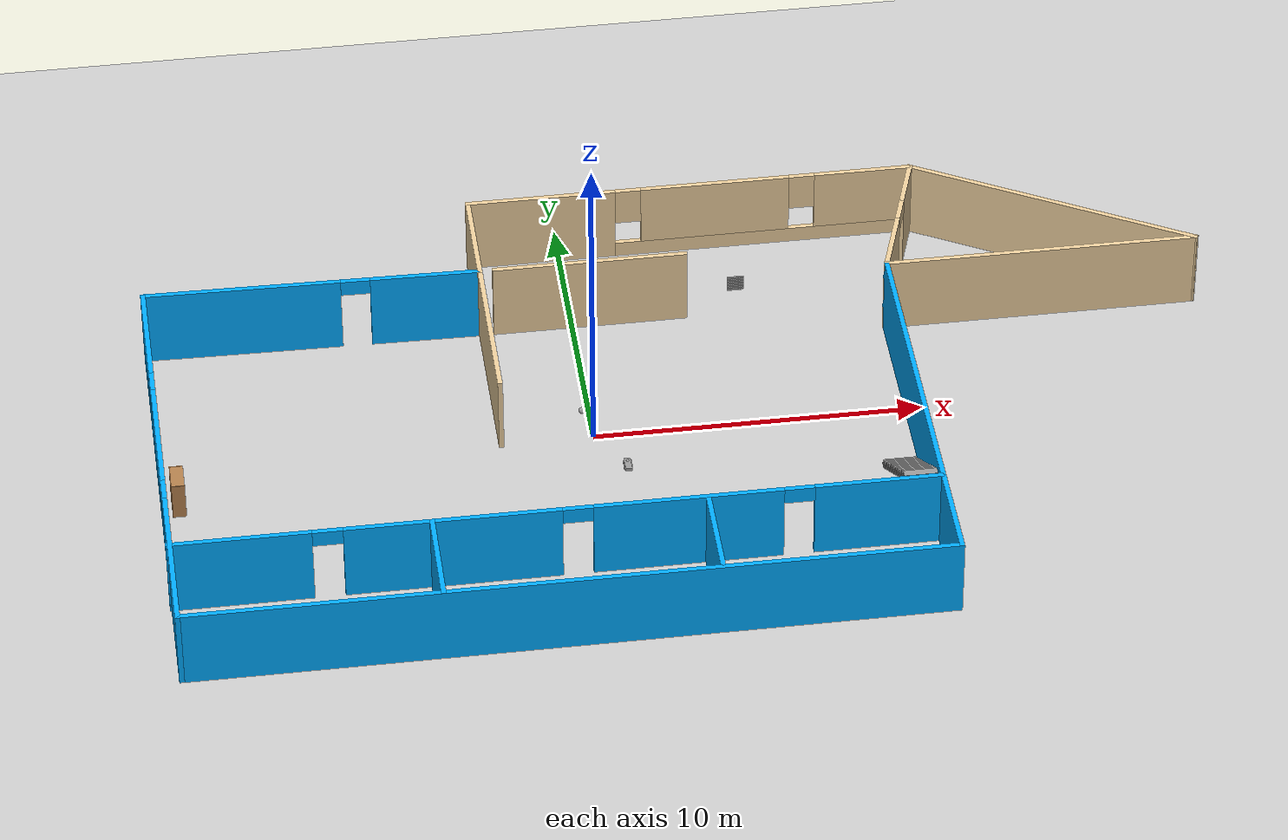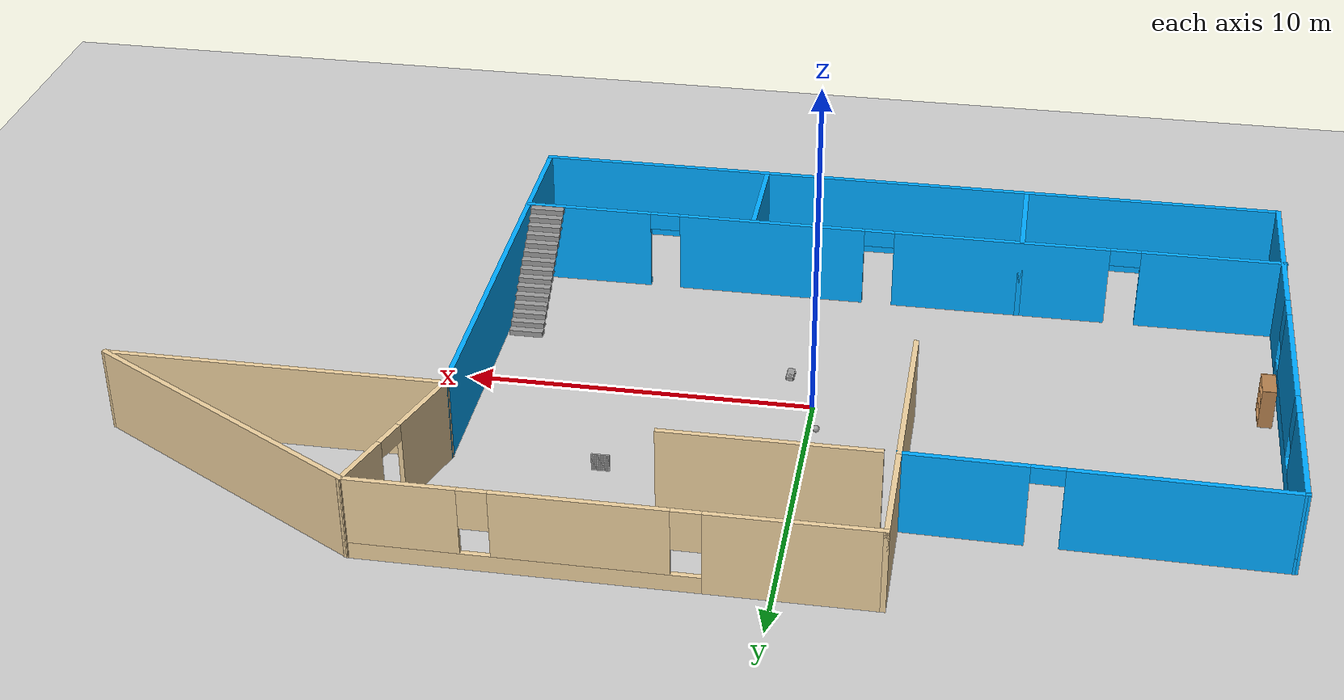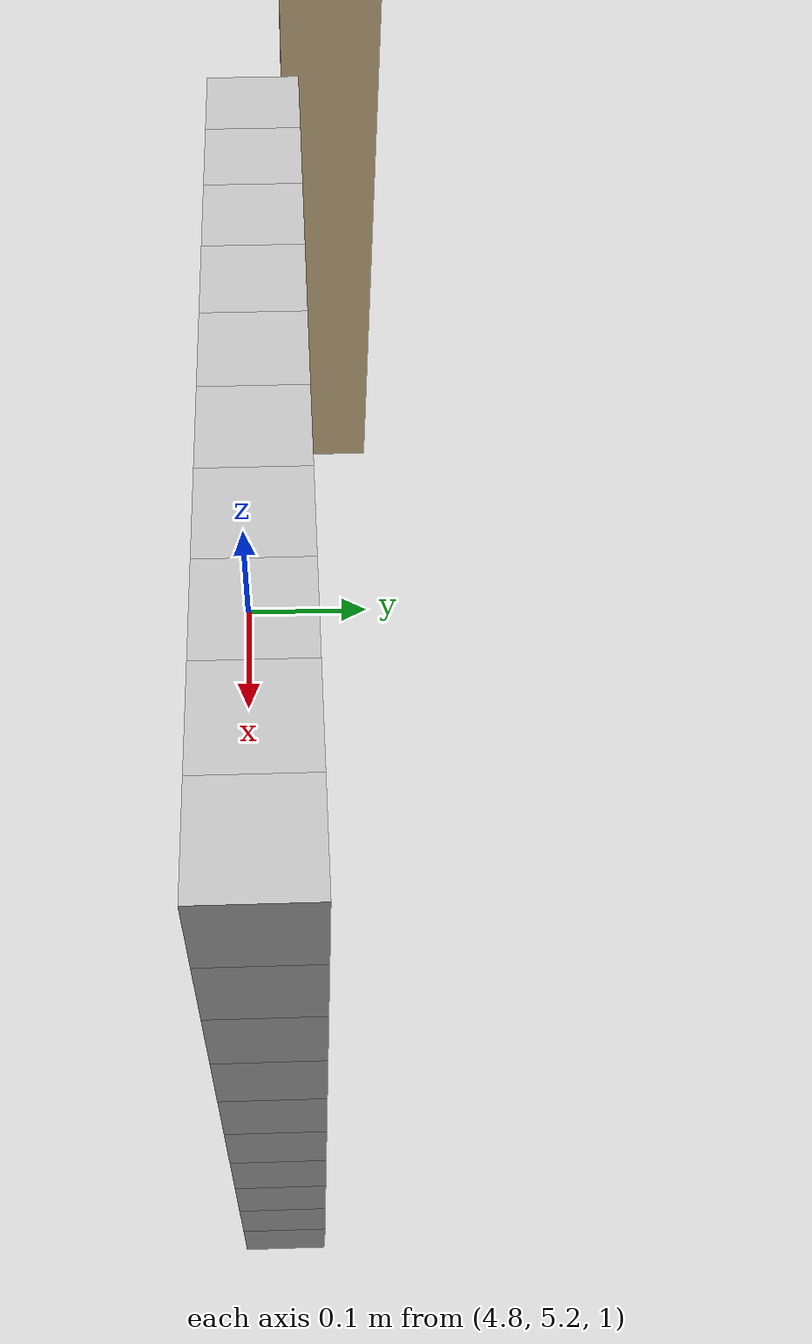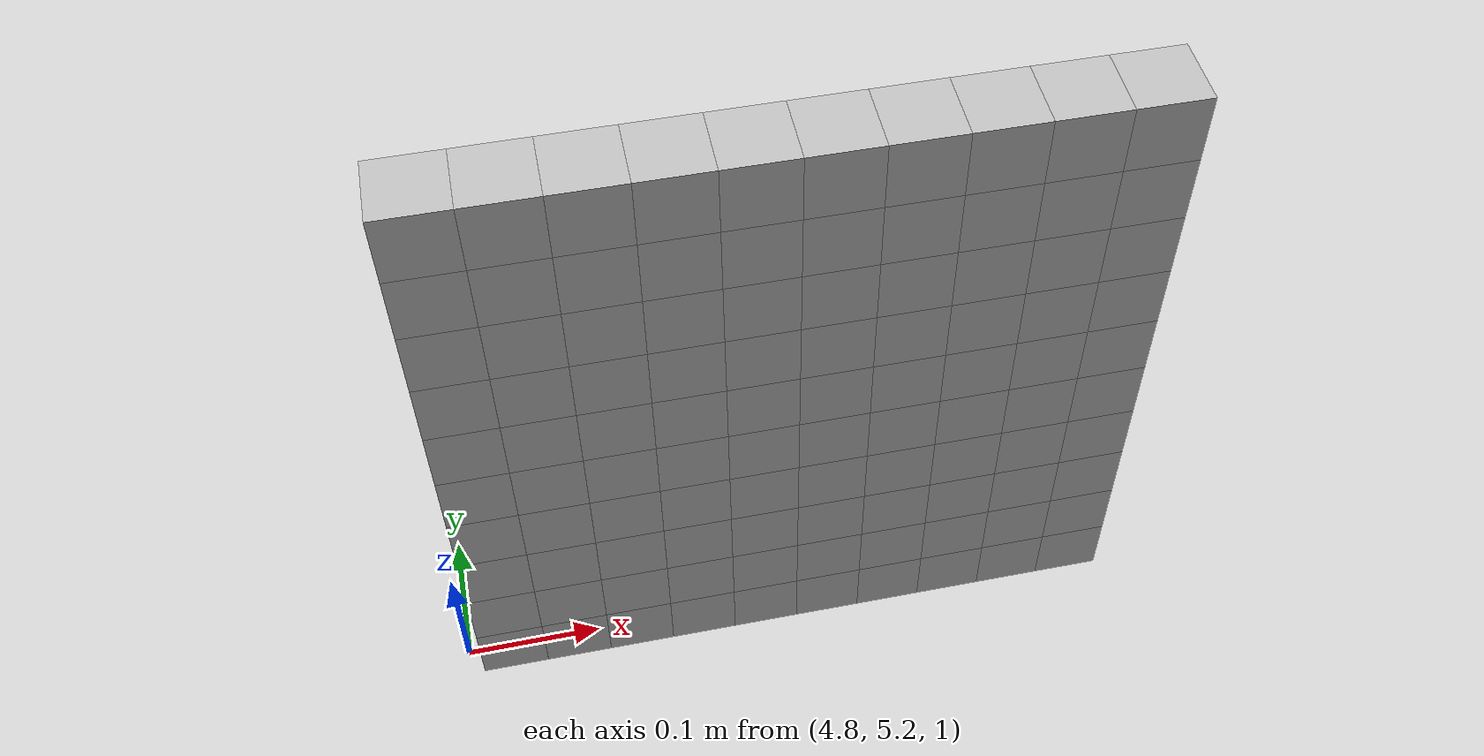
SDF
<sdf version="1.6">
 <world name="default">
  <plugin name="hello" filename="libhello.so"/>
  <light name="sun" type="directional">
   <pose>0 0 10 0 -0 0</pose>
   <diffuse>0.8 0.8 0.8 1</diffuse>
   <specular>0.2 0.2 0.2 1</specular>
   <attenuation>
    <range>1000</range>
    <constant>0.9</constant>
    <linear>0.01</linear>
    <quadratic>0.001</quadratic>
   </attenuation>
   <direction>-0.5 0.1 -0.9</direction>
  </light>
  <model name="ground_plane">
   <static>1</static>
   <link name="link">
    <collision name="collision">
     <geometry><plane><normal>0 0 1</normal><size>100 100</size></plane></geometry>
     <surface><friction><ode><mu>100</mu><mu2>50</mu2></ode></friction></surface>
    </collision>
    <visual name="visual">
     <cast_shadows>0</cast_shadows>
     <geometry><plane><normal>0 0 1</normal><size>100 100</size></plane></geometry>
     <material>
      <script><uri>file://media/materials/scripts/gazebo.material</uri><name>Gazebo/Grey</name></script>
     </material>
    </visual>
   </link>
  </model>
  <gravity>0 0 -9.8</gravity>
  <magnetic_field>6e-06 2.3e-05 -4.2e-05</magnetic_field>
  <atmosphere type="adiabatic"/>
  <physics name="default_physics" default="0" type="ode">
   <max_step_size>0.001</max_step_size>
   <real_time_factor>1</real_time_factor>
   <real_time_update_rate>1000</real_time_update_rate>
  </physics>
  <scene><ambient>0.4 0.4 0.4 1</ambient><background>0.7 0.7 0.7 1</background><shadows>1</shadows></scene>
  <spherical_coordinates>
   <surface_model>EARTH_WGS84</surface_model>
   <latitude_deg>0</latitude_deg>
   <longitude_deg>0</longitude_deg>
   <elevation>0</elevation>
   <heading_deg>0</heading_deg>
  </spherical_coordinates>
  <model name="building">
   <pose>3.02885 -0.210627 0 0 -0 0</pose>
   <link name="Stairs_0">
    <visual name="Stairs_0_Visual_0">
     <pose>5.86893 -2.32318 0.083333 0 -0 0</pose>
     <geometry><box><size>1 0.233333 0.166667</size></box></geometry>
     <material>
      <script><uri>file://media/materials/scripts/gazebo.material</uri><name>Gazebo/Grey</name></script>
      <ambient>1 1 1 1</ambient>
     </material>
     <meta><layer>0</layer></meta>
    </visual>
    <collision name="Stairs_0_Collision_0">
     <geometry><box><size>1 0.233333 0.166667</size></box></geometry>
     <pose>5.86893 -2.32318 0.083333 0 -0 0</pose>
    </collision>
    <visual name="Stairs_0_Visual_1">
     <pose>5.86893 -2.55652 0.25 0 -0 0</pose>
     <geometry><box><size>1 0.233333 0.166667</size></box></geometry>
     <material>
      <script><uri>file://media/materials/scripts/gazebo.material</uri><name>Gazebo/Grey</name></script>
      <ambient>1 1 1 1</ambient>
     </material>
     <meta><layer>0</layer></meta>
    </visual>
    <collision name="Stairs_0_Collision_1">
     <geometry><box><size>1 0.233333 0.166667</size></box></geometry>
     <pose>5.86893 -2.55652 0.25 0 -0 0</pose>
    </collision>
    <visual name="Stairs_0_Visual_2">
     <pose>5.86893 -2.78985 0.416667 0 -0 0</pose>
     <geometry><box><size>1 0.233333 0.166667</size></box></geometry>
     <material>
      <script><uri>file://media/materials/scripts/gazebo.material</uri><name>Gazebo/Grey</name></script>
      <ambient>1 1 1 1</ambient>
     </material>
     <meta><layer>0</layer></meta>
    </visual>
    <collision name="Stairs_0_Collision_2">
     <geometry><box><size>1 0.233333 0.166667</size></box></geometry>
     <pose>5.86893 -2.78985 0.416667 0 -0 0</pose>
    </collision>
    <visual name="Stairs_0_Visual_3">
     <pose>5.86893 -3.02318 0.583333 0 -0 0</pose>
     <geometry><box><size>1 0.233333 0.166667</size></box></geometry>
     <material>
      <script><uri>file://media/materials/scripts/gazebo.material</uri><name>Gazebo/Grey</name></script>
      <ambient>1 1 1 1</ambient>
     </material>
     <meta><layer>0</layer></meta>
    </visual>
    <collision name="Stairs_0_Collision_3">
     <geometry><box><size>1 0.233333 0.166667</size></box></geometry>
     <pose>5.86893 -3.02318 0.583333 0 -0 0</pose>
    </collision>
    <visual name="Stairs_0_Visual_4">
     <pose>5.86893 -3.25652 0.75 0 -0 0</pose>
     <geometry><box><size>1 0.233333 0.166667</size></box></geometry>
     <material>
      <script><uri>file://media/materials/scripts/gazebo.material</uri><name>Gazebo/Grey</name></script>
      <ambient>1 1 1 1</ambient>
     </material>
     <meta><layer>0</layer></meta>
    </visual>
    <collision name="Stairs_0_Collision_4">
     <geometry><box><size>1 0.233333 0.166667</size></box></geometry>
     <pose>5.86893 -3.25652 0.75 0 -0 0</pose>
    </collision>
    <visual name="Stairs_0_Visual_5">
     <pose>5.86893 -3.48985 0.916667 0 -0 0</pose>
     <geometry><box><size>1 0.233333 0.166667</size></box></geometry>
     <material>
      <script><uri>file://media/materials/scripts/gazebo.material</uri><name>Gazebo/Grey</name></script>
      <ambient>1 1 1 1</ambient>
     </material>
     <meta><layer>0</layer></meta>
    </visual>
    <collision name="Stairs_0_Collision_5">
     <geometry><box><size>1 0.233333 0.166667</size></box></geometry>
     <pose>5.86893 -3.48985 0.916667 0 -0 0</pose>
    </collision>
    <visual name="Stairs_0_Visual_6">
     <pose>5.86893 -3.72318 1.08333 0 -0 0</pose>
     <geometry><box><size>1 0.233333 0.166667</size></box></geometry>
     <material>
      <script><uri>file://media/materials/scripts/gazebo.material</uri><name>Gazebo/Grey</name></script>
      <ambient>1 1 1 1</ambient>
     </material>
     <meta><layer>0</layer></meta>
    </visual>
    <collision name="Stairs_0_Collision_6">
     <geometry><box><size>1 0.233333 0.166667</size></box></geometry>
     <pose>5.86893 -3.72318 1.08333 0 -0 0</pose>
    </collision>
    <visual name="Stairs_0_Visual_7">
     <pose>5.86893 -3.95652 1.25 0 -0 0</pose>
     <geometry><box><size>1 0.233333 0.166667</size></box></geometry>
     <material>
      <script><uri>file://media/materials/scripts/gazebo.material</uri><name>Gazebo/Grey</name></script>
      <ambient>1 1 1 1</ambient>
     </material>
     <meta><layer>0</layer></meta>
    </visual>
    <collision name="Stairs_0_Collision_7">
     <geometry><box><size>1 0.233333 0.166667</size></box></geometry>
     <pose>5.86893 -3.95652 1.25 0 -0 0</pose>
    </collision>
    <visual name="Stairs_0_Visual_8">
     <pose>5.86893 -4.18985 1.41667 0 -0 0</pose>
     <geometry><box><size>1 0.233333 0.166667</size></box></geometry>
     <material>
      <script><uri>file://media/materials/scripts/gazebo.material</uri><name>Gazebo/Grey</name></script>
      <ambient>1 1 1 1</ambient>
     </material>
     <meta><layer>0</layer></meta>
    </visual>
    <collision name="Stairs_0_Collision_8">
     <geometry><box><size>1 0.233333 0.166667</size></box></geometry>
     <pose>5.86893 -4.18985 1.41667 0 -0 0</pose>
    </collision>
    <visual name="Stairs_0_Visual_9">
     <pose>5.86893 -4.42318 1.58333 0 -0 0</pose>
     <geometry><box><size>1 0.233333 0.166667</size></box></geometry>
     <material>
      <script><uri>file://media/materials/scripts/gazebo.material</uri><name>Gazebo/Grey</name></script>
      <ambient>1 1 1 1</ambient>
     </material>
     <meta><layer>0</layer></meta>
    </visual>
    <collision name="Stairs_0_Collision_9">
     <geometry><box><size>1 0.233333 0.166667</size></box></geometry>
     <pose>5.86893 -4.42318 1.58333 0 -0 0</pose>
    </collision>
    <visual name="Stairs_0_Visual_10">
     <pose>5.86893 -4.65652 1.75 0 -0 0</pose>
     <geometry><box><size>1 0.233333 0.166667</size></box></geometry>
     <material>
      <script><uri>file://media/materials/scripts/gazebo.material</uri><name>Gazebo/Grey</name></script>
      <ambient>1 1 1 1</ambient>
     </material>
     <meta><layer>0</layer></meta>
    </visual>
    <collision name="Stairs_0_Collision_10">
     <geometry><box><size>1 0.233333 0.166667</size></box></geometry>
     <pose>5.86893 -4.65652 1.75 0 -0 0</pose>
    </collision>
    <visual name="Stairs_0_Visual_11">
     <pose>5.86893 -4.88985 1.91667 0 -0 0</pose>
     <geometry><box><size>1 0.233333 0.166667</size></box></geometry>
     <material>
      <script><uri>file://media/materials/scripts/gazebo.material</uri><name>Gazebo/Grey</name></script>
      <ambient>1 1 1 1</ambient>
     </material>
     <meta><layer>0</layer></meta>
    </visual>
    <collision name="Stairs_0_Collision_11">
     <geometry><box><size>1 0.233333 0.166667</size></box></geometry>
     <pose>5.86893 -4.88985 1.91667 0 -0 0</pose>
    </collision>
    <visual name="Stairs_0_Visual_12">
     <pose>5.86893 -5.12318 2.08333 0 -0 0</pose>
     <geometry><box><size>1 0.233333 0.166667</size></box></geometry>
     <material>
      <script><uri>file://media/materials/scripts/gazebo.material</uri><name>Gazebo/Grey</name></script>
      <ambient>1 1 1 1</ambient>
     </material>
     <meta><layer>0</layer></meta>
    </visual>
    <collision name="Stairs_0_Collision_12">
     <geometry><box><size>1 0.233333 0.166667</size></box></geometry>
     <pose>5.86893 -5.12318 2.08333 0 -0 0</pose>
    </collision>
    <visual name="Stairs_0_Visual_13">
     <pose>5.86893 -5.35652 2.25 0 -0 0</pose>
     <geometry><box><size>1 0.233333 0.166667</size></box></geometry>
     <material>
      <script><uri>file://media/materials/scripts/gazebo.material</uri><name>Gazebo/Grey</name></script>
      <ambient>1 1 1 1</ambient>
     </material>
     <meta><layer>0</layer></meta>
    </visual>
    <collision name="Stairs_0_Collision_13">
     <geometry><box><size>1 0.233333 0.166667</size></box></geometry>
     <pose>5.86893 -5.35652 2.25 0 -0 0</pose>
    </collision>
    <visual name="Stairs_0_Visual_14">
     <pose>5.86893 -5.58985 2.41667 0 -0 0</pose>
     <geometry><box><size>1 0.233333 0.166667</size></box></geometry>
     <material>
      <script><uri>file://media/materials/scripts/gazebo.material</uri><name>Gazebo/Grey</name></script>
      <ambient>1 1 1 1</ambient>
     </material>
     <meta><layer>0</layer></meta>
    </visual>
    <collision name="Stairs_0_Collision_14">
     <geometry><box><size>1 0.233333 0.166667</size></box></geometry>
     <pose>5.86893 -5.58985 2.41667 0 -0 0</pose>
    </collision>
   </link>
   <link name="Wall_0">
    <collision name="Wall_0_Collision">
     <geometry><box><size>3.5 0.15 2.5</size></box></geometry>
     <pose>0 0 1.25 0 -0 0</pose>
    </collision>
    <visual name="Wall_0_Visual">
     <pose>0 0 1.25 0 -0 0</pose>
     <geometry><box><size>3.5 0.15 2.5</size></box></geometry>
     <material>
      <script><uri>file://media/materials/scripts/gazebo.material</uri><name>Gazebo/Grey</name></script>
      <ambient>0.921569 0.807843 0.615686 1</ambient>
     </material>
     <meta><layer>0</layer></meta>
    </visual>
    <pose>-5.83827 7.19877 0 0 -0 1.5708</pose>
   </link>
   <link name="Wall_1">
    <pose>1.08673 8.87377 0 0 -0 0</pose>
    <visual name="Wall_1_Visual_0">
     <pose>-4.66986 0 1.25 0 -0 0</pose>
     <geometry><box><size>4.66028 0.15 2.5</size></box></geometry>
     <material>
      <script><uri>file://media/materials/scripts/gazebo.material</uri><name>Gazebo/Grey</name></script>
      <ambient>0.921569 0.807843 0.615686 1</ambient>
     </material>
     <meta><layer>0</layer></meta>
    </visual>
    <collision name="Wall_1_Collision_0">
     <geometry><box><size>4.66028 0.15 2.5</size></box></geometry>
     <pose>-4.66986 0 1.25 0 -0 0</pose>
    </collision>
    <visual name="Wall_1_Visual_1">
     <pose>2.33014 0 0.25 0 -0 0</pose>
     <geometry><box><size>9.33972 0.15 0.5</size></box></geometry>
     <material>
      <script><uri>file://media/materials/scripts/gazebo.material</uri><name>Gazebo/Grey</name></script>
      <ambient>0.921569 0.807843 0.615686 1</ambient>
     </material>
     <meta><layer>0</layer></meta>
    </visual>
    <collision name="Wall_1_Collision_1">
     <geometry><box><size>9.33972 0.15 0.5</size></box></geometry>
     <pose>2.33014 0 0.25 0 -0 0</pose>
    </collision>
    <visual name="Wall_1_Visual_2">
     <pose>0.784421 0 1.5 0 -0 0</pose>
     <geometry><box><size>4.64829 0.15 2</size></box></geometry>
     <material>
      <script><uri>file://media/materials/scripts/gazebo.material</uri><name>Gazebo/Grey</name></script>
      <ambient>0.921569 0.807843 0.615686 1</ambient>
     </material>
     <meta><layer>0</layer></meta>
    </visual>
    <collision name="Wall_1_Collision_2">
     <geometry><box><size>4.64829 0.15 2</size></box></geometry>
     <pose>0.784421 0 1.5 0 -0 0</pose>
    </collision>
    <visual name="Wall_1_Visual_3">
     <pose>5.45428 0 1.5 0 -0 0</pose>
     <geometry><box><size>3.09143 0.15 2</size></box></geometry>
     <material>
      <script><uri>file://media/materials/scripts/gazebo.material</uri><name>Gazebo/Grey</name></script>
      <ambient>0.921569 0.807843 0.615686 1</ambient>
     </material>
     <meta><layer>0</layer></meta>
    </visual>
    <collision name="Wall_1_Collision_3">
     <geometry><box><size>3.09143 0.15 2</size></box></geometry>
     <pose>5.45428 0 1.5 0 -0 0</pose>
    </collision>
    <visual name="Wall_1_Visual_4">
     <pose>-1.93972 0 1.9 0 -0 0</pose>
     <geometry><box><size>0.8 0.15 1.2</size></box></geometry>
     <material>
      <script><uri>file://media/materials/scripts/gazebo.material</uri><name>Gazebo/Grey</name></script>
      <ambient>0.921569 0.807843 0.615686 1</ambient>
     </material>
     <meta><layer>0</layer></meta>
    </visual>
    <collision name="Wall_1_Collision_4">
     <geometry><box><size>0.8 0.15 1.2</size></box></geometry>
     <pose>-1.93972 0 1.9 0 -0 0</pose>
    </collision>
    <visual name="Wall_1_Visual_5">
     <pose>3.50857 0 1.9 0 -0 0</pose>
     <geometry><box><size>0.8 0.15 1.2</size></box></geometry>
     <material>
      <script><uri>file://media/materials/scripts/gazebo.material</uri><name>Gazebo/Grey</name></script>
      <ambient>0.921569 0.807843 0.615686 1</ambient>
     </material>
     <meta><layer>0</layer></meta>
    </visual>
    <collision name="Wall_1_Collision_5">
     <geometry><box><size>0.8 0.15 1.2</size></box></geometry>
     <pose>3.50857 0 1.9 0 -0 0</pose>
    </collision>
   </link>
   <link name="Wall_11">
    <pose>-16.0909 -1.60123 0 0 -0 1.5708</pose>
    <visual name="Wall_11_Visual_0">
     <pose>-4.74674 0 1.25 0 -0 0</pose>
     <geometry><box><size>5.25652 0.15 2.5</size></box></geometry>
     <material>
      <script><uri>file://media/materials/scripts/gazebo.material</uri><name>Gazebo/Grey</name></script>
      <ambient>0 0.666667 1 1</ambient>
     </material>
     <meta><layer>0</layer></meta>
    </visual>
    <collision name="Wall_11_Collision_0">
     <geometry><box><size>5.25652 0.15 2.5</size></box></geometry>
     <pose>-4.74674 0 1.25 0 -0 0</pose>
    </collision>
    <visual name="Wall_11_Visual_1">
     <pose>2.62826 0 0.25 0 -0 0</pose>
     <geometry><box><size>9.49348 0.15 0.5</size></box></geometry>
     <material>
      <script><uri>file://media/materials/scripts/gazebo.material</uri><name>Gazebo/Grey</name></script>
      <ambient>0 0.666667 1 1</ambient>
     </material>
     <meta><layer>0</layer></meta>
    </visual>
    <collision name="Wall_11_Collision_1">
     <geometry><box><size>9.49348 0.15 0.5</size></box></geometry>
     <pose>2.62826 0 0.25 0 -0 0</pose>
    </collision>
    <visual name="Wall_11_Visual_2">
     <pose>0.75802 0 1.5 0 -0 0</pose>
     <geometry><box><size>4.15299 0.15 2</size></box></geometry>
     <material>
      <script><uri>file://media/materials/scripts/gazebo.material</uri><name>Gazebo/Grey</name></script>
      <ambient>0 0.666667 1 1</ambient>
     </material>
     <meta><layer>0</layer></meta>
    </visual>
    <collision name="Wall_11_Collision_2">
     <geometry><box><size>4.15299 0.15 2</size></box></geometry>
     <pose>0.75802 0 1.5 0 -0 0</pose>
    </collision>
    <visual name="Wall_11_Visual_3">
     <pose>5.50476 0 1.5 0 -0 0</pose>
     <geometry><box><size>3.74048 0.15 2</size></box></geometry>
     <material>
      <script><uri>file://media/materials/scripts/gazebo.material</uri><name>Gazebo/Grey</name></script>
      <ambient>0 0.666667 1 1</ambient>
     </material>
     <meta><layer>0</layer></meta>
    </visual>
    <collision name="Wall_11_Collision_3">
     <geometry><box><size>3.74048 0.15 2</size></box></geometry>
     <pose>5.50476 0 1.5 0 -0 0</pose>
    </collision>
    <visual name="Wall_11_Visual_4">
     <pose>-1.71848 0 1.9 0 -0 0</pose>
     <geometry><box><size>0.8 0.15 1.2</size></box></geometry>
     <material>
      <script><uri>file://media/materials/scripts/gazebo.material</uri><name>Gazebo/Grey</name></script>
      <ambient>0 0.666667 1 1</ambient>
     </material>
     <meta><layer>0</layer></meta>
    </visual>
    <collision name="Wall_11_Collision_4">
     <geometry><box><size>0.8 0.15 1.2</size></box></geometry>
     <pose>-1.71848 0 1.9 0 -0 0</pose>
    </collision>
    <visual name="Wall_11_Visual_5">
     <pose>3.23452 0 1.9 0 -0 0</pose>
     <geometry><box><size>0.8 0.15 1.2</size></box></geometry>
     <material>
      <script><uri>file://media/materials/scripts/gazebo.material</uri><name>Gazebo/Grey</name></script>
      <ambient>0 0.666667 1 1</ambient>
     </material>
     <meta><layer>0</layer></meta>
    </visual>
    <collision name="Wall_11_Collision_5">
     <geometry><box><size>0.8 0.15 1.2</size></box></geometry>
     <pose>3.23452 0 1.9 0 -0 0</pose>
    </collision>
   </link>
   <link name="Wall_12">
    <pose>-10.9646 5.61127 0 0 0 -0.017067</pose>
    <visual name="Wall_12_Visual_0">
     <pose>-2.16739 0 1.25 0 -0 0</pose>
     <geometry><box><size>6.06937 0.15 2.5</size></box></geometry>
     <material>
      <script><uri>file://media/materials/scripts/gazebo.material</uri><name>Gazebo/Grey</name></script>
      <ambient>0 0.666667 1 1</ambient>
     </material>
     <meta><layer>0</layer></meta>
    </visual>
    <collision name="Wall_12_Collision_0">
     <geometry><box><size>6.06937 0.15 2.5</size></box></geometry>
     <pose>-2.16739 0 1.25 0 -0 0</pose>
    </collision>
    <visual name="Wall_12_Visual_1">
     <pose>3.48468 0 1.25 0 -0 0</pose>
     <geometry><box><size>3.43479 0.15 2.5</size></box></geometry>
     <material>
      <script><uri>file://media/materials/scripts/gazebo.material</uri><name>Gazebo/Grey</name></script>
      <ambient>0 0.666667 1 1</ambient>
     </material>
     <meta><layer>0</layer></meta>
    </visual>
    <collision name="Wall_12_Collision_1">
     <geometry><box><size>3.43479 0.15 2.5</size></box></geometry>
     <pose>3.48468 0 1.25 0 -0 0</pose>
    </collision>
    <visual name="Wall_12_Visual_2">
     <pose>1.31729 0 2.25 0 -0 0</pose>
     <geometry><box><size>0.9 0.15 0.5</size></box></geometry>
     <material>
      <script><uri>file://media/materials/scripts/gazebo.material</uri><name>Gazebo/Grey</name></script>
      <ambient>0 0.666667 1 1</ambient>
     </material>
     <meta><layer>0</layer></meta>
    </visual>
    <collision name="Wall_12_Collision_2">
     <geometry><box><size>0.9 0.15 0.5</size></box></geometry>
     <pose>1.31729 0 2.25 0 -0 0</pose>
    </collision>
   </link>
   <link name="Wall_18">
    <pose>-4.83652 -5.7962 0 0 -0 0</pose>
    <visual name="Wall_18_Visual_0">
     <pose>-9.2629 0 1.25 0 -0 0</pose>
     <geometry><box><size>4.22421 0.15 2.5</size></box></geometry>
     <material>
      <script><uri>file://media/materials/scripts/gazebo.material</uri><name>Gazebo/Grey</name></script>
      <ambient>0 0.666667 1 1</ambient>
     </material>
     <meta><layer>0</layer></meta>
    </visual>
    <collision name="Wall_18_Collision_0">
     <geometry><box><size>4.22421 0.15 2.5</size></box></geometry>
     <pose>-9.2629 0 1.25 0 -0 0</pose>
    </collision>
    <visual name="Wall_18_Visual_1">
     <pose>-3.0568 0 1.25 0 -0 0</pose>
     <geometry><box><size>6.38798 0.15 2.5</size></box></geometry>
     <material>
      <script><uri>file://media/materials/scripts/gazebo.material</uri><name>Gazebo/Grey</name></script>
      <ambient>0 0.666667 1 1</ambient>
     </material>
     <meta><layer>0</layer></meta>
    </visual>
    <collision name="Wall_18_Collision_1">
     <geometry><box><size>6.38798 0.15 2.5</size></box></geometry>
     <pose>-3.0568 0 1.25 0 -0 0</pose>
    </collision>
    <visual name="Wall_18_Visual_2">
     <pose>3.84201 0 1.25 0 -0 0</pose>
     <geometry><box><size>5.60965 0.15 2.5</size></box></geometry>
     <material>
      <script><uri>file://media/materials/scripts/gazebo.material</uri><name>Gazebo/Grey</name></script>
      <ambient>0 0.666667 1 1</ambient>
     </material>
     <meta><layer>0</layer></meta>
    </visual>
    <collision name="Wall_18_Collision_2">
     <geometry><box><size>5.60965 0.15 2.5</size></box></geometry>
     <pose>3.84201 0 1.25 0 -0 0</pose>
    </collision>
    <visual name="Wall_18_Visual_3">
     <pose>9.46092 0 1.25 0 -0 0</pose>
     <geometry><box><size>3.82816 0.15 2.5</size></box></geometry>
     <material>
      <script><uri>file://media/materials/scripts/gazebo.material</uri><name>Gazebo/Grey</name></script>
      <ambient>0 0.666667 1 1</ambient>
     </material>
     <meta><layer>0</layer></meta>
    </visual>
    <collision name="Wall_18_Collision_3">
     <geometry><box><size>3.82816 0.15 2.5</size></box></geometry>
     <pose>9.46092 0 1.25 0 -0 0</pose>
    </collision>
    <visual name="Wall_18_Visual_4">
     <pose>-6.70079 0 2.25 0 -0 0</pose>
     <geometry><box><size>0.9 0.15 0.5</size></box></geometry>
     <material>
      <script><uri>file://media/materials/scripts/gazebo.material</uri><name>Gazebo/Grey</name></script>
      <ambient>0 0.666667 1 1</ambient>
     </material>
     <meta><layer>0</layer></meta>
    </visual>
    <collision name="Wall_18_Collision_4">
     <geometry><box><size>0.9 0.15 0.5</size></box></geometry>
     <pose>-6.70079 0 2.25 0 -0 0</pose>
    </collision>
    <visual name="Wall_18_Visual_5">
     <pose>0.587186 0 2.25 0 -0 0</pose>
     <geometry><box><size>0.9 0.15 0.5</size></box></geometry>
     <material>
      <script><uri>file://media/materials/scripts/gazebo.material</uri><name>Gazebo/Grey</name></script>
      <ambient>0 0.666667 1 1</ambient>
     </material>
     <meta><layer>0</layer></meta>
    </visual>
    <collision name="Wall_18_Collision_5">
     <geometry><box><size>0.9 0.15 0.5</size></box></geometry>
     <pose>0.587186 0 2.25 0 -0 0</pose>
    </collision>
    <visual name="Wall_18_Visual_6">
     <pose>7.09683 0 2.25 0 -0 0</pose>
     <geometry><box><size>0.9 0.15 0.5</size></box></geometry>
     <material>
      <script><uri>file://media/materials/scripts/gazebo.material</uri><name>Gazebo/Grey</name></script>
      <ambient>0 0.666667 1 1</ambient>
     </material>
     <meta><layer>0</layer></meta>
    </visual>
    <collision name="Wall_18_Collision_6">
     <geometry><box><size>0.9 0.15 0.5</size></box></geometry>
     <pose>7.09683 0 2.25 0 -0 0</pose>
    </collision>
   </link>
   <link name="Wall_20">
    <collision name="Wall_20_Collision">
     <geometry><box><size>3.25 0.15 2.5</size></box></geometry>
     <pose>0 0 1.25 0 -0 0</pose>
    </collision>
    <visual name="Wall_20_Visual">
     <pose>0 0 1.25 0 -0 0</pose>
     <geometry><box><size>3.25 0.15 2.5</size></box></geometry>
     <material>
      <script><uri>file://media/materials/scripts/gazebo.material</uri><name>Gazebo/Grey</name></script>
      <ambient>0 0.666667 1 1</ambient>
     </material>
     <meta><layer>0</layer></meta>
    </visual>
    <pose>-8.49476 -7.3462 0 0 0 -1.5708</pose>
   </link>
   <link name="Wall_22">
    <collision name="Wall_22_Collision">
     <geometry><box><size>3 0.15 2.5</size></box></geometry>
     <pose>0 0 1.25 0 -0 0</pose>
    </collision>
    <visual name="Wall_22_Visual">
     <pose>0 0 1.25 0 -0 0</pose>
     <geometry><box><size>3 0.15 2.5</size></box></geometry>
     <material>
      <script><uri>file://media/materials/scripts/gazebo.material</uri><name>Gazebo/Grey</name></script>
      <ambient>0 0.666667 1 1</ambient>
     </material>
     <meta><layer>0</layer></meta>
    </visual>
    <pose>-0.428452 -7.36271 0 0 0 -1.5708</pose>
   </link>
   <link name="Wall_24">
    <pose>7.2604 6.53627 0 0 0 -1.88179</pose>
    <visual name="Wall_24_Visual_0">
     <pose>-1.61861 0 1.25 0 -0 0</pose>
     <geometry><box><size>1.82334 0.15 2.5</size></box></geometry>
     <material>
      <script><uri>file://media/materials/scripts/gazebo.material</uri><name>Gazebo/Grey</name></script>
      <ambient>0.921569 0.807843 0.615686 1</ambient>
     </material>
     <meta><layer>0</layer></meta>
    </visual>
    <collision name="Wall_24_Collision_0">
     <geometry><box><size>1.82334 0.15 2.5</size></box></geometry>
     <pose>-1.61861 0 1.25 0 -0 0</pose>
    </collision>
    <visual name="Wall_24_Visual_1">
     <pose>1.36167 0 1.25 0 -0 0</pose>
     <geometry><box><size>2.33722 0.15 2.5</size></box></geometry>
     <material>
      <script><uri>file://media/materials/scripts/gazebo.material</uri><name>Gazebo/Grey</name></script>
      <ambient>0.921569 0.807843 0.615686 1</ambient>
     </material>
     <meta><layer>0</layer></meta>
    </visual>
    <collision name="Wall_24_Collision_1">
     <geometry><box><size>2.33722 0.15 2.5</size></box></geometry>
     <pose>1.36167 0 1.25 0 -0 0</pose>
    </collision>
    <visual name="Wall_24_Visual_2">
     <pose>-0.256943 0 2.25 0 -0 0</pose>
     <geometry><box><size>0.9 0.15 0.5</size></box></geometry>
     <material>
      <script><uri>file://media/materials/scripts/gazebo.material</uri><name>Gazebo/Grey</name></script>
      <ambient>0.921569 0.807843 0.615686 1</ambient>
     </material>
     <meta><layer>0</layer></meta>
    </visual>
    <collision name="Wall_24_Collision_2">
     <geometry><box><size>0.9 0.15 0.5</size></box></geometry>
     <pose>-0.256943 0 2.25 0 -0 0</pose>
    </collision>
   </link>
   <link name="Wall_26">
    <collision name="Wall_26_Collision">
     <geometry><box><size>5.5 0.15 2.5</size></box></geometry>
     <pose>0 0 1.25 0 -0 0</pose>
    </collision>
    <visual name="Wall_26_Visual">
     <pose>0 0 1.25 0 -0 0</pose>
     <geometry><box><size>5.5 0.15 2.5</size></box></geometry>
     <material>
      <script><uri>file://media/materials/scripts/gazebo.material</uri><name>Gazebo/Grey</name></script>
      <ambient>0.921569 0.807843 0.615686 1</ambient>
     </material>
     <meta><layer>0</layer></meta>
    </visual>
    <pose>-5.83827 2.84877 0 0 0 -1.5708</pose>
   </link>
   <link name="Wall_28">
    <collision name="Wall_28_Collision">
     <geometry><box><size>6 0.15 2.5</size></box></geometry>
     <pose>0 0 1.25 0 -0 0</pose>
    </collision>
    <visual name="Wall_28_Visual">
     <pose>0 0 1.25 0 -0 0</pose>
     <geometry><box><size>6 0.15 2.5</size></box></geometry>
     <material>
      <script><uri>file://media/materials/scripts/gazebo.material</uri><name>Gazebo/Grey</name></script>
      <ambient>0.921569 0.807843 0.615686 1</ambient>
     </material>
     <meta><layer>0</layer></meta>
    </visual>
    <pose>-2.45645 5.52493 0 0 -0 0</pose>
   </link>
   <link name="Wall_5">
    <collision name="Wall_5_Collision">
     <geometry><box><size>9.5 0.15 2.5</size></box></geometry>
     <pose>0 0 1.25 0 -0 0</pose>
    </collision>
    <visual name="Wall_5_Visual">
     <pose>0 0 1.25 0 -0 0</pose>
     <geometry><box><size>9.5 0.15 2.5</size></box></geometry>
     <material>
      <script><uri>file://media/materials/scripts/gazebo.material</uri><name>Gazebo/Grey</name></script>
      <ambient>0.921569 0.807843 0.615686 1</ambient>
     </material>
     <meta><layer>0</layer></meta>
    </visual>
    <pose>12.0604 6.53627 0 0 0 -0.523599</pose>
   </link>
   <link name="Wall_6">
    <collision name="Wall_6_Collision">
     <geometry><box><size>9.75 0.15 2.5</size></box></geometry>
     <pose>0 0 1.25 0 -0 0</pose>
    </collision>
    <visual name="Wall_6_Visual">
     <pose>0 0 1.25 0 -0 0</pose>
     <geometry><box><size>9.75 0.15 2.5</size></box></geometry>
     <material>
      <script><uri>file://media/materials/scripts/gazebo.material</uri><name>Gazebo/Grey</name></script>
      <ambient>0.921569 0.807843 0.615686 1</ambient>
     </material>
     <meta><layer>0</layer></meta>
    </visual>
    <pose>11.3091 4.19877 0 0 -0 3.14159</pose>
   </link>
   <link name="Wall_7">
    <collision name="Wall_7_Collision">
     <geometry><box><size>13.25 0.15 2.5</size></box></geometry>
     <pose>0 0 1.25 0 -0 0</pose>
    </collision>
    <visual name="Wall_7_Visual">
     <pose>0 0 1.25 0 -0 0</pose>
     <geometry><box><size>13.25 0.15 2.5</size></box></geometry>
     <material>
      <script><uri>file://media/materials/scripts/gazebo.material</uri><name>Gazebo/Grey</name></script>
      <ambient>0 0.666667 1 1</ambient>
     </material>
     <meta><layer>0</layer></meta>
    </visual>
    <pose>6.50907 -2.35123 0 0 0 -1.5708</pose>
   </link>
   <link name="Wall_8">
    <collision name="Wall_8_Collision">
     <geometry><box><size>22.75 0.15 2.5</size></box></geometry>
     <pose>0 0 1.25 0 -0 0</pose>
    </collision>
    <visual name="Wall_8_Visual">
     <pose>0 0 1.25 0 -0 0</pose>
     <geometry><box><size>22.75 0.15 2.5</size></box></geometry>
     <material>
      <script><uri>file://media/materials/scripts/gazebo.material</uri><name>Gazebo/Grey</name></script>
      <ambient>0 0.666667 1 1</ambient>
     </material>
     <meta><layer>0</layer></meta>
    </visual>
    <pose>-4.79093 -8.90123 0 0 -0 3.14159</pose>
   </link>
   <static>1</static>
  </model>
  <model name="bookshelf">
   <static>1</static>
   <link name="link">
    <inertial><mass>1</mass></inertial>
    <collision name="back">
     <pose>0 0.005 0.6 0 -0 0</pose>
     <geometry><box><size>0.9 0.01 1.2</size></box></geometry>
    </collision>
    <visual name="visual1">
     <pose>0 0.005 0.6 0 -0 0</pose>
     <geometry><box><size>0.9 0.01 1.2</size></box></geometry>
     <material>
      <script><uri>file://media/materials/scripts/gazebo.material</uri><name>Gazebo/Wood</name></script>
     </material>
    </visual>
    <collision name="left_side">
     <pose>0.45 -0.195 0.6 0 -0 0</pose>
     <geometry><box><size>0.02 0.4 1.2</size></box></geometry>
    </collision>
    <visual name="visual2">
     <pose>0.45 -0.195 0.6 0 -0 0</pose>
     <geometry><box><size>0.02 0.4 1.2</size></box></geometry>
     <material>
      <script><uri>file://media/materials/scripts/gazebo.material</uri><name>Gazebo/Wood</name></script>
     </material>
    </visual>
    <collision name="right_side">
     <pose>-0.45 -0.195 0.6 0 -0 0</pose>
     <geometry><box><size>0.02 0.4 1.2</size></box></geometry>
    </collision>
    <visual name="visual3">
     <pose>-0.45 -0.195 0.6 0 -0 0</pose>
     <geometry><box><size>0.02 0.4 1.2</size></box></geometry>
     <material>
      <script><uri>file://media/materials/scripts/gazebo.material</uri><name>Gazebo/Wood</name></script>
     </material>
    </visual>
    <collision name="bottom">
     <pose>0 -0.195 0.03 0 -0 0</pose>
     <geometry><box><size>0.88 0.4 0.06</size></box></geometry>
    </collision>
    <visual name="visual4">
     <pose>0 -0.195 0.03 0 -0 0</pose>
     <geometry><box><size>0.88 0.4 0.06</size></box></geometry>
     <material>
      <script><uri>file://media/materials/scripts/gazebo.material</uri><name>Gazebo/Wood</name></script>
     </material>
    </visual>
    <collision name="top">
     <pose>0 -0.195 1.19 0 -0 0</pose>
     <geometry><box><size>0.88 0.4 0.02</size></box></geometry>
    </collision>
    <visual name="visual5">
     <pose>0 -0.195 1.19 0 -0 0</pose>
     <geometry><box><size>0.88 0.4 0.02</size></box></geometry>
     <material>
      <script><uri>file://media/materials/scripts/gazebo.material</uri><name>Gazebo/Wood</name></script>
     </material>
    </visual>
    <collision name="low_shelf">
     <pose>0 -0.195 0.43 0 -0 0</pose>
     <geometry><box><size>0.88 0.4 0.02</size></box></geometry>
    </collision>
    <visual name="visual6">
     <pose>0 -0.195 0.43 0 -0 0</pose>
     <geometry><box><size>0.88 0.4 0.02</size></box></geometry>
     <material>
      <script><uri>file://media/materials/scripts/gazebo.material</uri><name>Gazebo/Wood</name></script>
     </material>
    </visual>
    <collision name="high_shelf">
     <pose>0 -0.195 0.8 0 -0 0</pose>
     <geometry><box><size>0.88 0.4 0.02</size></box></geometry>
    </collision>
    <visual name="visual7">
     <pose>0 -0.195 0.8 0 -0 0</pose>
     <geometry><box><size>0.88 0.4 0.02</size></box></geometry>
     <material>
      <script><uri>file://media/materials/scripts/gazebo.material</uri><name>Gazebo/Wood</name></script>
     </material>
    </visual>
   </link>
   <pose>-12.7949 -1.49856 0 0 -0 1.56823</pose>
  </model>
  <model name="breakable_test">
   <pose>4.8322 5.22307 0.996693 0 -0 0</pose>
   <link name="link_0_0">
    <inertial>
     <mass>0.3375</mass>
     <inertia>
      <ixx>0.000140625</ixx>
      <iyy>0.000140625</iyy>
      <izz>0.000140625</izz>
      <ixy>0</ixy>
      <ixz>0</ixz>
      <iyz>0</iyz>
     </inertia>
    </inertial>
    <collision name="collision"><geometry><box><size>0.05 0.05 0.05</size></box></geometry></collision>
    <visual name="visual"><geometry><box><size>0.05 0.05 0.05</size></box></geometry></visual>
   </link>
   <joint name="joint_0_0" type="revolute">
    <parent>world</parent>
    <child>link_0_0</child>
    <axis>
     <xyz>0 0 1</xyz>
     <limit><lower>0</lower><upper>0</upper></limit>
     <use_parent_model_frame>1</use_parent_model_frame>
     <dynamics><spring_reference>0</spring_reference><spring_stiffness>0</spring_stiffness></dynamics>
    </axis>
    <physics><ode><erp>1</erp><cfm>1</cfm><limit><cfm>0</cfm><erp>0.2</erp></limit></ode></physics>
    <sensor name="force_torque" type="force_torque">
     <always_on>1</always_on>
     <update_rate>1000</update_rate>
     <plugin name="breakable_0_0" filename="libBreakableJointPlugin.so">
      <breaking_force_N>50</breaking_force_N>
     </plugin>
    </sensor>
   </joint>
   <link name="link_0_1">
    <pose>0 0 0.05 0 -0 0</pose>
    <inertial>
     <mass>0.3375</mass>
     <inertia>
      <ixx>0.000140625</ixx>
      <iyy>0.000140625</iyy>
      <izz>0.000140625</izz>
      <ixy>0</ixy>
      <ixz>0</ixz>
      <iyz>0</iyz>
     </inertia>
    </inertial>
    <collision name="collision"><geometry><box><size>0.05 0.05 0.05</size></box></geometry></collision>
    <visual name="visual"><geometry><box><size>0.05 0.05 0.05</size></box></geometry></visual>
   </link>
   <joint name="joint_0_1" type="revolute">
    <parent>world</parent>
    <child>link_0_1</child>
    <axis>
     <xyz>0 0 1</xyz>
     <limit><lower>0</lower><upper>0</upper></limit>
     <use_parent_model_frame>1</use_parent_model_frame>
     <dynamics><spring_reference>0</spring_reference><spring_stiffness>0</spring_stiffness></dynamics>
    </axis>
    <physics><ode><erp>1</erp><cfm>1</cfm><limit><cfm>0</cfm><erp>0.2</erp></limit></ode></physics>
    <sensor name="force_torque" type="force_torque">
     <always_on>1</always_on>
     <update_rate>1000</update_rate>
     <plugin name="breakable_0_1" filename="libBreakableJointPlugin.so">
      <breaking_force_N>50</breaking_force_N>
     </plugin>
    </sensor>
   </joint>
   <link name="link_0_2">
    <pose>0 0 0.1 0 -0 0</pose>
    <inertial>
     <mass>0.3375</mass>
     <inertia>
      <ixx>0.000140625</ixx>
      <iyy>0.000140625</iyy>
      <izz>0.000140625</izz>
      <ixy>0</ixy>
      <ixz>0</ixz>
      <iyz>0</iyz>
     </inertia>
    </inertial>
    <collision name="collision"><geometry><box><size>0.05 0.05 0.05</size></box></geometry></collision>
    <visual name="visual"><geometry><box><size>0.05 0.05 0.05</size></box></geometry></visual>
   </link>
   <joint name="joint_0_2" type="revolute">
    <parent>world</parent>
    <child>link_0_2</child>
    <axis>
     <xyz>0 0 1</xyz>
     <limit><lower>0</lower><upper>0</upper></limit>
     <use_parent_model_frame>1</use_parent_model_frame>
     <dynamics><spring_reference>0</spring_reference><spring_stiffness>0</spring_stiffness></dynamics>
    </axis>
    <physics><ode><erp>1</erp><cfm>1</cfm><limit><cfm>0</cfm><erp>0.2</erp></limit></ode></physics>
    <sensor name="force_torque" type="force_torque">
     <always_on>1</always_on>
     <update_rate>1000</update_rate>
     <plugin name="breakable_0_2" filename="libBreakableJointPlugin.so">
      <breaking_force_N>50</breaking_force_N>
     </plugin>
    </sensor>
   </joint>
   <link name="link_0_3">
    <pose>0 0 0.15 0 -0 0</pose>
    <inertial>
     <mass>0.3375</mass>
     <inertia>
      <ixx>0.000140625</ixx>
      <iyy>0.000140625</iyy>
      <izz>0.000140625</izz>
      <ixy>0</ixy>
      <ixz>0</ixz>
      <iyz>0</iyz>
     </inertia>
    </inertial>
    <collision name="collision"><geometry><box><size>0.05 0.05 0.05</size></box></geometry></collision>
    <visual name="visual"><geometry><box><size>0.05 0.05 0.05</size></box></geometry></visual>
   </link>
   <joint name="joint_0_3" type="revolute">
    <parent>world</parent>
    <child>link_0_3</child>
    <axis>
     <xyz>0 0 1</xyz>
     <limit><lower>0</lower><upper>0</upper></limit>
     <use_parent_model_frame>1</use_parent_model_frame>
     <dynamics><spring_reference>0</spring_reference><spring_stiffness>0</spring_stiffness></dynamics>
    </axis>
    <physics><ode><erp>1</erp><cfm>1</cfm><limit><cfm>0</cfm><erp>0.2</erp></limit></ode></physics>
    <sensor name="force_torque" type="force_torque">
     <always_on>1</always_on>
     <update_rate>1000</update_rate>
     <plugin name="breakable_0_3" filename="libBreakableJointPlugin.so">
      <breaking_force_N>50</breaking_force_N>
     </plugin>
    </sensor>
   </joint>
   <link name="link_0_4">
    <pose>0 0 0.2 0 -0 0</pose>
    <inertial>
     <mass>0.3375</mass>
     <inertia>
      <ixx>0.000140625</ixx>
      <iyy>0.000140625</iyy>
      <izz>0.000140625</izz>
      <ixy>0</ixy>
      <ixz>0</ixz>
      <iyz>0</iyz>
     </inertia>
    </inertial>
    <collision name="collision"><geometry><box><size>0.05 0.05 0.05</size></box></geometry></collision>
    <visual name="visual"><geometry><box><size>0.05 0.05 0.05</size></box></geometry></visual>
   </link>
   <joint name="joint_0_4" type="revolute">
    <parent>world</parent>
    <child>link_0_4</child>
    <axis>
     <xyz>0 0 1</xyz>
     <limit><lower>0</lower><upper>0</upper></limit>
     <use_parent_model_frame>1</use_parent_model_frame>
     <dynamics><spring_reference>0</spring_reference><spring_stiffness>0</spring_stiffness></dynamics>
    </axis>
    <physics><ode><erp>1</erp><cfm>1</cfm><limit><cfm>0</cfm><erp>0.2</erp></limit></ode></physics>
    <sensor name="force_torque" type="force_torque">
     <always_on>1</always_on>
     <update_rate>1000</update_rate>
     <plugin name="breakable_0_4" filename="libBreakableJointPlugin.so">
      <breaking_force_N>50</breaking_force_N>
     </plugin>
    </sensor>
   </joint>
   <link name="link_0_5">
    <pose>0 0 0.25 0 -0 0</pose>
    <inertial>
     <mass>0.3375</mass>
     <inertia>
      <ixx>0.000140625</ixx>
      <iyy>0.000140625</iyy>
      <izz>0.000140625</izz>
      <ixy>0</ixy>
      <ixz>0</ixz>
      <iyz>0</iyz>
     </inertia>
    </inertial>
    <collision name="collision"><geometry><box><size>0.05 0.05 0.05</size></box></geometry></collision>
    <visual name="visual"><geometry><box><size>0.05 0.05 0.05</size></box></geometry></visual>
   </link>
   <joint name="joint_0_5" type="revolute">
    <parent>world</parent>
    <child>link_0_5</child>
    <axis>
     <xyz>0 0 1</xyz>
     <limit><lower>0</lower><upper>0</upper></limit>
     <use_parent_model_frame>1</use_parent_model_frame>
     <dynamics><spring_reference>0</spring_reference><spring_stiffness>0</spring_stiffness></dynamics>
    </axis>
    <physics><ode><erp>1</erp><cfm>1</cfm><limit><cfm>0</cfm><erp>0.2</erp></limit></ode></physics>
    <sensor name="force_torque" type="force_torque">
     <always_on>1</always_on>
     <update_rate>1000</update_rate>
     <plugin name="breakable_0_5" filename="libBreakableJointPlugin.so">
      <breaking_force_N>50</breaking_force_N>
     </plugin>
    </sensor>
   </joint>
   <link name="link_0_6">
    <pose>0 0 0.3 0 -0 0</pose>
    <inertial>
     <mass>0.3375</mass>
     <inertia>
      <ixx>0.000140625</ixx>
      <iyy>0.000140625</iyy>
      <izz>0.000140625</izz>
      <ixy>0</ixy>
      <ixz>0</ixz>
      <iyz>0</iyz>
     </inertia>
    </inertial>
    <collision name="collision"><geometry><box><size>0.05 0.05 0.05</size></box></geometry></collision>
    <visual name="visual"><geometry><box><size>0.05 0.05 0.05</size></box></geometry></visual>
   </link>
   <joint name="joint_0_6" type="revolute">
    <parent>world</parent>
    <child>link_0_6</child>
    <axis>
     <xyz>0 0 1</xyz>
     <limit><lower>0</lower><upper>0</upper></limit>
     <use_parent_model_frame>1</use_parent_model_frame>
     <dynamics><spring_reference>0</spring_reference><spring_stiffness>0</spring_stiffness></dynamics>
    </axis>
    <physics><ode><erp>1</erp><cfm>1</cfm><limit><cfm>0</cfm><erp>0.2</erp></limit></ode></physics>
    <sensor name="force_torque" type="force_torque">
     <always_on>1</always_on>
     <update_rate>1000</update_rate>
     <plugin name="breakable_0_6" filename="libBreakableJointPlugin.so">
      <breaking_force_N>50</breaking_force_N>
     </plugin>
    </sensor>
   </joint>
   <link name="link_0_7">
    <pose>0 0 0.35 0 -0 0</pose>
    <inertial>
     <mass>0.3375</mass>
     <inertia>
      <ixx>0.000140625</ixx>
      <iyy>0.000140625</iyy>
      <izz>0.000140625</izz>
      <ixy>0</ixy>
      <ixz>0</ixz>
      <iyz>0</iyz>
     </inertia>
    </inertial>
    <collision name="collision"><geometry><box><size>0.05 0.05 0.05</size></box></geometry></collision>
    <visual name="visual"><geometry><box><size>0.05 0.05 0.05</size></box></geometry></visual>
   </link>
   <joint name="joint_0_7" type="revolute">
    <parent>world</parent>
    <child>link_0_7</child>
    <axis>
     <xyz>0 0 1</xyz>
     <limit><lower>0</lower><upper>0</upper></limit>
     <use_parent_model_frame>1</use_parent_model_frame>
     <dynamics><spring_reference>0</spring_reference><spring_stiffness>0</spring_stiffness></dynamics>
    </axis>
    <physics><ode><erp>1</erp><cfm>1</cfm><limit><cfm>0</cfm><erp>0.2</erp></limit></ode></physics>
    <sensor name="force_torque" type="force_torque">
     <always_on>1</always_on>
     <update_rate>1000</update_rate>
     <plugin name="breakable_0_7" filename="libBreakableJointPlugin.so">
      <breaking_force_N>50</breaking_force_N>
     </plugin>
    </sensor>
   </joint>
   <link name="link_0_8">
    <pose>0 0 0.4 0 -0 0</pose>
    <inertial>
     <mass>0.3375</mass>
     <inertia>
      <ixx>0.000140625</ixx>
      <iyy>0.000140625</iyy>
      <izz>0.000140625</izz>
      <ixy>0</ixy>
      <ixz>0</ixz>
      <iyz>0</iyz>
     </inertia>
    </inertial>
    <collision name="collision"><geometry><box><size>0.05 0.05 0.05</size></box></geometry></collision>
    <visual name="visual"><geometry><box><size>0.05 0.05 0.05</size></box></geometry></visual>
   </link>
   <joint name="joint_0_8" type="revolute">
    <parent>world</parent>
    <child>link_0_8</child>
    <axis>
     <xyz>0 0 1</xyz>
     <limit><lower>0</lower><upper>0</upper></limit>
     <use_parent_model_frame>1</use_parent_model_frame>
     <dynamics><spring_reference>0</spring_reference><spring_stiffness>0</spring_stiffness></dynamics>
    </axis>
    <physics><ode><erp>1</erp><cfm>1</cfm><limit><cfm>0</cfm><erp>0.2</erp></limit></ode></physics>
    <sensor name="force_torque" type="force_torque">
     <always_on>1</always_on>
     <update_rate>1000</update_rate>
     <plugin name="breakable_0_8" filename="libBreakableJointPlugin.so">
      <breaking_force_N>50</breaking_force_N>
     </plugin>
    </sensor>
   </joint>
   <link name="link_0_9">
    <pose>0 0 0.45 0 -0 0</pose>
    <inertial>
     <mass>0.3375</mass>
     <inertia>
      <ixx>0.000140625</ixx>
      <iyy>0.000140625</iyy>
      <izz>0.000140625</izz>
      <ixy>0</ixy>
      <ixz>0</ixz>
      <iyz>0</iyz>
     </inertia>
    </inertial>
    <collision name="collision"><geometry><box><size>0.05 0.05 0.05</size></box></geometry></collision>
    <visual name="visual"><geometry><box><size>0.05 0.05 0.05</size></box></geometry></visual>
   </link>
   <joint name="joint_0_9" type="revolute">
    <parent>world</parent>
    <child>link_0_9</child>
    <axis>
     <xyz>0 0 1</xyz>
     <limit><lower>0</lower><upper>0</upper></limit>
     <use_parent_model_frame>1</use_parent_model_frame>
     <dynamics><spring_reference>0</spring_reference><spring_stiffness>0</spring_stiffness></dynamics>
    </axis>
    <physics><ode><erp>1</erp><cfm>1</cfm><limit><cfm>0</cfm><erp>0.2</erp></limit></ode></physics>
    <sensor name="force_torque" type="force_torque">
     <always_on>1</always_on>
     <update_rate>1000</update_rate>
     <plugin name="breakable_0_9" filename="libBreakableJointPlugin.so">
      <breaking_force_N>50</breaking_force_N>
     </plugin>
    </sensor>
   </joint>
   <link name="link_1_0">
    <pose>0.05 0 0 0 -0 0</pose>
    <inertial>
     <mass>0.3375</mass>
     <inertia>
      <ixx>0.000140625</ixx>
      <iyy>0.000140625</iyy>
      <izz>0.000140625</izz>
      <ixy>0</ixy>
      <ixz>0</ixz>
      <iyz>0</iyz>
     </inertia>
    </inertial>
    <collision name="collision"><geometry><box><size>0.05 0.05 0.05</size></box></geometry></collision>
    <visual name="visual"><geometry><box><size>0.05 0.05 0.05</size></box></geometry></visual>
   </link>
   <joint name="joint_1_0" type="revolute">
    <parent>world</parent>
    <child>link_1_0</child>
    <axis>
     <xyz>0 0 1</xyz>
     <limit><lower>0</lower><upper>0</upper></limit>
     <use_parent_model_frame>1</use_parent_model_frame>
     <dynamics><spring_reference>0</spring_reference><spring_stiffness>0</spring_stiffness></dynamics>
    </axis>
    <physics><ode><erp>1</erp><cfm>1</cfm><limit><cfm>0</cfm><erp>0.2</erp></limit></ode></physics>
    <sensor name="force_torque" type="force_torque">
     <always_on>1</always_on>
     <update_rate>1000</update_rate>
     <plugin name="breakable_1_0" filename="libBreakableJointPlugin.so">
      <breaking_force_N>50</breaking_force_N>
     </plugin>
    </sensor>
   </joint>
   <link name="link_1_1">
    <pose>0.05 0 0.05 0 -0 0</pose>
    <inertial>
     <mass>0.3375</mass>
     <inertia>
      <ixx>0.000140625</ixx>
      <iyy>0.000140625</iyy>
      <izz>0.000140625</izz>
      <ixy>0</ixy>
      <ixz>0</ixz>
      <iyz>0</iyz>
     </inertia>
    </inertial>
    <collision name="collision"><geometry><box><size>0.05 0.05 0.05</size></box></geometry></collision>
    <visual name="visual"><geometry><box><size>0.05 0.05 0.05</size></box></geometry></visual>
   </link>
   <joint name="joint_1_1" type="revolute">
    <parent>world</parent>
    <child>link_1_1</child>
    <axis>
     <xyz>0 0 1</xyz>
     <limit><lower>0</lower><upper>0</upper></limit>
     <use_parent_model_frame>1</use_parent_model_frame>
     <dynamics><spring_reference>0</spring_reference><spring_stiffness>0</spring_stiffness></dynamics>
    </axis>
    <physics><ode><erp>1</erp><cfm>1</cfm><limit><cfm>0</cfm><erp>0.2</erp></limit></ode></physics>
    <sensor name="force_torque" type="force_torque">
     <always_on>1</always_on>
     <update_rate>1000</update_rate>
     <plugin name="breakable_1_1" filename="libBreakableJointPlugin.so">
      <breaking_force_N>50</breaking_force_N>
     </plugin>
    </sensor>
   </joint>
   <link name="link_1_2">
    <pose>0.05 0 0.1 0 -0 0</pose>
    <inertial>
     <mass>0.3375</mass>
     <inertia>
      <ixx>0.000140625</ixx>
      <iyy>0.000140625</iyy>
      <izz>0.000140625</izz>
      <ixy>0</ixy>
      <ixz>0</ixz>
      <iyz>0</iyz>
     </inertia>
    </inertial>
    <collision name="collision"><geometry><box><size>0.05 0.05 0.05</size></box></geometry></collision>
    <visual name="visual"><geometry><box><size>0.05 0.05 0.05</size></box></geometry></visual>
   </link>
   <joint name="joint_1_2" type="revolute">
    <parent>world</parent>
    <child>link_1_2</child>
    <axis>
     <xyz>0 0 1</xyz>
     <limit><lower>0</lower><upper>0</upper></limit>
     <use_parent_model_frame>1</use_parent_model_frame>
     <dynamics><spring_reference>0</spring_reference><spring_stiffness>0</spring_stiffness></dynamics>
    </axis>
    <physics><ode><erp>1</erp><cfm>1</cfm><limit><cfm>0</cfm><erp>0.2</erp></limit></ode></physics>
    <sensor name="force_torque" type="force_torque">
     <always_on>1</always_on>
     <update_rate>1000</update_rate>
     <plugin name="breakable_1_2" filename="libBreakableJointPlugin.so">
      <breaking_force_N>50</breaking_force_N>
     </plugin>
    </sensor>
   </joint>
   <link name="link_1_3">
    <pose>0.05 0 0.15 0 -0 0</pose>
    <inertial>
     <mass>0.3375</mass>
     <inertia>
      <ixx>0.000140625</ixx>
      <iyy>0.000140625</iyy>
      <izz>0.000140625</izz>
      <ixy>0</ixy>
      <ixz>0</ixz>
      <iyz>0</iyz>
     </inertia>
    </inertial>
    <collision name="collision"><geometry><box><size>0.05 0.05 0.05</size></box></geometry></collision>
    <visual name="visual"><geometry><box><size>0.05 0.05 0.05</size></box></geometry></visual>
   </link>
   <joint name="joint_1_3" type="revolute">
    <parent>world</parent>
    <child>link_1_3</child>
    <axis>
     <xyz>0 0 1</xyz>
     <limit><lower>0</lower><upper>0</upper></limit>
     <use_parent_model_frame>1</use_parent_model_frame>
     <dynamics><spring_reference>0</spring_reference><spring_stiffness>0</spring_stiffness></dynamics>
    </axis>
    <physics><ode><erp>1</erp><cfm>1</cfm><limit><cfm>0</cfm><erp>0.2</erp></limit></ode></physics>
    <sensor name="force_torque" type="force_torque">
     <always_on>1</always_on>
     <update_rate>1000</update_rate>
     <plugin name="breakable_1_3" filename="libBreakableJointPlugin.so">
      <breaking_force_N>50</breaking_force_N>
     </plugin>
    </sensor>
   </joint>
   <link name="link_1_4">
    <pose>0.05 0 0.2 0 -0 0</pose>
    <inertial>
     <mass>0.3375</mass>
     <inertia>
      <ixx>0.000140625</ixx>
      <iyy>0.000140625</iyy>
      <izz>0.000140625</izz>
      <ixy>0</ixy>
      <ixz>0</ixz>
      <iyz>0</iyz>
     </inertia>
    </inertial>
    <collision name="collision"><geometry><box><size>0.05 0.05 0.05</size></box></geometry></collision>
    <visual name="visual"><geometry><box><size>0.05 0.05 0.05</size></box></geometry></visual>
   </link>
   <joint name="joint_1_4" type="revolute">
    <parent>world</parent>
    <child>link_1_4</child>
    <axis>
     <xyz>0 0 1</xyz>
     <limit><lower>0</lower><upper>0</upper></limit>
     <use_parent_model_frame>1</use_parent_model_frame>
     <dynamics><spring_reference>0</spring_reference><spring_stiffness>0</spring_stiffness></dynamics>
    </axis>
    <physics><ode><erp>1</erp><cfm>1</cfm><limit><cfm>0</cfm><erp>0.2</erp></limit></ode></physics>
    <sensor name="force_torque" type="force_torque">
     <always_on>1</always_on>
     <update_rate>1000</update_rate>
     <plugin name="breakable_1_4" filename="libBreakableJointPlugin.so">
      <breaking_force_N>50</breaking_force_N>
     </plugin>
    </sensor>
   </joint>
   <link name="link_1_5">
    <pose>0.05 0 0.25 0 -0 0</pose>
    <inertial>
     <mass>0.3375</mass>
     <inertia>
      <ixx>0.000140625</ixx>
      <iyy>0.000140625</iyy>
      <izz>0.000140625</izz>
      <ixy>0</ixy>
      <ixz>0</ixz>
      <iyz>0</iyz>
     </inertia>
    </inertial>
    <collision name="collision"><geometry><box><size>0.05 0.05 0.05</size></box></geometry></collision>
    <visual name="visual"><geometry><box><size>0.05 0.05 0.05</size></box></geometry></visual>
   </link>
   <joint name="joint_1_5" type="revolute">
    <parent>world</parent>
    <child>link_1_5</child>
    <axis>
     <xyz>0 0 1</xyz>
     <limit><lower>0</lower><upper>0</upper></limit>
     <use_parent_model_frame>1</use_parent_model_frame>
     <dynamics><spring_reference>0</spring_reference><spring_stiffness>0</spring_stiffness></dynamics>
    </axis>
    <physics><ode><erp>1</erp><cfm>1</cfm><limit><cfm>0</cfm><erp>0.2</erp></limit></ode></physics>
    <sensor name="force_torque" type="force_torque">
     <always_on>1</always_on>
     <update_rate>1000</update_rate>
     <plugin name="breakable_1_5" filename="libBreakableJointPlugin.so">
      <breaking_force_N>50</breaking_force_N>
     </plugin>
    </sensor>
   </joint>
   <link name="link_1_6">
    <pose>0.05 0 0.3 0 -0 0</pose>
    <inertial>
     <mass>0.3375</mass>
     <inertia>
      <ixx>0.000140625</ixx>
      <iyy>0.000140625</iyy>
      <izz>0.000140625</izz>
      <ixy>0</ixy>
      <ixz>0</ixz>
      <iyz>0</iyz>
     </inertia>
    </inertial>
    <collision name="collision"><geometry><box><size>0.05 0.05 0.05</size></box></geometry></collision>
    <visual name="visual"><geometry><box><size>0.05 0.05 0.05</size></box></geometry></visual>
   </link>
   <joint name="joint_1_6" type="revolute">
    <parent>world</parent>
    <child>link_1_6</child>
    <axis>
     <xyz>0 0 1</xyz>
     <limit><lower>0</lower><upper>0</upper></limit>
     <use_parent_model_frame>1</use_parent_model_frame>
     <dynamics><spring_reference>0</spring_reference><spring_stiffness>0</spring_stiffness></dynamics>
    </axis>
    <physics><ode><erp>1</erp><cfm>1</cfm><limit><cfm>0</cfm><erp>0.2</erp></limit></ode></physics>
    <sensor name="force_torque" type="force_torque">
     <always_on>1</always_on>
     <update_rate>1000</update_rate>
     <plugin name="breakable_1_6" filename="libBreakableJointPlugin.so">
      <breaking_force_N>50</breaking_force_N>
     </plugin>
    </sensor>
   </joint>
   <link name="link_1_7">
    <pose>0.05 0 0.35 0 -0 0</pose>
    <inertial>
     <mass>0.3375</mass>
     <inertia>
      <ixx>0.000140625</ixx>
      <iyy>0.000140625</iyy>
      <izz>0.000140625</izz>
      <ixy>0</ixy>
      <ixz>0</ixz>
      <iyz>0</iyz>
     </inertia>
    </inertial>
    <collision name="collision"><geometry><box><size>0.05 0.05 0.05</size></box></geometry></collision>
    <visual name="visual"><geometry><box><size>0.05 0.05 0.05</size></box></geometry></visual>
   </link>
   <joint name="joint_1_7" type="revolute">
    <parent>world</parent>
    <child>link_1_7</child>
    <axis>
     <xyz>0 0 1</xyz>
     <limit><lower>0</lower><upper>0</upper></limit>
     <use_parent_model_frame>1</use_parent_model_frame>
     <dynamics><spring_reference>0</spring_reference><spring_stiffness>0</spring_stiffness></dynamics>
    </axis>
    <physics><ode><erp>1</erp><cfm>1</cfm><limit><cfm>0</cfm><erp>0.2</erp></limit></ode></physics>
    <sensor name="force_torque" type="force_torque">
     <always_on>1</always_on>
     <update_rate>1000</update_rate>
     <plugin name="breakable_1_7" filename="libBreakableJointPlugin.so">
      <breaking_force_N>50</breaking_force_N>
     </plugin>
    </sensor>
   </joint>
   <link name="link_1_8">
    <pose>0.05 0 0.4 0 -0 0</pose>
    <inertial>
     <mass>0.3375</mass>
     <inertia>
      <ixx>0.000140625</ixx>
      <iyy>0.000140625</iyy>
      <izz>0.000140625</izz>
      <ixy>0</ixy>
      <ixz>0</ixz>
      <iyz>0</iyz>
     </inertia>
    </inertial>
    <collision name="collision"><geometry><box><size>0.05 0.05 0.05</size></box></geometry></collision>
    <visual name="visual"><geometry><box><size>0.05 0.05 0.05</size></box></geometry></visual>
   </link>
   <joint name="joint_1_8" type="revolute">
    <parent>world</parent>
    <child>link_1_8</child>
    <axis>
     <xyz>0 0 1</xyz>
     <limit><lower>0</lower><upper>0</upper></limit>
     <use_parent_model_frame>1</use_parent_model_frame>
     <dynamics><spring_reference>0</spring_reference><spring_stiffness>0</spring_stiffness></dynamics>
    </axis>
    <physics><ode><erp>1</erp><cfm>1</cfm><limit><cfm>0</cfm><erp>0.2</erp></limit></ode></physics>
    <sensor name="force_torque" type="force_torque">
     <always_on>1</always_on>
     <update_rate>1000</update_rate>
     <plugin name="breakable_1_8" filename="libBreakableJointPlugin.so">
      <breaking_force_N>50</breaking_force_N>
     </plugin>
    </sensor>
   </joint>
   <link name="link_1_9">
    <pose>0.05 0 0.45 0 -0 0</pose>
    <inertial>
     <mass>0.3375</mass>
     <inertia>
      <ixx>0.000140625</ixx>
      <iyy>0.000140625</iyy>
      <izz>0.000140625</izz>
      <ixy>0</ixy>
      <ixz>0</ixz>
      <iyz>0</iyz>
     </inertia>
    </inertial>
    <collision name="collision"><geometry><box><size>0.05 0.05 0.05</size></box></geometry></collision>
    <visual name="visual"><geometry><box><size>0.05 0.05 0.05</size></box></geometry></visual>
   </link>
   <joint name="joint_1_9" type="revolute">
    <parent>world</parent>
    <child>link_1_9</child>
    <axis>
     <xyz>0 0 1</xyz>
     <limit><lower>0</lower><upper>0</upper></limit>
     <use_parent_model_frame>1</use_parent_model_frame>
     <dynamics><spring_reference>0</spring_reference><spring_stiffness>0</spring_stiffness></dynamics>
    </axis>
    <physics><ode><erp>1</erp><cfm>1</cfm><limit><cfm>0</cfm><erp>0.2</erp></limit></ode></physics>
    <sensor name="force_torque" type="force_torque">
     <always_on>1</always_on>
     <update_rate>1000</update_rate>
     <plugin name="breakable_1_9" filename="libBreakableJointPlugin.so">
      <breaking_force_N>50</breaking_force_N>
     </plugin>
    </sensor>
   </joint>
   <link name="link_2_0">
    <pose>0.1 0 0 0 -0 0</pose>
    <inertial>
     <mass>0.3375</mass>
     <inertia>
      <ixx>0.000140625</ixx>
      <iyy>0.000140625</iyy>
      <izz>0.000140625</izz>
      <ixy>0</ixy>
      <ixz>0</ixz>
      <iyz>0</iyz>
     </inertia>
    </inertial>
    <collision name="collision"><geometry><box><size>0.05 0.05 0.05</size></box></geometry></collision>
    <visual name="visual"><geometry><box><size>0.05 0.05 0.05</size></box></geometry></visual>
   </link>
   <joint name="joint_2_0" type="revolute">
    <parent>world</parent>
    <child>link_2_0</child>
    <axis>
     <xyz>0 0 1</xyz>
     <limit><lower>0</lower><upper>0</upper></limit>
     <use_parent_model_frame>1</use_parent_model_frame>
     <dynamics><spring_reference>0</spring_reference><spring_stiffness>0</spring_stiffness></dynamics>
    </axis>
    <physics><ode><erp>1</erp><cfm>1</cfm><limit><cfm>0</cfm><erp>0.2</erp></limit></ode></physics>
    <sensor name="force_torque" type="force_torque">
     <always_on>1</always_on>
     <update_rate>1000</update_rate>
     <plugin name="breakable_2_0" filename="libBreakableJointPlugin.so">
      <breaking_force_N>50</breaking_force_N>
     </plugin>
    </sensor>
   </joint>
   <link name="link_2_1">
    <pose>0.1 0 0.05 0 -0 0</pose>
    <inertial>
     <mass>0.3375</mass>
     <inertia>
      <ixx>0.000140625</ixx>
      <iyy>0.000140625</iyy>
      <izz>0.000140625</izz>
      <ixy>0</ixy>
      <ixz>0</ixz>
      <iyz>0</iyz>
     </inertia>
    </inertial>
    <collision name="collision"><geometry><box><size>0.05 0.05 0.05</size></box></geometry></collision>
    <visual name="visual"><geometry><box><size>0.05 0.05 0.05</size></box></geometry></visual>
   </link>
   <joint name="joint_2_1" type="revolute">
    <parent>world</parent>
    <child>link_2_1</child>
    <axis>
     <xyz>0 0 1</xyz>
     <limit><lower>0</lower><upper>0</upper></limit>
     <use_parent_model_frame>1</use_parent_model_frame>
     <dynamics><spring_reference>0</spring_reference><spring_stiffness>0</spring_stiffness></dynamics>
    </axis>
    <physics><ode><erp>1</erp><cfm>1</cfm><limit><cfm>0</cfm><erp>0.2</erp></limit></ode></physics>
    <sensor name="force_torque" type="force_torque">
     <always_on>1</always_on>
     <update_rate>1000</update_rate>
     <plugin name="breakable_2_1" filename="libBreakableJointPlugin.so">
      <breaking_force_N>50</breaking_force_N>
     </plugin>
    </sensor>
   </joint>
   <link name="link_2_2">
    <pose>0.1 0 0.1 0 -0 0</pose>
    <inertial>
     <mass>0.3375</mass>
     <inertia>
      <ixx>0.000140625</ixx>
      <iyy>0.000140625</iyy>
      <izz>0.000140625</izz>
      <ixy>0</ixy>
      <ixz>0</ixz>
      <iyz>0</iyz>
     </inertia>
    </inertial>
    <collision name="collision"><geometry><box><size>0.05 0.05 0.05</size></box></geometry></collision>
    <visual name="visual"><geometry><box><size>0.05 0.05 0.05</size></box></geometry></visual>
   </link>
   <joint name="joint_2_2" type="revolute">
    <parent>world</parent>
    <child>link_2_2</child>
    <axis>
     <xyz>0 0 1</xyz>
     <limit><lower>0</lower><upper>0</upper></limit>
     <use_parent_model_frame>1</use_parent_model_frame>
     <dynamics><spring_reference>0</spring_reference><spring_stiffness>0</spring_stiffness></dynamics>
    </axis>
    <physics><ode><erp>1</erp><cfm>1</cfm><limit><cfm>0</cfm><erp>0.2</erp></limit></ode></physics>
    <sensor name="force_torque" type="force_torque">
     <always_on>1</always_on>
     <update_rate>1000</update_rate>
     <plugin name="breakable_2_2" filename="libBreakableJointPlugin.so">
      <breaking_force_N>50</breaking_force_N>
     </plugin>
    </sensor>
   </joint>
   <link name="link_2_3">
    <pose>0.1 0 0.15 0 -0 0</pose>
    <inertial>
     <mass>0.3375</mass>
     <inertia>
      <ixx>0.000140625</ixx>
      <iyy>0.000140625</iyy>
      <izz>0.000140625</izz>
      <ixy>0</ixy>
      <ixz>0</ixz>
      <iyz>0</iyz>
     </inertia>
    </inertial>
    <collision name="collision"><geometry><box><size>0.05 0.05 0.05</size></box></geometry></collision>
    <visual name="visual"><geometry><box><size>0.05 0.05 0.05</size></box></geometry></visual>
   </link>
   <joint name="joint_2_3" type="revolute">
    <parent>world</parent>
    <child>link_2_3</child>
    <axis>
     <xyz>0 0 1</xyz>
     <limit><lower>0</lower><upper>0</upper></limit>
     <use_parent_model_frame>1</use_parent_model_frame>
     <dynamics><spring_reference>0</spring_reference><spring_stiffness>0</spring_stiffness></dynamics>
    </axis>
    <physics><ode><erp>1</erp><cfm>1</cfm><limit><cfm>0</cfm><erp>0.2</erp></limit></ode></physics>
    <sensor name="force_torque" type="force_torque">
     <always_on>1</always_on>
     <update_rate>1000</update_rate>
     <plugin name="breakable_2_3" filename="libBreakableJointPlugin.so">
      <breaking_force_N>50</breaking_force_N>
     </plugin>
    </sensor>
   </joint>
   <link name="link_2_4">
    <pose>0.1 0 0.2 0 -0 0</pose>
    <inertial>
     <mass>0.3375</mass>
     <inertia>
      <ixx>0.000140625</ixx>
      <iyy>0.000140625</iyy>
      <izz>0.000140625</izz>
      <ixy>0</ixy>
      <ixz>0</ixz>
      <iyz>0</iyz>
     </inertia>
    </inertial>
    <collision name="collision"><geometry><box><size>0.05 0.05 0.05</size></box></geometry></collision>
    <visual name="visual"><geometry><box><size>0.05 0.05 0.05</size></box></geometry></visual>
   </link>
   <joint name="joint_2_4" type="revolute">
    <parent>world</parent>
    <child>link_2_4</child>
    <axis>
     <xyz>0 0 1</xyz>
     <limit><lower>0</lower><upper>0</upper></limit>
     <use_parent_model_frame>1</use_parent_model_frame>
     <dynamics><spring_reference>0</spring_reference><spring_stiffness>0</spring_stiffness></dynamics>
    </axis>
    <physics><ode><erp>1</erp><cfm>1</cfm><limit><cfm>0</cfm><erp>0.2</erp></limit></ode></physics>
    <sensor name="force_torque" type="force_torque">
     <always_on>1</always_on>
     <update_rate>1000</update_rate>
     <plugin name="breakable_2_4" filename="libBreakableJointPlugin.so">
      <breaking_force_N>50</breaking_force_N>
     </plugin>
    </sensor>
   </joint>
   <link name="link_2_5">
    <pose>0.1 0 0.25 0 -0 0</pose>
    <inertial>
     <mass>0.3375</mass>
     <inertia>
      <ixx>0.000140625</ixx>
      <iyy>0.000140625</iyy>
      <izz>0.000140625</izz>
      <ixy>0</ixy>
      <ixz>0</ixz>
      <iyz>0</iyz>
     </inertia>
    </inertial>
    <collision name="collision"><geometry><box><size>0.05 0.05 0.05</size></box></geometry></collision>
    <visual name="visual"><geometry><box><size>0.05 0.05 0.05</size></box></geometry></visual>
   </link>
   <joint name="joint_2_5" type="revolute">
    <parent>world</parent>
    <child>link_2_5</child>
    <axis>
     <xyz>0 0 1</xyz>
     <limit><lower>0</lower><upper>0</upper></limit>
     <use_parent_model_frame>1</use_parent_model_frame>
     <dynamics><spring_reference>0</spring_reference><spring_stiffness>0</spring_stiffness></dynamics>
    </axis>
    <physics><ode><erp>1</erp><cfm>1</cfm><limit><cfm>0</cfm><erp>0.2</erp></limit></ode></physics>
    <sensor name="force_torque" type="force_torque">
     <always_on>1</always_on>
     <update_rate>1000</update_rate>
     <plugin name="breakable_2_5" filename="libBreakableJointPlugin.so">
      <breaking_force_N>50</breaking_force_N>
     </plugin>
    </sensor>
   </joint>
   <link name="link_2_6">
    <pose>0.1 0 0.3 0 -0 0</pose>
    <inertial>
     <mass>0.3375</mass>
     <inertia>
      <ixx>0.000140625</ixx>
      <iyy>0.000140625</iyy>
      <izz>0.000140625</izz>
      <ixy>0</ixy>
      <ixz>0</ixz>
      <iyz>0</iyz>
     </inertia>
    </inertial>
    <collision name="collision"><geometry><box><size>0.05 0.05 0.05</size></box></geometry></collision>
    <visual name="visual"><geometry><box><size>0.05 0.05 0.05</size></box></geometry></visual>
   </link>
   <joint name="joint_2_6" type="revolute">
    <parent>world</parent>
    <child>link_2_6</child>
    <axis>
     <xyz>0 0 1</xyz>
     <limit><lower>0</lower><upper>0</upper></limit>
     <use_parent_model_frame>1</use_parent_model_frame>
     <dynamics><spring_reference>0</spring_reference><spring_stiffness>0</spring_stiffness></dynamics>
    </axis>
    <physics><ode><erp>1</erp><cfm>1</cfm><limit><cfm>0</cfm><erp>0.2</erp></limit></ode></physics>
    <sensor name="force_torque" type="force_torque">
     <always_on>1</always_on>
     <update_rate>1000</update_rate>
     <plugin name="breakable_2_6" filename="libBreakableJointPlugin.so">
      <breaking_force_N>50</breaking_force_N>
     </plugin>
    </sensor>
   </joint>
   <link name="link_2_7">
    <pose>0.1 0 0.35 0 -0 0</pose>
    <inertial>
     <mass>0.3375</mass>
     <inertia>
      <ixx>0.000140625</ixx>
      <iyy>0.000140625</iyy>
      <izz>0.000140625</izz>
      <ixy>0</ixy>
      <ixz>0</ixz>
      <iyz>0</iyz>
     </inertia>
    </inertial>
    <collision name="collision"><geometry><box><size>0.05 0.05 0.05</size></box></geometry></collision>
    <visual name="visual"><geometry><box><size>0.05 0.05 0.05</size></box></geometry></visual>
   </link>
   <joint name="joint_2_7" type="revolute">
    <parent>world</parent>
    <child>link_2_7</child>
    <axis>
     <xyz>0 0 1</xyz>
     <limit><lower>0</lower><upper>0</upper></limit>
     <use_parent_model_frame>1</use_parent_model_frame>
     <dynamics><spring_reference>0</spring_reference><spring_stiffness>0</spring_stiffness></dynamics>
    </axis>
    <physics><ode><erp>1</erp><cfm>1</cfm><limit><cfm>0</cfm><erp>0.2</erp></limit></ode></physics>
    <sensor name="force_torque" type="force_torque">
     <always_on>1</always_on>
     <update_rate>1000</update_rate>
     <plugin name="breakable_2_7" filename="libBreakableJointPlugin.so">
      <breaking_force_N>50</breaking_force_N>
     </plugin>
    </sensor>
   </joint>
   <link name="link_2_8">
    <pose>0.1 0 0.4 0 -0 0</pose>
    <inertial>
     <mass>0.3375</mass>
     <inertia>
      <ixx>0.000140625</ixx>
      <iyy>0.000140625</iyy>
      <izz>0.000140625</izz>
      <ixy>0</ixy>
      <ixz>0</ixz>
      <iyz>0</iyz>
     </inertia>
    </inertial>
    <collision name="collision"><geometry><box><size>0.05 0.05 0.05</size></box></geometry></collision>
    <visual name="visual"><geometry><box><size>0.05 0.05 0.05</size></box></geometry></visual>
   </link>
   <joint name="joint_2_8" type="revolute">
    <parent>world</parent>
    <child>link_2_8</child>
    <axis>
     <xyz>0 0 1</xyz>
     <limit><lower>0</lower><upper>0</upper></limit>
     <use_parent_model_frame>1</use_parent_model_frame>
     <dynamics><spring_reference>0</spring_reference><spring_stiffness>0</spring_stiffness></dynamics>
    </axis>
    <physics><ode><erp>1</erp><cfm>1</cfm><limit><cfm>0</cfm><erp>0.2</erp></limit></ode></physics>
    <sensor name="force_torque" type="force_torque">
     <always_on>1</always_on>
     <update_rate>1000</update_rate>
     <plugin name="breakable_2_8" filename="libBreakableJointPlugin.so">
      <breaking_force_N>50</breaking_force_N>
     </plugin>
    </sensor>
   </joint>
   <link name="link_2_9">
    <pose>0.1 0 0.45 0 -0 0</pose>
    <inertial>
     <mass>0.3375</mass>
     <inertia>
      <ixx>0.000140625</ixx>
      <iyy>0.000140625</iyy>
      <izz>0.000140625</izz>
      <ixy>0</ixy>
      <ixz>0</ixz>
      <iyz>0</iyz>
     </inertia>
    </inertial>
    <collision name="collision"><geometry><box><size>0.05 0.05 0.05</size></box></geometry></collision>
    <visual name="visual"><geometry><box><size>0.05 0.05 0.05</size></box></geometry></visual>
   </link>
   <joint name="joint_2_9" type="revolute">
    <parent>world</parent>
    <child>link_2_9</child>
    <axis>
     <xyz>0 0 1</xyz>
     <limit><lower>0</lower><upper>0</upper></limit>
     <use_parent_model_frame>1</use_parent_model_frame>
     <dynamics><spring_reference>0</spring_reference><spring_stiffness>0</spring_stiffness></dynamics>
    </axis>
    <physics><ode><erp>1</erp><cfm>1</cfm><limit><cfm>0</cfm><erp>0.2</erp></limit></ode></physics>
    <sensor name="force_torque" type="force_torque">
     <always_on>1</always_on>
     <update_rate>1000</update_rate>
     <plugin name="breakable_2_9" filename="libBreakableJointPlugin.so">
      <breaking_force_N>50</breaking_force_N>
     </plugin>
    </sensor>
   </joint>
   <link name="link_3_0">
    <pose>0.15 0 0 0 -0 0</pose>
    <inertial>
     <mass>0.3375</mass>
     <inertia>
      <ixx>0.000140625</ixx>
      <iyy>0.000140625</iyy>
      <izz>0.000140625</izz>
      <ixy>0</ixy>
      <ixz>0</ixz>
      <iyz>0</iyz>
     </inertia>
    </inertial>
    <collision name="collision"><geometry><box><size>0.05 0.05 0.05</size></box></geometry></collision>
    <visual name="visual"><geometry><box><size>0.05 0.05 0.05</size></box></geometry></visual>
   </link>
   <joint name="joint_3_0" type="revolute">
    <parent>world</parent>
    <child>link_3_0</child>
    <axis>
     <xyz>0 0 1</xyz>
     <limit><lower>0</lower><upper>0</upper></limit>
     <use_parent_model_frame>1</use_parent_model_frame>
     <dynamics><spring_reference>0</spring_reference><spring_stiffness>0</spring_stiffness></dynamics>
    </axis>
    <physics><ode><erp>1</erp><cfm>1</cfm><limit><cfm>0</cfm><erp>0.2</erp></limit></ode></physics>
    <sensor name="force_torque" type="force_torque">
     <always_on>1</always_on>
     <update_rate>1000</update_rate>
     <plugin name="breakable_3_0" filename="libBreakableJointPlugin.so">
      <breaking_force_N>50</breaking_force_N>
     </plugin>
    </sensor>
   </joint>
   <link name="link_3_1">
    <pose>0.15 0 0.05 0 -0 0</pose>
    <inertial>
     <mass>0.3375</mass>
     <inertia>
      <ixx>0.000140625</ixx>
      <iyy>0.000140625</iyy>
      <izz>0.000140625</izz>
      <ixy>0</ixy>
      <ixz>0</ixz>
      <iyz>0</iyz>
     </inertia>
    </inertial>
    <collision name="collision"><geometry><box><size>0.05 0.05 0.05</size></box></geometry></collision>
    <visual name="visual"><geometry><box><size>0.05 0.05 0.05</size></box></geometry></visual>
   </link>
   <joint name="joint_3_1" type="revolute">
    <parent>world</parent>
    <child>link_3_1</child>
    <axis>
     <xyz>0 0 1</xyz>
     <limit><lower>0</lower><upper>0</upper></limit>
     <use_parent_model_frame>1</use_parent_model_frame>
     <dynamics><spring_reference>0</spring_reference><spring_stiffness>0</spring_stiffness></dynamics>
    </axis>
    <physics><ode><erp>1</erp><cfm>1</cfm><limit><cfm>0</cfm><erp>0.2</erp></limit></ode></physics>
    <sensor name="force_torque" type="force_torque">
     <always_on>1</always_on>
     <update_rate>1000</update_rate>
     <plugin name="breakable_3_1" filename="libBreakableJointPlugin.so">
      <breaking_force_N>50</breaking_force_N>
     </plugin>
    </sensor>
   </joint>
   <link name="link_3_2">
    <pose>0.15 0 0.1 0 -0 0</pose>
    <inertial>
     <mass>0.3375</mass>
     <inertia>
      <ixx>0.000140625</ixx>
      <iyy>0.000140625</iyy>
      <izz>0.000140625</izz>
      <ixy>0</ixy>
      <ixz>0</ixz>
      <iyz>0</iyz>
     </inertia>
    </inertial>
    <collision name="collision"><geometry><box><size>0.05 0.05 0.05</size></box></geometry></collision>
    <visual name="visual"><geometry><box><size>0.05 0.05 0.05</size></box></geometry></visual>
   </link>
   <joint name="joint_3_2" type="revolute">
    <parent>world</parent>
    <child>link_3_2</child>
    <axis>
     <xyz>0 0 1</xyz>
     <limit><lower>0</lower><upper>0</upper></limit>
     <use_parent_model_frame>1</use_parent_model_frame>
     <dynamics><spring_reference>0</spring_reference><spring_stiffness>0</spring_stiffness></dynamics>
    </axis>
    <physics><ode><erp>1</erp><cfm>1</cfm><limit><cfm>0</cfm><erp>0.2</erp></limit></ode></physics>
    <sensor name="force_torque" type="force_torque">
     <always_on>1</always_on>
     <update_rate>1000</update_rate>
     <plugin name="breakable_3_2" filename="libBreakableJointPlugin.so">
      <breaking_force_N>50</breaking_force_N>
     </plugin>
    </sensor>
   </joint>
   <link name="link_3_3">
    <pose>0.15 0 0.15 0 -0 0</pose>
    <inertial>
     <mass>0.3375</mass>
     <inertia>
      <ixx>0.000140625</ixx>
      <iyy>0.000140625</iyy>
      <izz>0.000140625</izz>
      <ixy>0</ixy>
      <ixz>0</ixz>
      <iyz>0</iyz>
     </inertia>
    </inertial>
    <collision name="collision"><geometry><box><size>0.05 0.05 0.05</size></box></geometry></collision>
    <visual name="visual"><geometry><box><size>0.05 0.05 0.05</size></box></geometry></visual>
   </link>
   <joint name="joint_3_3" type="revolute">
    <parent>world</parent>
    <child>link_3_3</child>
    <axis>
     <xyz>0 0 1</xyz>
     <limit><lower>0</lower><upper>0</upper></limit>
     <use_parent_model_frame>1</use_parent_model_frame>
     <dynamics><spring_reference>0</spring_reference><spring_stiffness>0</spring_stiffness></dynamics>
    </axis>
    <physics><ode><erp>1</erp><cfm>1</cfm><limit><cfm>0</cfm><erp>0.2</erp></limit></ode></physics>
    <sensor name="force_torque" type="force_torque">
     <always_on>1</always_on>
     <update_rate>1000</update_rate>
     <plugin name="breakable_3_3" filename="libBreakableJointPlugin.so">
      <breaking_force_N>50</breaking_force_N>
     </plugin>
    </sensor>
   </joint>
   <link name="link_3_4">
    <pose>0.15 0 0.2 0 -0 0</pose>
    <inertial>
     <mass>0.3375</mass>
     <inertia>
      <ixx>0.000140625</ixx>
      <iyy>0.000140625</iyy>
      <izz>0.000140625</izz>
      <ixy>0</ixy>
      <ixz>0</ixz>
      <iyz>0</iyz>
     </inertia>
    </inertial>
    <collision name="collision"><geometry><box><size>0.05 0.05 0.05</size></box></geometry></collision>
    <visual name="visual"><geometry><box><size>0.05 0.05 0.05</size></box></geometry></visual>
   </link>
   <joint name="joint_3_4" type="revolute">
    <parent>world</parent>
    <child>link_3_4</child>
    <axis>
     <xyz>0 0 1</xyz>
     <limit><lower>0</lower><upper>0</upper></limit>
     <use_parent_model_frame>1</use_parent_model_frame>
     <dynamics><spring_reference>0</spring_reference><spring_stiffness>0</spring_stiffness></dynamics>
    </axis>
    <physics><ode><erp>1</erp><cfm>1</cfm><limit><cfm>0</cfm><erp>0.2</erp></limit></ode></physics>
    <sensor name="force_torque" type="force_torque">
     <always_on>1</always_on>
     <update_rate>1000</update_rate>
     <plugin name="breakable_3_4" filename="libBreakableJointPlugin.so">
      <breaking_force_N>50</breaking_force_N>
     </plugin>
    </sensor>
   </joint>
   <link name="link_3_5">
    <pose>0.15 0 0.25 0 -0 0</pose>
    <inertial>
     <mass>0.3375</mass>
     <inertia>
      <ixx>0.000140625</ixx>
      <iyy>0.000140625</iyy>
      <izz>0.000140625</izz>
      <ixy>0</ixy>
      <ixz>0</ixz>
      <iyz>0</iyz>
     </inertia>
    </inertial>
    <collision name="collision"><geometry><box><size>0.05 0.05 0.05</size></box></geometry></collision>
    <visual name="visual"><geometry><box><size>0.05 0.05 0.05</size></box></geometry></visual>
   </link>
   <joint name="joint_3_5" type="revolute">
    <parent>world</parent>
    <child>link_3_5</child>
    <axis>
     <xyz>0 0 1</xyz>
     <limit><lower>0</lower><upper>0</upper></limit>
     <use_parent_model_frame>1</use_parent_model_frame>
     <dynamics><spring_reference>0</spring_reference><spring_stiffness>0</spring_stiffness></dynamics>
    </axis>
    <physics><ode><erp>1</erp><cfm>1</cfm><limit><cfm>0</cfm><erp>0.2</erp></limit></ode></physics>
    <sensor name="force_torque" type="force_torque">
     <always_on>1</always_on>
     <update_rate>1000</update_rate>
     <plugin name="breakable_3_5" filename="libBreakableJointPlugin.so">
      <breaking_force_N>50</breaking_force_N>
     </plugin>
    </sensor>
   </joint>
   <link name="link_3_6">
    <pose>0.15 0 0.3 0 -0 0</pose>
    <inertial>
     <mass>0.3375</mass>
     <inertia>
      <ixx>0.000140625</ixx>
      <iyy>0.000140625</iyy>
      <izz>0.000140625</izz>
      <ixy>0</ixy>
      <ixz>0</ixz>
      <iyz>0</iyz>
     </inertia>
    </inertial>
    <collision name="collision"><geometry><box><size>0.05 0.05 0.05</size></box></geometry></collision>
    <visual name="visual"><geometry><box><size>0.05 0.05 0.05</size></box></geometry></visual>
   </link>
   <joint name="joint_3_6" type="revolute">
    <parent>world</parent>
    <child>link_3_6</child>
    <axis>
     <xyz>0 0 1</xyz>
     <limit><lower>0</lower><upper>0</upper></limit>
     <use_parent_model_frame>1</use_parent_model_frame>
     <dynamics><spring_reference>0</spring_reference><spring_stiffness>0</spring_stiffness></dynamics>
    </axis>
    <physics><ode><erp>1</erp><cfm>1</cfm><limit><cfm>0</cfm><erp>0.2</erp></limit></ode></physics>
    <sensor name="force_torque" type="force_torque">
     <always_on>1</always_on>
     <update_rate>1000</update_rate>
     <plugin name="breakable_3_6" filename="libBreakableJointPlugin.so">
      <breaking_force_N>50</breaking_force_N>
     </plugin>
    </sensor>
   </joint>
   <link name="link_3_7">
    <pose>0.15 0 0.35 0 -0 0</pose>
    <inertial>
     <mass>0.3375</mass>
     <inertia>
      <ixx>0.000140625</ixx>
      <iyy>0.000140625</iyy>
      <izz>0.000140625</izz>
      <ixy>0</ixy>
      <ixz>0</ixz>
      <iyz>0</iyz>
     </inertia>
    </inertial>
    <collision name="collision"><geometry><box><size>0.05 0.05 0.05</size></box></geometry></collision>
    <visual name="visual"><geometry><box><size>0.05 0.05 0.05</size></box></geometry></visual>
   </link>
   <joint name="joint_3_7" type="revolute">
    <parent>world</parent>
    <child>link_3_7</child>
    <axis>
     <xyz>0 0 1</xyz>
     <limit><lower>0</lower><upper>0</upper></limit>
     <use_parent_model_frame>1</use_parent_model_frame>
     <dynamics><spring_reference>0</spring_reference><spring_stiffness>0</spring_stiffness></dynamics>
    </axis>
    <physics><ode><erp>1</erp><cfm>1</cfm><limit><cfm>0</cfm><erp>0.2</erp></limit></ode></physics>
    <sensor name="force_torque" type="force_torque">
     <always_on>1</always_on>
     <update_rate>1000</update_rate>
     <plugin name="breakable_3_7" filename="libBreakableJointPlugin.so">
      <breaking_force_N>50</breaking_force_N>
     </plugin>
    </sensor>
   </joint>
   <link name="link_3_8">
    <pose>0.15 0 0.4 0 -0 0</pose>
    <inertial>
     <mass>0.3375</mass>
     <inertia>
      <ixx>0.000140625</ixx>
      <iyy>0.000140625</iyy>
      <izz>0.000140625</izz>
      <ixy>0</ixy>
      <ixz>0</ixz>
      <iyz>0</iyz>
     </inertia>
    </inertial>
    <collision name="collision"><geometry><box><size>0.05 0.05 0.05</size></box></geometry></collision>
    <visual name="visual"><geometry><box><size>0.05 0.05 0.05</size></box></geometry></visual>
   </link>
   <joint name="joint_3_8" type="revolute">
    <parent>world</parent>
    <child>link_3_8</child>
    <axis>
     <xyz>0 0 1</xyz>
     <limit><lower>0</lower><upper>0</upper></limit>
     <use_parent_model_frame>1</use_parent_model_frame>
     <dynamics><spring_reference>0</spring_reference><spring_stiffness>0</spring_stiffness></dynamics>
    </axis>
    <physics><ode><erp>1</erp><cfm>1</cfm><limit><cfm>0</cfm><erp>0.2</erp></limit></ode></physics>
    <sensor name="force_torque" type="force_torque">
     <always_on>1</always_on>
     <update_rate>1000</update_rate>
     <plugin name="breakable_3_8" filename="libBreakableJointPlugin.so">
      <breaking_force_N>50</breaking_force_N>
     </plugin>
    </sensor>
   </joint>
   <link name="link_3_9">
    <pose>0.15 0 0.45 0 -0 0</pose>
    <inertial>
     <mass>0.3375</mass>
     <inertia>
      <ixx>0.000140625</ixx>
      <iyy>0.000140625</iyy>
      <izz>0.000140625</izz>
      <ixy>0</ixy>
      <ixz>0</ixz>
      <iyz>0</iyz>
     </inertia>
    </inertial>
    <collision name="collision"><geometry><box><size>0.05 0.05 0.05</size></box></geometry></collision>
    <visual name="visual"><geometry><box><size>0.05 0.05 0.05</size></box></geometry></visual>
   </link>
   <joint name="joint_3_9" type="revolute">
    <parent>world</parent>
    <child>link_3_9</child>
    <axis>
     <xyz>0 0 1</xyz>
     <limit><lower>0</lower><upper>0</upper></limit>
     <use_parent_model_frame>1</use_parent_model_frame>
     <dynamics><spring_reference>0</spring_reference><spring_stiffness>0</spring_stiffness></dynamics>
    </axis>
    <physics><ode><erp>1</erp><cfm>1</cfm><limit><cfm>0</cfm><erp>0.2</erp></limit></ode></physics>
    <sensor name="force_torque" type="force_torque">
     <always_on>1</always_on>
     <update_rate>1000</update_rate>
     <plugin name="breakable_3_9" filename="libBreakableJointPlugin.so">
      <breaking_force_N>50</breaking_force_N>
     </plugin>
    </sensor>
   </joint>
   <link name="link_4_0">
    <pose>0.2 0 0 0 -0 0</pose>
    <inertial>
     <mass>0.3375</mass>
     <inertia>
      <ixx>0.000140625</ixx>
      <iyy>0.000140625</iyy>
      <izz>0.000140625</izz>
      <ixy>0</ixy>
      <ixz>0</ixz>
      <iyz>0</iyz>
     </inertia>
    </inertial>
    <collision name="collision"><geometry><box><size>0.05 0.05 0.05</size></box></geometry></collision>
    <visual name="visual"><geometry><box><size>0.05 0.05 0.05</size></box></geometry></visual>
   </link>
   <joint name="joint_4_0" type="revolute">
    <parent>world</parent>
    <child>link_4_0</child>
    <axis>
     <xyz>0 0 1</xyz>
     <limit><lower>0</lower><upper>0</upper></limit>
     <use_parent_model_frame>1</use_parent_model_frame>
     <dynamics><spring_reference>0</spring_reference><spring_stiffness>0</spring_stiffness></dynamics>
    </axis>
    <physics><ode><erp>1</erp><cfm>1</cfm><limit><cfm>0</cfm><erp>0.2</erp></limit></ode></physics>
    <sensor name="force_torque" type="force_torque">
     <always_on>1</always_on>
     <update_rate>1000</update_rate>
     <plugin name="breakable_4_0" filename="libBreakableJointPlugin.so">
      <breaking_force_N>50</breaking_force_N>
     </plugin>
    </sensor>
   </joint>
   <link name="link_4_1">
    <pose>0.2 0 0.05 0 -0 0</pose>
    <inertial>
     <mass>0.3375</mass>
     <inertia>
      <ixx>0.000140625</ixx>
      <iyy>0.000140625</iyy>
      <izz>0.000140625</izz>
      <ixy>0</ixy>
      <ixz>0</ixz>
      <iyz>0</iyz>
     </inertia>
    </inertial>
    <collision name="collision"><geometry><box><size>0.05 0.05 0.05</size></box></geometry></collision>
    <visual name="visual"><geometry><box><size>0.05 0.05 0.05</size></box></geometry></visual>
   </link>
   <joint name="joint_4_1" type="revolute">
    <parent>world</parent>
    <child>link_4_1</child>
    <axis>
     <xyz>0 0 1</xyz>
     <limit><lower>0</lower><upper>0</upper></limit>
     <use_parent_model_frame>1</use_parent_model_frame>
     <dynamics><spring_reference>0</spring_reference><spring_stiffness>0</spring_stiffness></dynamics>
    </axis>
    <physics><ode><erp>1</erp><cfm>1</cfm><limit><cfm>0</cfm><erp>0.2</erp></limit></ode></physics>
    <sensor name="force_torque" type="force_torque">
     <always_on>1</always_on>
     <update_rate>1000</update_rate>
     <plugin name="breakable_4_1" filename="libBreakableJointPlugin.so">
      <breaking_force_N>50</breaking_force_N>
     </plugin>
    </sensor>
   </joint>
   <link name="link_4_2">
    <pose>0.2 0 0.1 0 -0 0</pose>
    <inertial>
     <mass>0.3375</mass>
     <inertia>
      <ixx>0.000140625</ixx>
      <iyy>0.000140625</iyy>
      <izz>0.000140625</izz>
      <ixy>0</ixy>
      <ixz>0</ixz>
      <iyz>0</iyz>
     </inertia>
    </inertial>
    <collision name="collision"><geometry><box><size>0.05 0.05 0.05</size></box></geometry></collision>
    <visual name="visual"><geometry><box><size>0.05 0.05 0.05</size></box></geometry></visual>
   </link>
   <joint name="joint_4_2" type="revolute">
    <parent>world</parent>
    <child>link_4_2</child>
    <axis>
     <xyz>0 0 1</xyz>
     <limit><lower>0</lower><upper>0</upper></limit>
     <use_parent_model_frame>1</use_parent_model_frame>
     <dynamics><spring_reference>0</spring_reference><spring_stiffness>0</spring_stiffness></dynamics>
    </axis>
    <physics><ode><erp>1</erp><cfm>1</cfm><limit><cfm>0</cfm><erp>0.2</erp></limit></ode></physics>
    <sensor name="force_torque" type="force_torque">
     <always_on>1</always_on>
     <update_rate>1000</update_rate>
     <plugin name="breakable_4_2" filename="libBreakableJointPlugin.so">
      <breaking_force_N>50</breaking_force_N>
     </plugin>
    </sensor>
   </joint>
   <link name="link_4_3">
    <pose>0.2 0 0.15 0 -0 0</pose>
    <inertial>
     <mass>0.3375</mass>
     <inertia>
      <ixx>0.000140625</ixx>
      <iyy>0.000140625</iyy>
      <izz>0.000140625</izz>
      <ixy>0</ixy>
      <ixz>0</ixz>
      <iyz>0</iyz>
     </inertia>
    </inertial>
    <collision name="collision"><geometry><box><size>0.05 0.05 0.05</size></box></geometry></collision>
    <visual name="visual"><geometry><box><size>0.05 0.05 0.05</size></box></geometry></visual>
   </link>
   <joint name="joint_4_3" type="revolute">
    <parent>world</parent>
    <child>link_4_3</child>
    <axis>
     <xyz>0 0 1</xyz>
     <limit><lower>0</lower><upper>0</upper></limit>
     <use_parent_model_frame>1</use_parent_model_frame>
     <dynamics><spring_reference>0</spring_reference><spring_stiffness>0</spring_stiffness></dynamics>
    </axis>
    <physics><ode><erp>1</erp><cfm>1</cfm><limit><cfm>0</cfm><erp>0.2</erp></limit></ode></physics>
    <sensor name="force_torque" type="force_torque">
     <always_on>1</always_on>
     <update_rate>1000</update_rate>
     <plugin name="breakable_4_3" filename="libBreakableJointPlugin.so">
      <breaking_force_N>50</breaking_force_N>
     </plugin>
    </sensor>
   </joint>
   <link name="link_4_4">
    <pose>0.2 0 0.2 0 -0 0</pose>
    <inertial>
     <mass>0.3375</mass>
     <inertia>
      <ixx>0.000140625</ixx>
      <iyy>0.000140625</iyy>
      <izz>0.000140625</izz>
      <ixy>0</ixy>
      <ixz>0</ixz>
      <iyz>0</iyz>
     </inertia>
    </inertial>
    <collision name="collision"><geometry><box><size>0.05 0.05 0.05</size></box></geometry></collision>
    <visual name="visual"><geometry><box><size>0.05 0.05 0.05</size></box></geometry></visual>
   </link>
   <joint name="joint_4_4" type="revolute">
    <parent>world</parent>
    <child>link_4_4</child>
    <axis>
     <xyz>0 0 1</xyz>
     <limit><lower>0</lower><upper>0</upper></limit>
     <use_parent_model_frame>1</use_parent_model_frame>
     <dynamics><spring_reference>0</spring_reference><spring_stiffness>0</spring_stiffness></dynamics>
    </axis>
    <physics><ode><erp>1</erp><cfm>1</cfm><limit><cfm>0</cfm><erp>0.2</erp></limit></ode></physics>
    <sensor name="force_torque" type="force_torque">
     <always_on>1</always_on>
     <update_rate>1000</update_rate>
     <plugin name="breakable_4_4" filename="libBreakableJointPlugin.so">
      <breaking_force_N>50</breaking_force_N>
     </plugin>
    </sensor>
   </joint>
   <link name="link_4_5">
    <pose>0.2 0 0.25 0 -0 0</pose>
    <inertial>
     <mass>0.3375</mass>
     <inertia>
      <ixx>0.000140625</ixx>
      <iyy>0.000140625</iyy>
      <izz>0.000140625</izz>
      <ixy>0</ixy>
      <ixz>0</ixz>
      <iyz>0</iyz>
     </inertia>
    </inertial>
    <collision name="collision"><geometry><box><size>0.05 0.05 0.05</size></box></geometry></collision>
    <visual name="visual"><geometry><box><size>0.05 0.05 0.05</size></box></geometry></visual>
   </link>
   <joint name="joint_4_5" type="revolute">
    <parent>world</parent>
    <child>link_4_5</child>
    <axis>
     <xyz>0 0 1</xyz>
     <limit><lower>0</lower><upper>0</upper></limit>
     <use_parent_model_frame>1</use_parent_model_frame>
     <dynamics><spring_reference>0</spring_reference><spring_stiffness>0</spring_stiffness></dynamics>
    </axis>
    <physics><ode><erp>1</erp><cfm>1</cfm><limit><cfm>0</cfm><erp>0.2</erp></limit></ode></physics>
    <sensor name="force_torque" type="force_torque">
     <always_on>1</always_on>
     <update_rate>1000</update_rate>
     <plugin name="breakable_4_5" filename="libBreakableJointPlugin.so">
      <breaking_force_N>50</breaking_force_N>
     </plugin>
    </sensor>
   </joint>
   <link name="link_4_6">
    <pose>0.2 0 0.3 0 -0 0</pose>
    <inertial>
     <mass>0.3375</mass>
     <inertia>
      <ixx>0.000140625</ixx>
      <iyy>0.000140625</iyy>
      <izz>0.000140625</izz>
      <ixy>0</ixy>
      <ixz>0</ixz>
      <iyz>0</iyz>
     </inertia>
    </inertial>
    <collision name="collision"><geometry><box><size>0.05 0.05 0.05</size></box></geometry></collision>
    <visual name="visual"><geometry><box><size>0.05 0.05 0.05</size></box></geometry></visual>
   </link>
   <joint name="joint_4_6" type="revolute">
    <parent>world</parent>
    <child>link_4_6</child>
    <axis>
     <xyz>0 0 1</xyz>
     <limit><lower>0</lower><upper>0</upper></limit>
     <use_parent_model_frame>1</use_parent_model_frame>
     <dynamics><spring_reference>0</spring_reference><spring_stiffness>0</spring_stiffness></dynamics>
    </axis>
    <physics><ode><erp>1</erp><cfm>1</cfm><limit><cfm>0</cfm><erp>0.2</erp></limit></ode></physics>
    <sensor name="force_torque" type="force_torque">
     <always_on>1</always_on>
     <update_rate>1000</update_rate>
     <plugin name="breakable_4_6" filename="libBreakableJointPlugin.so">
      <breaking_force_N>50</breaking_force_N>
     </plugin>
    </sensor>
   </joint>
   <link name="link_4_7">
    <pose>0.2 0 0.35 0 -0 0</pose>
    <inertial>
     <mass>0.3375</mass>
     <inertia>
      <ixx>0.000140625</ixx>
      <iyy>0.000140625</iyy>
      <izz>0.000140625</izz>
      <ixy>0</ixy>
      <ixz>0</ixz>
      <iyz>0</iyz>
     </inertia>
    </inertial>
    <collision name="collision"><geometry><box><size>0.05 0.05 0.05</size></box></geometry></collision>
    <visual name="visual"><geometry><box><size>0.05 0.05 0.05</size></box></geometry></visual>
   </link>
   <joint name="joint_4_7" type="revolute">
    <parent>world</parent>
    <child>link_4_7</child>
    <axis>
     <xyz>0 0 1</xyz>
     <limit><lower>0</lower><upper>0</upper></limit>
     <use_parent_model_frame>1</use_parent_model_frame>
     <dynamics><spring_reference>0</spring_reference><spring_stiffness>0</spring_stiffness></dynamics>
    </axis>
    <physics><ode><erp>1</erp><cfm>1</cfm><limit><cfm>0</cfm><erp>0.2</erp></limit></ode></physics>
    <sensor name="force_torque" type="force_torque">
     <always_on>1</always_on>
     <update_rate>1000</update_rate>
     <plugin name="breakable_4_7" filename="libBreakableJointPlugin.so">
      <breaking_force_N>50</breaking_force_N>
     </plugin>
    </sensor>
   </joint>
   <link name="link_4_8">
    <pose>0.2 0 0.4 0 -0 0</pose>
    <inertial>
     <mass>0.3375</mass>
     <inertia>
      <ixx>0.000140625</ixx>
      <iyy>0.000140625</iyy>
      <izz>0.000140625</izz>
      <ixy>0</ixy>
      <ixz>0</ixz>
      <iyz>0</iyz>
     </inertia>
    </inertial>
    <collision name="collision"><geometry><box><size>0.05 0.05 0.05</size></box></geometry></collision>
    <visual name="visual"><geometry><box><size>0.05 0.05 0.05</size></box></geometry></visual>
   </link>
   <joint name="joint_4_8" type="revolute">
    <parent>world</parent>
    <child>link_4_8</child>
    <axis>
     <xyz>0 0 1</xyz>
     <limit><lower>0</lower><upper>0</upper></limit>
     <use_parent_model_frame>1</use_parent_model_frame>
     <dynamics><spring_reference>0</spring_reference><spring_stiffness>0</spring_stiffness></dynamics>
    </axis>
    <physics><ode><erp>1</erp><cfm>1</cfm><limit><cfm>0</cfm><erp>0.2</erp></limit></ode></physics>
    <sensor name="force_torque" type="force_torque">
     <always_on>1</always_on>
     <update_rate>1000</update_rate>
     <plugin name="breakable_4_8" filename="libBreakableJointPlugin.so">
      <breaking_force_N>50</breaking_force_N>
     </plugin>
    </sensor>
   </joint>
   <link name="link_4_9">
    <pose>0.2 0 0.45 0 -0 0</pose>
    <inertial>
     <mass>0.3375</mass>
     <inertia>
      <ixx>0.000140625</ixx>
      <iyy>0.000140625</iyy>
      <izz>0.000140625</izz>
      <ixy>0</ixy>
      <ixz>0</ixz>
      <iyz>0</iyz>
     </inertia>
    </inertial>
    <collision name="collision"><geometry><box><size>0.05 0.05 0.05</size></box></geometry></collision>
    <visual name="visual"><geometry><box><size>0.05 0.05 0.05</size></box></geometry></visual>
   </link>
   <joint name="joint_4_9" type="revolute">
    <parent>world</parent>
    <child>link_4_9</child>
    <axis>
     <xyz>0 0 1</xyz>
     <limit><lower>0</lower><upper>0</upper></limit>
     <use_parent_model_frame>1</use_parent_model_frame>
     <dynamics><spring_reference>0</spring_reference><spring_stiffness>0</spring_stiffness></dynamics>
    </axis>
    <physics><ode><erp>1</erp><cfm>1</cfm><limit><cfm>0</cfm><erp>0.2</erp></limit></ode></physics>
    <sensor name="force_torque" type="force_torque">
     <always_on>1</always_on>
     <update_rate>1000</update_rate>
     <plugin name="breakable_4_9" filename="libBreakableJointPlugin.so">
      <breaking_force_N>50</breaking_force_N>
     </plugin>
    </sensor>
   </joint>
   <link name="link_5_0">
    <pose>0.25 0 0 0 -0 0</pose>
    <inertial>
     <mass>0.3375</mass>
     <inertia>
      <ixx>0.000140625</ixx>
      <iyy>0.000140625</iyy>
      <izz>0.000140625</izz>
      <ixy>0</ixy>
      <ixz>0</ixz>
      <iyz>0</iyz>
     </inertia>
    </inertial>
    <collision name="collision"><geometry><box><size>0.05 0.05 0.05</size></box></geometry></collision>
    <visual name="visual"><geometry><box><size>0.05 0.05 0.05</size></box></geometry></visual>
   </link>
   <joint name="joint_5_0" type="revolute">
    <parent>world</parent>
    <child>link_5_0</child>
    <axis>
     <xyz>0 0 1</xyz>
     <limit><lower>0</lower><upper>0</upper></limit>
     <use_parent_model_frame>1</use_parent_model_frame>
     <dynamics><spring_reference>0</spring_reference><spring_stiffness>0</spring_stiffness></dynamics>
    </axis>
    <physics><ode><erp>1</erp><cfm>1</cfm><limit><cfm>0</cfm><erp>0.2</erp></limit></ode></physics>
    <sensor name="force_torque" type="force_torque">
     <always_on>1</always_on>
     <update_rate>1000</update_rate>
     <plugin name="breakable_5_0" filename="libBreakableJointPlugin.so">
      <breaking_force_N>50</breaking_force_N>
     </plugin>
    </sensor>
   </joint>
   <link name="link_5_1">
    <pose>0.25 0 0.05 0 -0 0</pose>
    <inertial>
     <mass>0.3375</mass>
     <inertia>
      <ixx>0.000140625</ixx>
      <iyy>0.000140625</iyy>
      <izz>0.000140625</izz>
      <ixy>0</ixy>
      <ixz>0</ixz>
      <iyz>0</iyz>
     </inertia>
    </inertial>
    <collision name="collision"><geometry><box><size>0.05 0.05 0.05</size></box></geometry></collision>
    <visual name="visual"><geometry><box><size>0.05 0.05 0.05</size></box></geometry></visual>
   </link>
   <joint name="joint_5_1" type="revolute">
    <parent>world</parent>
    <child>link_5_1</child>
    <axis>
     <xyz>0 0 1</xyz>
     <limit><lower>0</lower><upper>0</upper></limit>
     <use_parent_model_frame>1</use_parent_model_frame>
     <dynamics><spring_reference>0</spring_reference><spring_stiffness>0</spring_stiffness></dynamics>
    </axis>
    <physics><ode><erp>1</erp><cfm>1</cfm><limit><cfm>0</cfm><erp>0.2</erp></limit></ode></physics>
    <sensor name="force_torque" type="force_torque">
     <always_on>1</always_on>
     <update_rate>1000</update_rate>
     <plugin name="breakable_5_1" filename="libBreakableJointPlugin.so">
      <breaking_force_N>50</breaking_force_N>
     </plugin>
    </sensor>
   </joint>
   <link name="link_5_2">
    <pose>0.25 0 0.1 0 -0 0</pose>
    <inertial>
     <mass>0.3375</mass>
     <inertia>
      <ixx>0.000140625</ixx>
      <iyy>0.000140625</iyy>
      <izz>0.000140625</izz>
      <ixy>0</ixy>
      <ixz>0</ixz>
      <iyz>0</iyz>
     </inertia>
    </inertial>
    <collision name="collision"><geometry><box><size>0.05 0.05 0.05</size></box></geometry></collision>
    <visual name="visual"><geometry><box><size>0.05 0.05 0.05</size></box></geometry></visual>
   </link>
   <joint name="joint_5_2" type="revolute">
    <parent>world</parent>
    <child>link_5_2</child>
    <axis>
     <xyz>0 0 1</xyz>
     <limit><lower>0</lower><upper>0</upper></limit>
     <use_parent_model_frame>1</use_parent_model_frame>
     <dynamics><spring_reference>0</spring_reference><spring_stiffness>0</spring_stiffness></dynamics>
    </axis>
    <physics><ode><erp>1</erp><cfm>1</cfm><limit><cfm>0</cfm><erp>0.2</erp></limit></ode></physics>
    <sensor name="force_torque" type="force_torque">
     <always_on>1</always_on>
     <update_rate>1000</update_rate>
     <plugin name="breakable_5_2" filename="libBreakableJointPlugin.so">
      <breaking_force_N>50</breaking_force_N>
     </plugin>
    </sensor>
   </joint>
   <link name="link_5_3">
    <pose>0.25 0 0.15 0 -0 0</pose>
    <inertial>
     <mass>0.3375</mass>
     <inertia>
      <ixx>0.000140625</ixx>
      <iyy>0.000140625</iyy>
      <izz>0.000140625</izz>
      <ixy>0</ixy>
      <ixz>0</ixz>
      <iyz>0</iyz>
     </inertia>
    </inertial>
    <collision name="collision"><geometry><box><size>0.05 0.05 0.05</size></box></geometry></collision>
    <visual name="visual"><geometry><box><size>0.05 0.05 0.05</size></box></geometry></visual>
   </link>
   <joint name="joint_5_3" type="revolute">
    <parent>world</parent>
    <child>link_5_3</child>
    <axis>
     <xyz>0 0 1</xyz>
     <limit><lower>0</lower><upper>0</upper></limit>
     <use_parent_model_frame>1</use_parent_model_frame>
     <dynamics><spring_reference>0</spring_reference><spring_stiffness>0</spring_stiffness></dynamics>
    </axis>
    <physics><ode><erp>1</erp><cfm>1</cfm><limit><cfm>0</cfm><erp>0.2</erp></limit></ode></physics>
    <sensor name="force_torque" type="force_torque">
     <always_on>1</always_on>
     <update_rate>1000</update_rate>
     <plugin name="breakable_5_3" filename="libBreakableJointPlugin.so">
      <breaking_force_N>50</breaking_force_N>
     </plugin>
    </sensor>
   </joint>
   <link name="link_5_4">
    <pose>0.25 0 0.2 0 -0 0</pose>
    <inertial>
     <mass>0.3375</mass>
     <inertia>
      <ixx>0.000140625</ixx>
      <iyy>0.000140625</iyy>
      <izz>0.000140625</izz>
      <ixy>0</ixy>
      <ixz>0</ixz>
      <iyz>0</iyz>
     </inertia>
    </inertial>
    <collision name="collision"><geometry><box><size>0.05 0.05 0.05</size></box></geometry></collision>
    <visual name="visual"><geometry><box><size>0.05 0.05 0.05</size></box></geometry></visual>
   </link>
   <joint name="joint_5_4" type="revolute">
    <parent>world</parent>
    <child>link_5_4</child>
    <axis>
     <xyz>0 0 1</xyz>
     <limit><lower>0</lower><upper>0</upper></limit>
     <use_parent_model_frame>1</use_parent_model_frame>
     <dynamics><spring_reference>0</spring_reference><spring_stiffness>0</spring_stiffness></dynamics>
    </axis>
    <physics><ode><erp>1</erp><cfm>1</cfm><limit><cfm>0</cfm><erp>0.2</erp></limit></ode></physics>
    <sensor name="force_torque" type="force_torque">
     <always_on>1</always_on>
     <update_rate>1000</update_rate>
     <plugin name="breakable_5_4" filename="libBreakableJointPlugin.so">
      <breaking_force_N>50</breaking_force_N>
     </plugin>
    </sensor>
   </joint>
   <link name="link_5_5">
    <pose>0.25 0 0.25 0 -0 0</pose>
    <inertial>
     <mass>0.3375</mass>
     <inertia>
      <ixx>0.000140625</ixx>
      <iyy>0.000140625</iyy>
      <izz>0.000140625</izz>
      <ixy>0</ixy>
      <ixz>0</ixz>
      <iyz>0</iyz>
     </inertia>
    </inertial>
    <collision name="collision"><geometry><box><size>0.05 0.05 0.05</size></box></geometry></collision>
    <visual name="visual"><geometry><box><size>0.05 0.05 0.05</size></box></geometry></visual>
   </link>
   <joint name="joint_5_5" type="revolute">
    <parent>world</parent>
    <child>link_5_5</child>
    <axis>
     <xyz>0 0 1</xyz>
     <limit><lower>0</lower><upper>0</upper></limit>
     <use_parent_model_frame>1</use_parent_model_frame>
     <dynamics><spring_reference>0</spring_reference><spring_stiffness>0</spring_stiffness></dynamics>
    </axis>
    <physics><ode><erp>1</erp><cfm>1</cfm><limit><cfm>0</cfm><erp>0.2</erp></limit></ode></physics>
    <sensor name="force_torque" type="force_torque">
     <always_on>1</always_on>
     <update_rate>1000</update_rate>
     <plugin name="breakable_5_5" filename="libBreakableJointPlugin.so">
      <breaking_force_N>50</breaking_force_N>
     </plugin>
    </sensor>
   </joint>
   <link name="link_5_6">
    <pose>0.25 0 0.3 0 -0 0</pose>
    <inertial>
     <mass>0.3375</mass>
     <inertia>
      <ixx>0.000140625</ixx>
      <iyy>0.000140625</iyy>
      <izz>0.000140625</izz>
      <ixy>0</ixy>
      <ixz>0</ixz>
      <iyz>0</iyz>
     </inertia>
    </inertial>
    <collision name="collision"><geometry><box><size>0.05 0.05 0.05</size></box></geometry></collision>
    <visual name="visual"><geometry><box><size>0.05 0.05 0.05</size></box></geometry></visual>
   </link>
   <joint name="joint_5_6" type="revolute">
    <parent>world</parent>
    <child>link_5_6</child>
    <axis>
     <xyz>0 0 1</xyz>
     <limit><lower>0</lower><upper>0</upper></limit>
     <use_parent_model_frame>1</use_parent_model_frame>
     <dynamics><spring_reference>0</spring_reference><spring_stiffness>0</spring_stiffness></dynamics>
    </axis>
    <physics><ode><erp>1</erp><cfm>1</cfm><limit><cfm>0</cfm><erp>0.2</erp></limit></ode></physics>
    <sensor name="force_torque" type="force_torque">
     <always_on>1</always_on>
     <update_rate>1000</update_rate>
     <plugin name="breakable_5_6" filename="libBreakableJointPlugin.so">
      <breaking_force_N>50</breaking_force_N>
     </plugin>
    </sensor>
   </joint>
   <link name="link_5_7">
    <pose>0.25 0 0.35 0 -0 0</pose>
    <inertial>
     <mass>0.3375</mass>
     <inertia>
      <ixx>0.000140625</ixx>
      <iyy>0.000140625</iyy>
      <izz>0.000140625</izz>
      <ixy>0</ixy>
      <ixz>0</ixz>
      <iyz>0</iyz>
     </inertia>
    </inertial>
    <collision name="collision"><geometry><box><size>0.05 0.05 0.05</size></box></geometry></collision>
    <visual name="visual"><geometry><box><size>0.05 0.05 0.05</size></box></geometry></visual>
   </link>
   <joint name="joint_5_7" type="revolute">
    <parent>world</parent>
    <child>link_5_7</child>
    <axis>
     <xyz>0 0 1</xyz>
     <limit><lower>0</lower><upper>0</upper></limit>
     <use_parent_model_frame>1</use_parent_model_frame>
     <dynamics><spring_reference>0</spring_reference><spring_stiffness>0</spring_stiffness></dynamics>
    </axis>
    <physics><ode><erp>1</erp><cfm>1</cfm><limit><cfm>0</cfm><erp>0.2</erp></limit></ode></physics>
    <sensor name="force_torque" type="force_torque">
     <always_on>1</always_on>
     <update_rate>1000</update_rate>
     <plugin name="breakable_5_7" filename="libBreakableJointPlugin.so">
      <breaking_force_N>50</breaking_force_N>
     </plugin>
    </sensor>
   </joint>
   <link name="link_5_8">
    <pose>0.25 0 0.4 0 -0 0</pose>
    <inertial>
     <mass>0.3375</mass>
     <inertia>
      <ixx>0.000140625</ixx>
      <iyy>0.000140625</iyy>
      <izz>0.000140625</izz>
      <ixy>0</ixy>
      <ixz>0</ixz>
      <iyz>0</iyz>
     </inertia>
    </inertial>
    <collision name="collision"><geometry><box><size>0.05 0.05 0.05</size></box></geometry></collision>
    <visual name="visual"><geometry><box><size>0.05 0.05 0.05</size></box></geometry></visual>
   </link>
   <joint name="joint_5_8" type="revolute">
    <parent>world</parent>
    <child>link_5_8</child>
    <axis>
     <xyz>0 0 1</xyz>
     <limit><lower>0</lower><upper>0</upper></limit>
     <use_parent_model_frame>1</use_parent_model_frame>
     <dynamics><spring_reference>0</spring_reference><spring_stiffness>0</spring_stiffness></dynamics>
    </axis>
    <physics><ode><erp>1</erp><cfm>1</cfm><limit><cfm>0</cfm><erp>0.2</erp></limit></ode></physics>
    <sensor name="force_torque" type="force_torque">
     <always_on>1</always_on>
     <update_rate>1000</update_rate>
     <plugin name="breakable_5_8" filename="libBreakableJointPlugin.so">
      <breaking_force_N>50</breaking_force_N>
     </plugin>
    </sensor>
   </joint>
   <link name="link_5_9">
    <pose>0.25 0 0.45 0 -0 0</pose>
    <inertial>
     <mass>0.3375</mass>
     <inertia>
      <ixx>0.000140625</ixx>
      <iyy>0.000140625</iyy>
      <izz>0.000140625</izz>
      <ixy>0</ixy>
      <ixz>0</ixz>
      <iyz>0</iyz>
     </inertia>
    </inertial>
    <collision name="collision"><geometry><box><size>0.05 0.05 0.05</size></box></geometry></collision>
    <visual name="visual"><geometry><box><size>0.05 0.05 0.05</size></box></geometry></visual>
   </link>
   <joint name="joint_5_9" type="revolute">
    <parent>world</parent>
    <child>link_5_9</child>
    <axis>
     <xyz>0 0 1</xyz>
     <limit><lower>0</lower><upper>0</upper></limit>
     <use_parent_model_frame>1</use_parent_model_frame>
     <dynamics><spring_reference>0</spring_reference><spring_stiffness>0</spring_stiffness></dynamics>
    </axis>
    <physics><ode><erp>1</erp><cfm>1</cfm><limit><cfm>0</cfm><erp>0.2</erp></limit></ode></physics>
    <sensor name="force_torque" type="force_torque">
     <always_on>1</always_on>
     <update_rate>1000</update_rate>
     <plugin name="breakable_5_9" filename="libBreakableJointPlugin.so">
      <breaking_force_N>50</breaking_force_N>
     </plugin>
    </sensor>
   </joint>
   <link name="link_6_0">
    <pose>0.3 0 0 0 -0 0</pose>
    <inertial>
     <mass>0.3375</mass>
     <inertia>
      <ixx>0.000140625</ixx>
      <iyy>0.000140625</iyy>
      <izz>0.000140625</izz>
      <ixy>0</ixy>
      <ixz>0</ixz>
      <iyz>0</iyz>
     </inertia>
    </inertial>
    <collision name="collision"><geometry><box><size>0.05 0.05 0.05</size></box></geometry></collision>
    <visual name="visual"><geometry><box><size>0.05 0.05 0.05</size></box></geometry></visual>
   </link>
   <joint name="joint_6_0" type="revolute">
    <parent>world</parent>
    <child>link_6_0</child>
    <axis>
     <xyz>0 0 1</xyz>
     <limit><lower>0</lower><upper>0</upper></limit>
     <use_parent_model_frame>1</use_parent_model_frame>
     <dynamics><spring_reference>0</spring_reference><spring_stiffness>0</spring_stiffness></dynamics>
    </axis>
    <physics><ode><erp>1</erp><cfm>1</cfm><limit><cfm>0</cfm><erp>0.2</erp></limit></ode></physics>
    <sensor name="force_torque" type="force_torque">
     <always_on>1</always_on>
     <update_rate>1000</update_rate>
     <plugin name="breakable_6_0" filename="libBreakableJointPlugin.so">
      <breaking_force_N>50</breaking_force_N>
     </plugin>
    </sensor>
   </joint>
   <link name="link_6_1">
    <pose>0.3 0 0.05 0 -0 0</pose>
    <inertial>
     <mass>0.3375</mass>
     <inertia>
      <ixx>0.000140625</ixx>
      <iyy>0.000140625</iyy>
      <izz>0.000140625</izz>
      <ixy>0</ixy>
      <ixz>0</ixz>
      <iyz>0</iyz>
     </inertia>
    </inertial>
    <collision name="collision"><geometry><box><size>0.05 0.05 0.05</size></box></geometry></collision>
    <visual name="visual"><geometry><box><size>0.05 0.05 0.05</size></box></geometry></visual>
   </link>
   <joint name="joint_6_1" type="revolute">
    <parent>world</parent>
    <child>link_6_1</child>
    <axis>
     <xyz>0 0 1</xyz>
     <limit><lower>0</lower><upper>0</upper></limit>
     <use_parent_model_frame>1</use_parent_model_frame>
     <dynamics><spring_reference>0</spring_reference><spring_stiffness>0</spring_stiffness></dynamics>
    </axis>
    <physics><ode><erp>1</erp><cfm>1</cfm><limit><cfm>0</cfm><erp>0.2</erp></limit></ode></physics>
    <sensor name="force_torque" type="force_torque">
     <always_on>1</always_on>
     <update_rate>1000</update_rate>
     <plugin name="breakable_6_1" filename="libBreakableJointPlugin.so">
      <breaking_force_N>50</breaking_force_N>
     </plugin>
    </sensor>
   </joint>
   <link name="link_6_2">
    <pose>0.3 0 0.1 0 -0 0</pose>
    <inertial>
     <mass>0.3375</mass>
     <inertia>
      <ixx>0.000140625</ixx>
      <iyy>0.000140625</iyy>
      <izz>0.000140625</izz>
      <ixy>0</ixy>
      <ixz>0</ixz>
      <iyz>0</iyz>
     </inertia>
    </inertial>
    <collision name="collision"><geometry><box><size>0.05 0.05 0.05</size></box></geometry></collision>
    <visual name="visual"><geometry><box><size>0.05 0.05 0.05</size></box></geometry></visual>
   </link>
   <joint name="joint_6_2" type="revolute">
    <parent>world</parent>
    <child>link_6_2</child>
    <axis>
     <xyz>0 0 1</xyz>
     <limit><lower>0</lower><upper>0</upper></limit>
     <use_parent_model_frame>1</use_parent_model_frame>
     <dynamics><spring_reference>0</spring_reference><spring_stiffness>0</spring_stiffness></dynamics>
    </axis>
    <physics><ode><erp>1</erp><cfm>1</cfm><limit><cfm>0</cfm><erp>0.2</erp></limit></ode></physics>
    <sensor name="force_torque" type="force_torque">
     <always_on>1</always_on>
     <update_rate>1000</update_rate>
     <plugin name="breakable_6_2" filename="libBreakableJointPlugin.so">
      <breaking_force_N>50</breaking_force_N>
     </plugin>
    </sensor>
   </joint>
   <link name="link_6_3">
    <pose>0.3 0 0.15 0 -0 0</pose>
    <inertial>
     <mass>0.3375</mass>
     <inertia>
      <ixx>0.000140625</ixx>
      <iyy>0.000140625</iyy>
      <izz>0.000140625</izz>
      <ixy>0</ixy>
      <ixz>0</ixz>
      <iyz>0</iyz>
     </inertia>
    </inertial>
    <collision name="collision"><geometry><box><size>0.05 0.05 0.05</size></box></geometry></collision>
    <visual name="visual"><geometry><box><size>0.05 0.05 0.05</size></box></geometry></visual>
   </link>
   <joint name="joint_6_3" type="revolute">
    <parent>world</parent>
    <child>link_6_3</child>
    <axis>
     <xyz>0 0 1</xyz>
     <limit><lower>0</lower><upper>0</upper></limit>
     <use_parent_model_frame>1</use_parent_model_frame>
     <dynamics><spring_reference>0</spring_reference><spring_stiffness>0</spring_stiffness></dynamics>
    </axis>
    <physics><ode><erp>1</erp><cfm>1</cfm><limit><cfm>0</cfm><erp>0.2</erp></limit></ode></physics>
    <sensor name="force_torque" type="force_torque">
     <always_on>1</always_on>
     <update_rate>1000</update_rate>
     <plugin name="breakable_6_3" filename="libBreakableJointPlugin.so">
      <breaking_force_N>50</breaking_force_N>
     </plugin>
    </sensor>
   </joint>
   <link name="link_6_4">
    <pose>0.3 0 0.2 0 -0 0</pose>
    <inertial>
     <mass>0.3375</mass>
     <inertia>
      <ixx>0.000140625</ixx>
      <iyy>0.000140625</iyy>
      <izz>0.000140625</izz>
      <ixy>0</ixy>
      <ixz>0</ixz>
      <iyz>0</iyz>
     </inertia>
    </inertial>
    <collision name="collision"><geometry><box><size>0.05 0.05 0.05</size></box></geometry></collision>
    <visual name="visual"><geometry><box><size>0.05 0.05 0.05</size></box></geometry></visual>
   </link>
   <joint name="joint_6_4" type="revolute">
    <parent>world</parent>
    <child>link_6_4</child>
    <axis>
     <xyz>0 0 1</xyz>
     <limit><lower>0</lower><upper>0</upper></limit>
     <use_parent_model_frame>1</use_parent_model_frame>
     <dynamics><spring_reference>0</spring_reference><spring_stiffness>0</spring_stiffness></dynamics>
    </axis>
    <physics><ode><erp>1</erp><cfm>1</cfm><limit><cfm>0</cfm><erp>0.2</erp></limit></ode></physics>
    <sensor name="force_torque" type="force_torque">
     <always_on>1</always_on>
     <update_rate>1000</update_rate>
     <plugin name="breakable_6_4" filename="libBreakableJointPlugin.so">
      <breaking_force_N>50</breaking_force_N>
     </plugin>
    </sensor>
   </joint>
   <link name="link_6_5">
    <pose>0.3 0 0.25 0 -0 0</pose>
    <inertial>
     <mass>0.3375</mass>
     <inertia>
      <ixx>0.000140625</ixx>
      <iyy>0.000140625</iyy>
      <izz>0.000140625</izz>
      <ixy>0</ixy>
      <ixz>0</ixz>
      <iyz>0</iyz>
     </inertia>
    </inertial>
    <collision name="collision"><geometry><box><size>0.05 0.05 0.05</size></box></geometry></collision>
    <visual name="visual"><geometry><box><size>0.05 0.05 0.05</size></box></geometry></visual>
   </link>
   <joint name="joint_6_5" type="revolute">
    <parent>world</parent>
    <child>link_6_5</child>
    <axis>
     <xyz>0 0 1</xyz>
     <limit><lower>0</lower><upper>0</upper></limit>
     <use_parent_model_frame>1</use_parent_model_frame>
     <dynamics><spring_reference>0</spring_reference><spring_stiffness>0</spring_stiffness></dynamics>
    </axis>
    <physics><ode><erp>1</erp><cfm>1</cfm><limit><cfm>0</cfm><erp>0.2</erp></limit></ode></physics>
    <sensor name="force_torque" type="force_torque">
     <always_on>1</always_on>
     <update_rate>1000</update_rate>
     <plugin name="breakable_6_5" filename="libBreakableJointPlugin.so">
      <breaking_force_N>50</breaking_force_N>
     </plugin>
    </sensor>
   </joint>
   <link name="link_6_6">
    <pose>0.3 0 0.3 0 -0 0</pose>
    <inertial>
     <mass>0.3375</mass>
     <inertia>
      <ixx>0.000140625</ixx>
      <iyy>0.000140625</iyy>
      <izz>0.000140625</izz>
      <ixy>0</ixy>
      <ixz>0</ixz>
      <iyz>0</iyz>
     </inertia>
    </inertial>
    <collision name="collision"><geometry><box><size>0.05 0.05 0.05</size></box></geometry></collision>
    <visual name="visual"><geometry><box><size>0.05 0.05 0.05</size></box></geometry></visual>
   </link>
   <joint name="joint_6_6" type="revolute">
    <parent>world</parent>
    <child>link_6_6</child>
    <axis>
     <xyz>0 0 1</xyz>
     <limit><lower>0</lower><upper>0</upper></limit>
     <use_parent_model_frame>1</use_parent_model_frame>
     <dynamics><spring_reference>0</spring_reference><spring_stiffness>0</spring_stiffness></dynamics>
    </axis>
    <physics><ode><erp>1</erp><cfm>1</cfm><limit><cfm>0</cfm><erp>0.2</erp></limit></ode></physics>
    <sensor name="force_torque" type="force_torque">
     <always_on>1</always_on>
     <update_rate>1000</update_rate>
     <plugin name="breakable_6_6" filename="libBreakableJointPlugin.so">
      <breaking_force_N>50</breaking_force_N>
     </plugin>
    </sensor>
   </joint>
   <link name="link_6_7">
    <pose>0.3 0 0.35 0 -0 0</pose>
    <inertial>
     <mass>0.3375</mass>
     <inertia>
      <ixx>0.000140625</ixx>
      <iyy>0.000140625</iyy>
      <izz>0.000140625</izz>
      <ixy>0</ixy>
      <ixz>0</ixz>
      <iyz>0</iyz>
     </inertia>
    </inertial>
    <collision name="collision"><geometry><box><size>0.05 0.05 0.05</size></box></geometry></collision>
    <visual name="visual"><geometry><box><size>0.05 0.05 0.05</size></box></geometry></visual>
   </link>
   <joint name="joint_6_7" type="revolute">
    <parent>world</parent>
    <child>link_6_7</child>
    <axis>
     <xyz>0 0 1</xyz>
     <limit><lower>0</lower><upper>0</upper></limit>
     <use_parent_model_frame>1</use_parent_model_frame>
     <dynamics><spring_reference>0</spring_reference><spring_stiffness>0</spring_stiffness></dynamics>
    </axis>
    <physics><ode><erp>1</erp><cfm>1</cfm><limit><cfm>0</cfm><erp>0.2</erp></limit></ode></physics>
    <sensor name="force_torque" type="force_torque">
     <always_on>1</always_on>
     <update_rate>1000</update_rate>
     <plugin name="breakable_6_7" filename="libBreakableJointPlugin.so">
      <breaking_force_N>50</breaking_force_N>
     </plugin>
    </sensor>
   </joint>
   <link name="link_6_8">
    <pose>0.3 0 0.4 0 -0 0</pose>
    <inertial>
     <mass>0.3375</mass>
     <inertia>
      <ixx>0.000140625</ixx>
      <iyy>0.000140625</iyy>
      <izz>0.000140625</izz>
      <ixy>0</ixy>
      <ixz>0</ixz>
      <iyz>0</iyz>
     </inertia>
    </inertial>
    <collision name="collision"><geometry><box><size>0.05 0.05 0.05</size></box></geometry></collision>
    <visual name="visual"><geometry><box><size>0.05 0.05 0.05</size></box></geometry></visual>
   </link>
   <joint name="joint_6_8" type="revolute">
    <parent>world</parent>
    <child>link_6_8</child>
    <axis>
     <xyz>0 0 1</xyz>
     <limit><lower>0</lower><upper>0</upper></limit>
     <use_parent_model_frame>1</use_parent_model_frame>
     <dynamics><spring_reference>0</spring_reference><spring_stiffness>0</spring_stiffness></dynamics>
    </axis>
    <physics><ode><erp>1</erp><cfm>1</cfm><limit><cfm>0</cfm><erp>0.2</erp></limit></ode></physics>
    <sensor name="force_torque" type="force_torque">
     <always_on>1</always_on>
     <update_rate>1000</update_rate>
     <plugin name="breakable_6_8" filename="libBreakableJointPlugin.so">
      <breaking_force_N>50</breaking_force_N>
     </plugin>
    </sensor>
   </joint>
   <link name="link_6_9">
    <pose>0.3 0 0.45 0 -0 0</pose>
    <inertial>
     <mass>0.3375</mass>
     <inertia>
      <ixx>0.000140625</ixx>
      <iyy>0.000140625</iyy>
      <izz>0.000140625</izz>
      <ixy>0</ixy>
      <ixz>0</ixz>
      <iyz>0</iyz>
     </inertia>
    </inertial>
    <collision name="collision"><geometry><box><size>0.05 0.05 0.05</size></box></geometry></collision>
    <visual name="visual"><geometry><box><size>0.05 0.05 0.05</size></box></geometry></visual>
   </link>
   <joint name="joint_6_9" type="revolute">
    <parent>world</parent>
    <child>link_6_9</child>
    <axis>
     <xyz>0 0 1</xyz>
     <limit><lower>0</lower><upper>0</upper></limit>
     <use_parent_model_frame>1</use_parent_model_frame>
     <dynamics><spring_reference>0</spring_reference><spring_stiffness>0</spring_stiffness></dynamics>
    </axis>
    <physics><ode><erp>1</erp><cfm>1</cfm><limit><cfm>0</cfm><erp>0.2</erp></limit></ode></physics>
    <sensor name="force_torque" type="force_torque">
     <always_on>1</always_on>
     <update_rate>1000</update_rate>
     <plugin name="breakable_6_9" filename="libBreakableJointPlugin.so">
      <breaking_force_N>50</breaking_force_N>
     </plugin>
    </sensor>
   </joint>
   <link name="link_7_0">
    <pose>0.35 0 0 0 -0 0</pose>
    <inertial>
     <mass>0.3375</mass>
     <inertia>
      <ixx>0.000140625</ixx>
      <iyy>0.000140625</iyy>
      <izz>0.000140625</izz>
      <ixy>0</ixy>
      <ixz>0</ixz>
      <iyz>0</iyz>
     </inertia>
    </inertial>
    <collision name="collision"><geometry><box><size>0.05 0.05 0.05</size></box></geometry></collision>
    <visual name="visual"><geometry><box><size>0.05 0.05 0.05</size></box></geometry></visual>
   </link>
   <joint name="joint_7_0" type="revolute">
    <parent>world</parent>
    <child>link_7_0</child>
    <axis>
     <xyz>0 0 1</xyz>
     <limit><lower>0</lower><upper>0</upper></limit>
     <use_parent_model_frame>1</use_parent_model_frame>
     <dynamics><spring_reference>0</spring_reference><spring_stiffness>0</spring_stiffness></dynamics>
    </axis>
    <physics><ode><erp>1</erp><cfm>1</cfm><limit><cfm>0</cfm><erp>0.2</erp></limit></ode></physics>
    <sensor name="force_torque" type="force_torque">
     <always_on>1</always_on>
     <update_rate>1000</update_rate>
     <plugin name="breakable_7_0" filename="libBreakableJointPlugin.so">
      <breaking_force_N>50</breaking_force_N>
     </plugin>
    </sensor>
   </joint>
   <link name="link_7_1">
    <pose>0.35 0 0.05 0 -0 0</pose>
    <inertial>
     <mass>0.3375</mass>
     <inertia>
      <ixx>0.000140625</ixx>
      <iyy>0.000140625</iyy>
      <izz>0.000140625</izz>
      <ixy>0</ixy>
      <ixz>0</ixz>
      <iyz>0</iyz>
     </inertia>
    </inertial>
    <collision name="collision"><geometry><box><size>0.05 0.05 0.05</size></box></geometry></collision>
    <visual name="visual"><geometry><box><size>0.05 0.05 0.05</size></box></geometry></visual>
   </link>
   <joint name="joint_7_1" type="revolute">
    <parent>world</parent>
    <child>link_7_1</child>
    <axis>
     <xyz>0 0 1</xyz>
     <limit><lower>0</lower><upper>0</upper></limit>
     <use_parent_model_frame>1</use_parent_model_frame>
     <dynamics><spring_reference>0</spring_reference><spring_stiffness>0</spring_stiffness></dynamics>
    </axis>
    <physics><ode><erp>1</erp><cfm>1</cfm><limit><cfm>0</cfm><erp>0.2</erp></limit></ode></physics>
    <sensor name="force_torque" type="force_torque">
     <always_on>1</always_on>
     <update_rate>1000</update_rate>
     <plugin name="breakable_7_1" filename="libBreakableJointPlugin.so">
      <breaking_force_N>50</breaking_force_N>
     </plugin>
    </sensor>
   </joint>
   <link name="link_7_2">
    <pose>0.35 0 0.1 0 -0 0</pose>
    <inertial>
     <mass>0.3375</mass>
     <inertia>
      <ixx>0.000140625</ixx>
      <iyy>0.000140625</iyy>
      <izz>0.000140625</izz>
      <ixy>0</ixy>
      <ixz>0</ixz>
      <iyz>0</iyz>
     </inertia>
    </inertial>
    <collision name="collision"><geometry><box><size>0.05 0.05 0.05</size></box></geometry></collision>
    <visual name="visual"><geometry><box><size>0.05 0.05 0.05</size></box></geometry></visual>
   </link>
   <joint name="joint_7_2" type="revolute">
    <parent>world</parent>
    <child>link_7_2</child>
    <axis>
     <xyz>0 0 1</xyz>
     <limit><lower>0</lower><upper>0</upper></limit>
     <use_parent_model_frame>1</use_parent_model_frame>
     <dynamics><spring_reference>0</spring_reference><spring_stiffness>0</spring_stiffness></dynamics>
    </axis>
    <physics><ode><erp>1</erp><cfm>1</cfm><limit><cfm>0</cfm><erp>0.2</erp></limit></ode></physics>
    <sensor name="force_torque" type="force_torque">
     <always_on>1</always_on>
     <update_rate>1000</update_rate>
     <plugin name="breakable_7_2" filename="libBreakableJointPlugin.so">
      <breaking_force_N>50</breaking_force_N>
     </plugin>
    </sensor>
   </joint>
   <link name="link_7_3">
    <pose>0.35 0 0.15 0 -0 0</pose>
    <inertial>
     <mass>0.3375</mass>
     <inertia>
      <ixx>0.000140625</ixx>
      <iyy>0.000140625</iyy>
      <izz>0.000140625</izz>
      <ixy>0</ixy>
      <ixz>0</ixz>
      <iyz>0</iyz>
     </inertia>
    </inertial>
    <collision name="collision"><geometry><box><size>0.05 0.05 0.05</size></box></geometry></collision>
    <visual name="visual"><geometry><box><size>0.05 0.05 0.05</size></box></geometry></visual>
   </link>
   <joint name="joint_7_3" type="revolute">
    <parent>world</parent>
    <child>link_7_3</child>
    <axis>
     <xyz>0 0 1</xyz>
     <limit><lower>0</lower><upper>0</upper></limit>
     <use_parent_model_frame>1</use_parent_model_frame>
     <dynamics><spring_reference>0</spring_reference><spring_stiffness>0</spring_stiffness></dynamics>
    </axis>
    <physics><ode><erp>1</erp><cfm>1</cfm><limit><cfm>0</cfm><erp>0.2</erp></limit></ode></physics>
    <sensor name="force_torque" type="force_torque">
     <always_on>1</always_on>
     <update_rate>1000</update_rate>
     <plugin name="breakable_7_3" filename="libBreakableJointPlugin.so">
      <breaking_force_N>50</breaking_force_N>
     </plugin>
    </sensor>
   </joint>
   <link name="link_7_4">
    <pose>0.35 0 0.2 0 -0 0</pose>
    <inertial>
     <mass>0.3375</mass>
     <inertia>
      <ixx>0.000140625</ixx>
      <iyy>0.000140625</iyy>
      <izz>0.000140625</izz>
      <ixy>0</ixy>
      <ixz>0</ixz>
      <iyz>0</iyz>
     </inertia>
    </inertial>
    <collision name="collision"><geometry><box><size>0.05 0.05 0.05</size></box></geometry></collision>
    <visual name="visual"><geometry><box><size>0.05 0.05 0.05</size></box></geometry></visual>
   </link>
   <joint name="joint_7_4" type="revolute">
    <parent>world</parent>
    <child>link_7_4</child>
    <axis>
     <xyz>0 0 1</xyz>
     <limit><lower>0</lower><upper>0</upper></limit>
     <use_parent_model_frame>1</use_parent_model_frame>
     <dynamics><spring_reference>0</spring_reference><spring_stiffness>0</spring_stiffness></dynamics>
    </axis>
    <physics><ode><erp>1</erp><cfm>1</cfm><limit><cfm>0</cfm><erp>0.2</erp></limit></ode></physics>
    <sensor name="force_torque" type="force_torque">
     <always_on>1</always_on>
     <update_rate>1000</update_rate>
     <plugin name="breakable_7_4" filename="libBreakableJointPlugin.so">
      <breaking_force_N>50</breaking_force_N>
     </plugin>
    </sensor>
   </joint>
   <link name="link_7_5">
    <pose>0.35 0 0.25 0 -0 0</pose>
    <inertial>
     <mass>0.3375</mass>
     <inertia>
      <ixx>0.000140625</ixx>
      <iyy>0.000140625</iyy>
      <izz>0.000140625</izz>
      <ixy>0</ixy>
      <ixz>0</ixz>
      <iyz>0</iyz>
     </inertia>
    </inertial>
    <collision name="collision"><geometry><box><size>0.05 0.05 0.05</size></box></geometry></collision>
    <visual name="visual"><geometry><box><size>0.05 0.05 0.05</size></box></geometry></visual>
   </link>
   <joint name="joint_7_5" type="revolute">
    <parent>world</parent>
    <child>link_7_5</child>
    <axis>
     <xyz>0 0 1</xyz>
     <limit><lower>0</lower><upper>0</upper></limit>
     <use_parent_model_frame>1</use_parent_model_frame>
     <dynamics><spring_reference>0</spring_reference><spring_stiffness>0</spring_stiffness></dynamics>
    </axis>
    <physics><ode><erp>1</erp><cfm>1</cfm><limit><cfm>0</cfm><erp>0.2</erp></limit></ode></physics>
    <sensor name="force_torque" type="force_torque">
     <always_on>1</always_on>
     <update_rate>1000</update_rate>
     <plugin name="breakable_7_5" filename="libBreakableJointPlugin.so">
      <breaking_force_N>50</breaking_force_N>
     </plugin>
    </sensor>
   </joint>
   <link name="link_7_6">
    <pose>0.35 0 0.3 0 -0 0</pose>
    <inertial>
     <mass>0.3375</mass>
     <inertia>
      <ixx>0.000140625</ixx>
      <iyy>0.000140625</iyy>
      <izz>0.000140625</izz>
      <ixy>0</ixy>
      <ixz>0</ixz>
      <iyz>0</iyz>
     </inertia>
    </inertial>
    <collision name="collision"><geometry><box><size>0.05 0.05 0.05</size></box></geometry></collision>
    <visual name="visual"><geometry><box><size>0.05 0.05 0.05</size></box></geometry></visual>
   </link>
   <joint name="joint_7_6" type="revolute">
    <parent>world</parent>
    <child>link_7_6</child>
    <axis>
     <xyz>0 0 1</xyz>
     <limit><lower>0</lower><upper>0</upper></limit>
     <use_parent_model_frame>1</use_parent_model_frame>
     <dynamics><spring_reference>0</spring_reference><spring_stiffness>0</spring_stiffness></dynamics>
    </axis>
    <physics><ode><erp>1</erp><cfm>1</cfm><limit><cfm>0</cfm><erp>0.2</erp></limit></ode></physics>
    <sensor name="force_torque" type="force_torque">
     <always_on>1</always_on>
     <update_rate>1000</update_rate>
     <plugin name="breakable_7_6" filename="libBreakableJointPlugin.so">
      <breaking_force_N>50</breaking_force_N>
     </plugin>
    </sensor>
   </joint>
   <link name="link_7_7">
    <pose>0.35 0 0.35 0 -0 0</pose>
    <inertial>
     <mass>0.3375</mass>
     <inertia>
      <ixx>0.000140625</ixx>
      <iyy>0.000140625</iyy>
      <izz>0.000140625</izz>
      <ixy>0</ixy>
      <ixz>0</ixz>
      <iyz>0</iyz>
     </inertia>
    </inertial>
    <collision name="collision"><geometry><box><size>0.05 0.05 0.05</size></box></geometry></collision>
    <visual name="visual"><geometry><box><size>0.05 0.05 0.05</size></box></geometry></visual>
   </link>
   <joint name="joint_7_7" type="revolute">
    <parent>world</parent>
    <child>link_7_7</child>
    <axis>
     <xyz>0 0 1</xyz>
     <limit><lower>0</lower><upper>0</upper></limit>
     <use_parent_model_frame>1</use_parent_model_frame>
     <dynamics><spring_reference>0</spring_reference><spring_stiffness>0</spring_stiffness></dynamics>
    </axis>
    <physics><ode><erp>1</erp><cfm>1</cfm><limit><cfm>0</cfm><erp>0.2</erp></limit></ode></physics>
    <sensor name="force_torque" type="force_torque">
     <always_on>1</always_on>
     <update_rate>1000</update_rate>
     <plugin name="breakable_7_7" filename="libBreakableJointPlugin.so">
      <breaking_force_N>50</breaking_force_N>
     </plugin>
    </sensor>
   </joint>
   <link name="link_7_8">
    <pose>0.35 0 0.4 0 -0 0</pose>
    <inertial>
     <mass>0.3375</mass>
     <inertia>
      <ixx>0.000140625</ixx>
      <iyy>0.000140625</iyy>
      <izz>0.000140625</izz>
      <ixy>0</ixy>
      <ixz>0</ixz>
      <iyz>0</iyz>
     </inertia>
    </inertial>
    <collision name="collision"><geometry><box><size>0.05 0.05 0.05</size></box></geometry></collision>
    <visual name="visual"><geometry><box><size>0.05 0.05 0.05</size></box></geometry></visual>
   </link>
   <joint name="joint_7_8" type="revolute">
    <parent>world</parent>
    <child>link_7_8</child>
    <axis>
     <xyz>0 0 1</xyz>
     <limit><lower>0</lower><upper>0</upper></limit>
     <use_parent_model_frame>1</use_parent_model_frame>
     <dynamics><spring_reference>0</spring_reference><spring_stiffness>0</spring_stiffness></dynamics>
    </axis>
    <physics><ode><erp>1</erp><cfm>1</cfm><limit><cfm>0</cfm><erp>0.2</erp></limit></ode></physics>
    <sensor name="force_torque" type="force_torque">
     <always_on>1</always_on>
     <update_rate>1000</update_rate>
     <plugin name="breakable_7_8" filename="libBreakableJointPlugin.so">
      <breaking_force_N>50</breaking_force_N>
     </plugin>
    </sensor>
   </joint>
   <link name="link_7_9">
    <pose>0.35 0 0.45 0 -0 0</pose>
    <inertial>
     <mass>0.3375</mass>
     <inertia>
      <ixx>0.000140625</ixx>
      <iyy>0.000140625</iyy>
      <izz>0.000140625</izz>
      <ixy>0</ixy>
      <ixz>0</ixz>
      <iyz>0</iyz>
     </inertia>
    </inertial>
    <collision name="collision"><geometry><box><size>0.05 0.05 0.05</size></box></geometry></collision>
    <visual name="visual"><geometry><box><size>0.05 0.05 0.05</size></box></geometry></visual>
   </link>
   <joint name="joint_7_9" type="revolute">
    <parent>world</parent>
    <child>link_7_9</child>
    <axis>
     <xyz>0 0 1</xyz>
     <limit><lower>0</lower><upper>0</upper></limit>
     <use_parent_model_frame>1</use_parent_model_frame>
     <dynamics><spring_reference>0</spring_reference><spring_stiffness>0</spring_stiffness></dynamics>
    </axis>
    <physics><ode><erp>1</erp><cfm>1</cfm><limit><cfm>0</cfm><erp>0.2</erp></limit></ode></physics>
    <sensor name="force_torque" type="force_torque">
     <always_on>1</always_on>
     <update_rate>1000</update_rate>
     <plugin name="breakable_7_9" filename="libBreakableJointPlugin.so">
      <breaking_force_N>50</breaking_force_N>
     </plugin>
    </sensor>
   </joint>
   <link name="link_8_0">
    <pose>0.4 0 0 0 -0 0</pose>
    <inertial>
     <mass>0.3375</mass>
     <inertia>
      <ixx>0.000140625</ixx>
      <iyy>0.000140625</iyy>
      <izz>0.000140625</izz>
      <ixy>0</ixy>
      <ixz>0</ixz>
      <iyz>0</iyz>
     </inertia>
    </inertial>
    <collision name="collision"><geometry><box><size>0.05 0.05 0.05</size></box></geometry></collision>
    <visual name="visual"><geometry><box><size>0.05 0.05 0.05</size></box></geometry></visual>
   </link>
   <joint name="joint_8_0" type="revolute">
    <parent>world</parent>
    <child>link_8_0</child>
    <axis>
     <xyz>0 0 1</xyz>
     <limit><lower>0</lower><upper>0</upper></limit>
     <use_parent_model_frame>1</use_parent_model_frame>
     <dynamics><spring_reference>0</spring_reference><spring_stiffness>0</spring_stiffness></dynamics>
    </axis>
    <physics><ode><erp>1</erp><cfm>1</cfm><limit><cfm>0</cfm><erp>0.2</erp></limit></ode></physics>
    <sensor name="force_torque" type="force_torque">
     <always_on>1</always_on>
     <update_rate>1000</update_rate>
     <plugin name="breakable_8_0" filename="libBreakableJointPlugin.so">
      <breaking_force_N>50</breaking_force_N>
     </plugin>
    </sensor>
   </joint>
   <link name="link_8_1">
    <pose>0.4 0 0.05 0 -0 0</pose>
    <inertial>
     <mass>0.3375</mass>
     <inertia>
      <ixx>0.000140625</ixx>
      <iyy>0.000140625</iyy>
      <izz>0.000140625</izz>
      <ixy>0</ixy>
      <ixz>0</ixz>
      <iyz>0</iyz>
     </inertia>
    </inertial>
    <collision name="collision"><geometry><box><size>0.05 0.05 0.05</size></box></geometry></collision>
    <visual name="visual"><geometry><box><size>0.05 0.05 0.05</size></box></geometry></visual>
   </link>
   <joint name="joint_8_1" type="revolute">
    <parent>world</parent>
    <child>link_8_1</child>
    <axis>
     <xyz>0 0 1</xyz>
     <limit><lower>0</lower><upper>0</upper></limit>
     <use_parent_model_frame>1</use_parent_model_frame>
     <dynamics><spring_reference>0</spring_reference><spring_stiffness>0</spring_stiffness></dynamics>
    </axis>
    <physics><ode><erp>1</erp><cfm>1</cfm><limit><cfm>0</cfm><erp>0.2</erp></limit></ode></physics>
    <sensor name="force_torque" type="force_torque">
     <always_on>1</always_on>
     <update_rate>1000</update_rate>
     <plugin name="breakable_8_1" filename="libBreakableJointPlugin.so">
      <breaking_force_N>50</breaking_force_N>
     </plugin>
    </sensor>
   </joint>
   <link name="link_8_2">
    <pose>0.4 0 0.1 0 -0 0</pose>
    <inertial>
     <mass>0.3375</mass>
     <inertia>
      <ixx>0.000140625</ixx>
      <iyy>0.000140625</iyy>
      <izz>0.000140625</izz>
      <ixy>0</ixy>
      <ixz>0</ixz>
      <iyz>0</iyz>
     </inertia>
    </inertial>
    <collision name="collision"><geometry><box><size>0.05 0.05 0.05</size></box></geometry></collision>
    <visual name="visual"><geometry><box><size>0.05 0.05 0.05</size></box></geometry></visual>
   </link>
   <joint name="joint_8_2" type="revolute">
    <parent>world</parent>
    <child>link_8_2</child>
    <axis>
     <xyz>0 0 1</xyz>
     <limit><lower>0</lower><upper>0</upper></limit>
     <use_parent_model_frame>1</use_parent_model_frame>
     <dynamics><spring_reference>0</spring_reference><spring_stiffness>0</spring_stiffness></dynamics>
    </axis>
    <physics><ode><erp>1</erp><cfm>1</cfm><limit><cfm>0</cfm><erp>0.2</erp></limit></ode></physics>
    <sensor name="force_torque" type="force_torque">
     <always_on>1</always_on>
     <update_rate>1000</update_rate>
     <plugin name="breakable_8_2" filename="libBreakableJointPlugin.so">
      <breaking_force_N>50</breaking_force_N>
     </plugin>
    </sensor>
   </joint>
   <link name="link_8_3">
    <pose>0.4 0 0.15 0 -0 0</pose>
    <inertial>
     <mass>0.3375</mass>
     <inertia>
      <ixx>0.000140625</ixx>
      <iyy>0.000140625</iyy>
      <izz>0.000140625</izz>
      <ixy>0</ixy>
      <ixz>0</ixz>
      <iyz>0</iyz>
     </inertia>
    </inertial>
    <collision name="collision"><geometry><box><size>0.05 0.05 0.05</size></box></geometry></collision>
    <visual name="visual"><geometry><box><size>0.05 0.05 0.05</size></box></geometry></visual>
   </link>
   <joint name="joint_8_3" type="revolute">
    <parent>world</parent>
    <child>link_8_3</child>
    <axis>
     <xyz>0 0 1</xyz>
     <limit><lower>0</lower><upper>0</upper></limit>
     <use_parent_model_frame>1</use_parent_model_frame>
     <dynamics><spring_reference>0</spring_reference><spring_stiffness>0</spring_stiffness></dynamics>
    </axis>
    <physics><ode><erp>1</erp><cfm>1</cfm><limit><cfm>0</cfm><erp>0.2</erp></limit></ode></physics>
    <sensor name="force_torque" type="force_torque">
     <always_on>1</always_on>
     <update_rate>1000</update_rate>
     <plugin name="breakable_8_3" filename="libBreakableJointPlugin.so">
      <breaking_force_N>50</breaking_force_N>
     </plugin>
    </sensor>
   </joint>
   <link name="link_8_4">
    <pose>0.4 0 0.2 0 -0 0</pose>
    <inertial>
     <mass>0.3375</mass>
     <inertia>
      <ixx>0.000140625</ixx>
      <iyy>0.000140625</iyy>
      <izz>0.000140625</izz>
      <ixy>0</ixy>
      <ixz>0</ixz>
      <iyz>0</iyz>
     </inertia>
    </inertial>
    <collision name="collision"><geometry><box><size>0.05 0.05 0.05</size></box></geometry></collision>
    <visual name="visual"><geometry><box><size>0.05 0.05 0.05</size></box></geometry></visual>
   </link>
   <joint name="joint_8_4" type="revolute">
    <parent>world</parent>
    <child>link_8_4</child>
    <axis>
     <xyz>0 0 1</xyz>
     <limit><lower>0</lower><upper>0</upper></limit>
     <use_parent_model_frame>1</use_parent_model_frame>
     <dynamics><spring_reference>0</spring_reference><spring_stiffness>0</spring_stiffness></dynamics>
    </axis>
    <physics><ode><erp>1</erp><cfm>1</cfm><limit><cfm>0</cfm><erp>0.2</erp></limit></ode></physics>
    <sensor name="force_torque" type="force_torque">
     <always_on>1</always_on>
     <update_rate>1000</update_rate>
     <plugin name="breakable_8_4" filename="libBreakableJointPlugin.so">
      <breaking_force_N>50</breaking_force_N>
     </plugin>
    </sensor>
   </joint>
   <link name="link_8_5">
    <pose>0.4 0 0.25 0 -0 0</pose>
    <inertial>
     <mass>0.3375</mass>
     <inertia>
      <ixx>0.000140625</ixx>
      <iyy>0.000140625</iyy>
      <izz>0.000140625</izz>
      <ixy>0</ixy>
      <ixz>0</ixz>
      <iyz>0</iyz>
     </inertia>
    </inertial>
    <collision name="collision"><geometry><box><size>0.05 0.05 0.05</size></box></geometry></collision>
    <visual name="visual"><geometry><box><size>0.05 0.05 0.05</size></box></geometry></visual>
   </link>
   <joint name="joint_8_5" type="revolute">
    <parent>world</parent>
    <child>link_8_5</child>
    <axis>
     <xyz>0 0 1</xyz>
     <limit><lower>0</lower><upper>0</upper></limit>
     <use_parent_model_frame>1</use_parent_model_frame>
     <dynamics><spring_reference>0</spring_reference><spring_stiffness>0</spring_stiffness></dynamics>
    </axis>
    <physics><ode><erp>1</erp><cfm>1</cfm><limit><cfm>0</cfm><erp>0.2</erp></limit></ode></physics>
    <sensor name="force_torque" type="force_torque">
     <always_on>1</always_on>
     <update_rate>1000</update_rate>
     <plugin name="breakable_8_5" filename="libBreakableJointPlugin.so">
      <breaking_force_N>50</breaking_force_N>
     </plugin>
    </sensor>
   </joint>
   <link name="link_8_6">
    <pose>0.4 0 0.3 0 -0 0</pose>
    <inertial>
     <mass>0.3375</mass>
     <inertia>
      <ixx>0.000140625</ixx>
      <iyy>0.000140625</iyy>
      <izz>0.000140625</izz>
      <ixy>0</ixy>
      <ixz>0</ixz>
      <iyz>0</iyz>
     </inertia>
    </inertial>
    <collision name="collision"><geometry><box><size>0.05 0.05 0.05</size></box></geometry></collision>
    <visual name="visual"><geometry><box><size>0.05 0.05 0.05</size></box></geometry></visual>
   </link>
   <joint name="joint_8_6" type="revolute">
    <parent>world</parent>
    <child>link_8_6</child>
    <axis>
     <xyz>0 0 1</xyz>
     <limit><lower>0</lower><upper>0</upper></limit>
     <use_parent_model_frame>1</use_parent_model_frame>
     <dynamics><spring_reference>0</spring_reference><spring_stiffness>0</spring_stiffness></dynamics>
    </axis>
    <physics><ode><erp>1</erp><cfm>1</cfm><limit><cfm>0</cfm><erp>0.2</erp></limit></ode></physics>
    <sensor name="force_torque" type="force_torque">
     <always_on>1</always_on>
     <update_rate>1000</update_rate>
     <plugin name="breakable_8_6" filename="libBreakableJointPlugin.so">
      <breaking_force_N>50</breaking_force_N>
     </plugin>
    </sensor>
   </joint>
   <link name="link_8_7">
    <pose>0.4 0 0.35 0 -0 0</pose>
    <inertial>
     <mass>0.3375</mass>
     <inertia>
      <ixx>0.000140625</ixx>
      <iyy>0.000140625</iyy>
      <izz>0.000140625</izz>
      <ixy>0</ixy>
      <ixz>0</ixz>
      <iyz>0</iyz>
     </inertia>
    </inertial>
    <collision name="collision"><geometry><box><size>0.05 0.05 0.05</size></box></geometry></collision>
    <visual name="visual"><geometry><box><size>0.05 0.05 0.05</size></box></geometry></visual>
   </link>
   <joint name="joint_8_7" type="revolute">
    <parent>world</parent>
    <child>link_8_7</child>
    <axis>
     <xyz>0 0 1</xyz>
     <limit><lower>0</lower><upper>0</upper></limit>
     <use_parent_model_frame>1</use_parent_model_frame>
     <dynamics><spring_reference>0</spring_reference><spring_stiffness>0</spring_stiffness></dynamics>
    </axis>
    <physics><ode><erp>1</erp><cfm>1</cfm><limit><cfm>0</cfm><erp>0.2</erp></limit></ode></physics>
    <sensor name="force_torque" type="force_torque">
     <always_on>1</always_on>
     <update_rate>1000</update_rate>
     <plugin name="breakable_8_7" filename="libBreakableJointPlugin.so">
      <breaking_force_N>50</breaking_force_N>
     </plugin>
    </sensor>
   </joint>
   <link name="link_8_8">
    <pose>0.4 0 0.4 0 -0 0</pose>
    <inertial>
     <mass>0.3375</mass>
     <inertia>
      <ixx>0.000140625</ixx>
      <iyy>0.000140625</iyy>
      <izz>0.000140625</izz>
      <ixy>0</ixy>
      <ixz>0</ixz>
      <iyz>0</iyz>
     </inertia>
    </inertial>
    <collision name="collision"><geometry><box><size>0.05 0.05 0.05</size></box></geometry></collision>
    <visual name="visual"><geometry><box><size>0.05 0.05 0.05</size></box></geometry></visual>
   </link>
   <joint name="joint_8_8" type="revolute">
    <parent>world</parent>
    <child>link_8_8</child>
    <axis>
     <xyz>0 0 1</xyz>
     <limit><lower>0</lower><upper>0</upper></limit>
     <use_parent_model_frame>1</use_parent_model_frame>
     <dynamics><spring_reference>0</spring_reference><spring_stiffness>0</spring_stiffness></dynamics>
    </axis>
    <physics><ode><erp>1</erp><cfm>1</cfm><limit><cfm>0</cfm><erp>0.2</erp></limit></ode></physics>
    <sensor name="force_torque" type="force_torque">
     <always_on>1</always_on>
     <update_rate>1000</update_rate>
     <plugin name="breakable_8_8" filename="libBreakableJointPlugin.so">
      <breaking_force_N>50</breaking_force_N>
     </plugin>
    </sensor>
   </joint>
   <link name="link_8_9">
    <pose>0.4 0 0.45 0 -0 0</pose>
    <inertial>
     <mass>0.3375</mass>
     <inertia>
      <ixx>0.000140625</ixx>
      <iyy>0.000140625</iyy>
      <izz>0.000140625</izz>
      <ixy>0</ixy>
      <ixz>0</ixz>
      <iyz>0</iyz>
     </inertia>
    </inertial>
    <collision name="collision"><geometry><box><size>0.05 0.05 0.05</size></box></geometry></collision>
    <visual name="visual"><geometry><box><size>0.05 0.05 0.05</size></box></geometry></visual>
   </link>
   <joint name="joint_8_9" type="revolute">
    <parent>world</parent>
    <child>link_8_9</child>
    <axis>
     <xyz>0 0 1</xyz>
     <limit><lower>0</lower><upper>0</upper></limit>
     <use_parent_model_frame>1</use_parent_model_frame>
     <dynamics><spring_reference>0</spring_reference><spring_stiffness>0</spring_stiffness></dynamics>
    </axis>
    <physics><ode><erp>1</erp><cfm>1</cfm><limit><cfm>0</cfm><erp>0.2</erp></limit></ode></physics>
    <sensor name="force_torque" type="force_torque">
     <always_on>1</always_on>
     <update_rate>1000</update_rate>
     <plugin name="breakable_8_9" filename="libBreakableJointPlugin.so">
      <breaking_force_N>50</breaking_force_N>
     </plugin>
    </sensor>
   </joint>
   <link name="link_9_0">
    <pose>0.45 0 0 0 -0 0</pose>
    <inertial>
     <mass>0.3375</mass>
     <inertia>
      <ixx>0.000140625</ixx>
      <iyy>0.000140625</iyy>
      <izz>0.000140625</izz>
      <ixy>0</ixy>
      <ixz>0</ixz>
      <iyz>0</iyz>
     </inertia>
    </inertial>
    <collision name="collision"><geometry><box><size>0.05 0.05 0.05</size></box></geometry></collision>
    <visual name="visual"><geometry><box><size>0.05 0.05 0.05</size></box></geometry></visual>
   </link>
   <joint name="joint_9_0" type="revolute">
    <parent>world</parent>
    <child>link_9_0</child>
    <axis>
     <xyz>0 0 1</xyz>
     <limit><lower>0</lower><upper>0</upper></limit>
     <use_parent_model_frame>1</use_parent_model_frame>
     <dynamics><spring_reference>0</spring_reference><spring_stiffness>0</spring_stiffness></dynamics>
    </axis>
    <physics><ode><erp>1</erp><cfm>1</cfm><limit><cfm>0</cfm><erp>0.2</erp></limit></ode></physics>
    <sensor name="force_torque" type="force_torque">
     <always_on>1</always_on>
     <update_rate>1000</update_rate>
     <plugin name="breakable_9_0" filename="libBreakableJointPlugin.so">
      <breaking_force_N>50</breaking_force_N>
     </plugin>
    </sensor>
   </joint>
   <link name="link_9_1">
    <pose>0.45 0 0.05 0 -0 0</pose>
    <inertial>
     <mass>0.3375</mass>
     <inertia>
      <ixx>0.000140625</ixx>
      <iyy>0.000140625</iyy>
      <izz>0.000140625</izz>
      <ixy>0</ixy>
      <ixz>0</ixz>
      <iyz>0</iyz>
     </inertia>
    </inertial>
    <collision name="collision"><geometry><box><size>0.05 0.05 0.05</size></box></geometry></collision>
    <visual name="visual"><geometry><box><size>0.05 0.05 0.05</size></box></geometry></visual>
   </link>
   <joint name="joint_9_1" type="revolute">
    <parent>world</parent>
    <child>link_9_1</child>
    <axis>
     <xyz>0 0 1</xyz>
     <limit><lower>0</lower><upper>0</upper></limit>
     <use_parent_model_frame>1</use_parent_model_frame>
     <dynamics><spring_reference>0</spring_reference><spring_stiffness>0</spring_stiffness></dynamics>
    </axis>
    <physics><ode><erp>1</erp><cfm>1</cfm><limit><cfm>0</cfm><erp>0.2</erp></limit></ode></physics>
    <sensor name="force_torque" type="force_torque">
     <always_on>1</always_on>
     <update_rate>1000</update_rate>
     <plugin name="breakable_9_1" filename="libBreakableJointPlugin.so">
      <breaking_force_N>50</breaking_force_N>
     </plugin>
    </sensor>
   </joint>
   <link name="link_9_2">
    <pose>0.45 0 0.1 0 -0 0</pose>
    <inertial>
     <mass>0.3375</mass>
     <inertia>
      <ixx>0.000140625</ixx>
      <iyy>0.000140625</iyy>
      <izz>0.000140625</izz>
      <ixy>0</ixy>
      <ixz>0</ixz>
      <iyz>0</iyz>
     </inertia>
    </inertial>
    <collision name="collision"><geometry><box><size>0.05 0.05 0.05</size></box></geometry></collision>
    <visual name="visual"><geometry><box><size>0.05 0.05 0.05</size></box></geometry></visual>
   </link>
   <joint name="joint_9_2" type="revolute">
    <parent>world</parent>
    <child>link_9_2</child>
    <axis>
     <xyz>0 0 1</xyz>
     <limit><lower>0</lower><upper>0</upper></limit>
     <use_parent_model_frame>1</use_parent_model_frame>
     <dynamics><spring_reference>0</spring_reference><spring_stiffness>0</spring_stiffness></dynamics>
    </axis>
    <physics><ode><erp>1</erp><cfm>1</cfm><limit><cfm>0</cfm><erp>0.2</erp></limit></ode></physics>
    <sensor name="force_torque" type="force_torque">
     <always_on>1</always_on>
     <update_rate>1000</update_rate>
     <plugin name="breakable_9_2" filename="libBreakableJointPlugin.so">
      <breaking_force_N>50</breaking_force_N>
     </plugin>
    </sensor>
   </joint>
   <link name="link_9_3">
    <pose>0.45 0 0.15 0 -0 0</pose>
    <inertial>
     <mass>0.3375</mass>
     <inertia>
      <ixx>0.000140625</ixx>
      <iyy>0.000140625</iyy>
      <izz>0.000140625</izz>
      <ixy>0</ixy>
      <ixz>0</ixz>
      <iyz>0</iyz>
     </inertia>
    </inertial>
    <collision name="collision"><geometry><box><size>0.05 0.05 0.05</size></box></geometry></collision>
    <visual name="visual"><geometry><box><size>0.05 0.05 0.05</size></box></geometry></visual>
   </link>
   <joint name="joint_9_3" type="revolute">
    <parent>world</parent>
    <child>link_9_3</child>
    <axis>
     <xyz>0 0 1</xyz>
     <limit><lower>0</lower><upper>0</upper></limit>
     <use_parent_model_frame>1</use_parent_model_frame>
     <dynamics><spring_reference>0</spring_reference><spring_stiffness>0</spring_stiffness></dynamics>
    </axis>
    <physics><ode><erp>1</erp><cfm>1</cfm><limit><cfm>0</cfm><erp>0.2</erp></limit></ode></physics>
    <sensor name="force_torque" type="force_torque">
     <always_on>1</always_on>
     <update_rate>1000</update_rate>
     <plugin name="breakable_9_3" filename="libBreakableJointPlugin.so">
      <breaking_force_N>50</breaking_force_N>
     </plugin>
    </sensor>
   </joint>
   <link name="link_9_4">
    <pose>0.45 0 0.2 0 -0 0</pose>
    <inertial>
     <mass>0.3375</mass>
     <inertia>
      <ixx>0.000140625</ixx>
      <iyy>0.000140625</iyy>
      <izz>0.000140625</izz>
      <ixy>0</ixy>
      <ixz>0</ixz>
      <iyz>0</iyz>
     </inertia>
    </inertial>
    <collision name="collision"><geometry><box><size>0.05 0.05 0.05</size></box></geometry></collision>
    <visual name="visual"><geometry><box><size>0.05 0.05 0.05</size></box></geometry></visual>
   </link>
   <joint name="joint_9_4" type="revolute">
    <parent>world</parent>
    <child>link_9_4</child>
    <axis>
     <xyz>0 0 1</xyz>
     <limit><lower>0</lower><upper>0</upper></limit>
     <use_parent_model_frame>1</use_parent_model_frame>
     <dynamics><spring_reference>0</spring_reference><spring_stiffness>0</spring_stiffness></dynamics>
    </axis>
    <physics><ode><erp>1</erp><cfm>1</cfm><limit><cfm>0</cfm><erp>0.2</erp></limit></ode></physics>
    <sensor name="force_torque" type="force_torque">
     <always_on>1</always_on>
     <update_rate>1000</update_rate>
     <plugin name="breakable_9_4" filename="libBreakableJointPlugin.so">
      <breaking_force_N>50</breaking_force_N>
     </plugin>
    </sensor>
   </joint>
   <link name="link_9_5">
    <pose>0.45 0 0.25 0 -0 0</pose>
    <inertial>
     <mass>0.3375</mass>
     <inertia>
      <ixx>0.000140625</ixx>
      <iyy>0.000140625</iyy>
      <izz>0.000140625</izz>
      <ixy>0</ixy>
      <ixz>0</ixz>
      <iyz>0</iyz>
     </inertia>
    </inertial>
    <collision name="collision"><geometry><box><size>0.05 0.05 0.05</size></box></geometry></collision>
    <visual name="visual"><geometry><box><size>0.05 0.05 0.05</size></box></geometry></visual>
   </link>
   <joint name="joint_9_5" type="revolute">
    <parent>world</parent>
    <child>link_9_5</child>
    <axis>
     <xyz>0 0 1</xyz>
     <limit><lower>0</lower><upper>0</upper></limit>
     <use_parent_model_frame>1</use_parent_model_frame>
     <dynamics><spring_reference>0</spring_reference><spring_stiffness>0</spring_stiffness></dynamics>
    </axis>
    <physics><ode><erp>1</erp><cfm>1</cfm><limit><cfm>0</cfm><erp>0.2</erp></limit></ode></physics>
    <sensor name="force_torque" type="force_torque">
     <always_on>1</always_on>
     <update_rate>1000</update_rate>
     <plugin name="breakable_9_5" filename="libBreakableJointPlugin.so">
      <breaking_force_N>50</breaking_force_N>
     </plugin>
    </sensor>
   </joint>
   <link name="link_9_6">
    <pose>0.45 0 0.3 0 -0 0</pose>
    <inertial>
     <mass>0.3375</mass>
     <inertia>
      <ixx>0.000140625</ixx>
      <iyy>0.000140625</iyy>
      <izz>0.000140625</izz>
      <ixy>0</ixy>
      <ixz>0</ixz>
      <iyz>0</iyz>
     </inertia>
    </inertial>
    <collision name="collision"><geometry><box><size>0.05 0.05 0.05</size></box></geometry></collision>
    <visual name="visual"><geometry><box><size>0.05 0.05 0.05</size></box></geometry></visual>
   </link>
   <joint name="joint_9_6" type="revolute">
    <parent>world</parent>
    <child>link_9_6</child>
    <axis>
     <xyz>0 0 1</xyz>
     <limit><lower>0</lower><upper>0</upper></limit>
     <use_parent_model_frame>1</use_parent_model_frame>
     <dynamics><spring_reference>0</spring_reference><spring_stiffness>0</spring_stiffness></dynamics>
    </axis>
    <physics><ode><erp>1</erp><cfm>1</cfm><limit><cfm>0</cfm><erp>0.2</erp></limit></ode></physics>
    <sensor name="force_torque" type="force_torque">
     <always_on>1</always_on>
     <update_rate>1000</update_rate>
     <plugin name="breakable_9_6" filename="libBreakableJointPlugin.so">
      <breaking_force_N>50</breaking_force_N>
     </plugin>
    </sensor>
   </joint>
   <link name="link_9_7">
    <pose>0.45 0 0.35 0 -0 0</pose>
    <inertial>
     <mass>0.3375</mass>
     <inertia>
      <ixx>0.000140625</ixx>
      <iyy>0.000140625</iyy>
      <izz>0.000140625</izz>
      <ixy>0</ixy>
      <ixz>0</ixz>
      <iyz>0</iyz>
     </inertia>
    </inertial>
    <collision name="collision"><geometry><box><size>0.05 0.05 0.05</size></box></geometry></collision>
    <visual name="visual"><geometry><box><size>0.05 0.05 0.05</size></box></geometry></visual>
   </link>
   <joint name="joint_9_7" type="revolute">
    <parent>world</parent>
    <child>link_9_7</child>
    <axis>
     <xyz>0 0 1</xyz>
     <limit><lower>0</lower><upper>0</upper></limit>
     <use_parent_model_frame>1</use_parent_model_frame>
     <dynamics><spring_reference>0</spring_reference><spring_stiffness>0</spring_stiffness></dynamics>
    </axis>
    <physics><ode><erp>1</erp><cfm>1</cfm><limit><cfm>0</cfm><erp>0.2</erp></limit></ode></physics>
    <sensor name="force_torque" type="force_torque">
     <always_on>1</always_on>
     <update_rate>1000</update_rate>
     <plugin name="breakable_9_7" filename="libBreakableJointPlugin.so">
      <breaking_force_N>50</breaking_force_N>
     </plugin>
    </sensor>
   </joint>
   <link name="link_9_8">
    <pose>0.45 0 0.4 0 -0 0</pose>
    <inertial>
     <mass>0.3375</mass>
     <inertia>
      <ixx>0.000140625</ixx>
      <iyy>0.000140625</iyy>
      <izz>0.000140625</izz>
      <ixy>0</ixy>
      <ixz>0</ixz>
      <iyz>0</iyz>
     </inertia>
    </inertial>
    <collision name="collision"><geometry><box><size>0.05 0.05 0.05</size></box></geometry></collision>
    <visual name="visual"><geometry><box><size>0.05 0.05 0.05</size></box></geometry></visual>
   </link>
   <joint name="joint_9_8" type="revolute">
    <parent>world</parent>
    <child>link_9_8</child>
    <axis>
     <xyz>0 0 1</xyz>
     <limit><lower>0</lower><upper>0</upper></limit>
     <use_parent_model_frame>1</use_parent_model_frame>
     <dynamics><spring_reference>0</spring_reference><spring_stiffness>0</spring_stiffness></dynamics>
    </axis>
    <physics><ode><erp>1</erp><cfm>1</cfm><limit><cfm>0</cfm><erp>0.2</erp></limit></ode></physics>
    <sensor name="force_torque" type="force_torque">
     <always_on>1</always_on>
     <update_rate>1000</update_rate>
     <plugin name="breakable_9_8" filename="libBreakableJointPlugin.so">
      <breaking_force_N>50</breaking_force_N>
     </plugin>
    </sensor>
   </joint>
   <link name="link_9_9">
    <pose>0.45 0 0.45 0 -0 0</pose>
    <inertial>
     <mass>0.3375</mass>
     <inertia>
      <ixx>0.000140625</ixx>
      <iyy>0.000140625</iyy>
      <izz>0.000140625</izz>
      <ixy>0</ixy>
      <ixz>0</ixz>
      <iyz>0</iyz>
     </inertia>
    </inertial>
    <collision name="collision"><geometry><box><size>0.05 0.05 0.05</size></box></geometry></collision>
    <visual name="visual"><geometry><box><size>0.05 0.05 0.05</size></box></geometry></visual>
   </link>
   <joint name="joint_9_9" type="revolute">
    <parent>world</parent>
    <child>link_9_9</child>
    <axis>
     <xyz>0 0 1</xyz>
     <limit><lower>0</lower><upper>0</upper></limit>
     <use_parent_model_frame>1</use_parent_model_frame>
     <dynamics><spring_reference>0</spring_reference><spring_stiffness>0</spring_stiffness></dynamics>
    </axis>
    <physics><ode><erp>1</erp><cfm>1</cfm><limit><cfm>0</cfm><erp>0.2</erp></limit></ode></physics>
    <sensor name="force_torque" type="force_torque">
     <always_on>1</always_on>
     <update_rate>1000</update_rate>
     <plugin name="breakable_9_9" filename="libBreakableJointPlugin.so">
      <breaking_force_N>50</breaking_force_N>
     </plugin>
    </sensor>
   </joint>
  </model>
  <model name="robot_chassis_0">
   <link name="link_0">
    <pose>-0.075291 0.035 0.210625 0 -0 0</pose>
    <inertial>
     <mass>1</mass>
     <inertia>
      <ixx>0.166667</ixx>
      <ixy>0</ixy>
      <ixz>0</ixz>
      <iyy>0.166667</iyy>
      <iyz>0</iyz>
      <izz>0.166667</izz>
     </inertia>
    </inertial>
    <visual name="visual">
     <geometry><box><size>0.2 0.5 0.1</size></box></geometry>
     <material>
      <lighting>1</lighting>
      <script><uri>file://media/materials/scripts/gazebo.material</uri><name>Gazebo/Grey</name></script>
      <shader type="pixel"><normal_map>__default__</normal_map></shader>
      <ambient>0.3 0.3 0.3 1</ambient>
      <diffuse>0.7 0.7 0.7 1</diffuse>
      <specular>0.01 0.01 0.01 1</specular>
      <emissive>0 0 0 1</emissive>
     </material>
    </visual>
    <collision name="collision">
     <geometry><box><size>0.2 0.5 0.1</size></box></geometry>
     <surface>
      <friction>
       <ode><mu>1</mu><mu2>1</mu2><fdir1>0 0 0</fdir1><slip1>0</slip1><slip2>0</slip2></ode>
       <torsional>
        <coefficient>1</coefficient>
        <patch_radius>0</patch_radius>
        <surface_radius>0</surface_radius>
        <use_patch_radius>1</use_patch_radius>
        <ode><slip>0</slip></ode>
       </torsional>
      </friction>
      <bounce><restitution_coefficient>0</restitution_coefficient><threshold>1e+06</threshold></bounce>
      <contact>
       <collide_without_contact>0</collide_without_contact>
       <collide_without_contact_bitmask>1</collide_without_contact_bitmask>
       <collide_bitmask>1</collide_bitmask>
       <ode>
        <soft_cfm>0</soft_cfm>
        <soft_erp>0.2</soft_erp>
        <kp>1e+13</kp>
        <kd>1</kd>
        <max_vel>0.01</max_vel>
        <min_depth>0</min_depth>
       </ode>
       <bullet>
        <split_impulse>1</split_impulse>
        <split_impulse_penetration_threshold>-0.01</split_impulse_penetration_threshold>
        <soft_cfm>0</soft_cfm>
        <soft_erp>0.2</soft_erp>
        <kp>1e+13</kp>
        <kd>1</kd>
       </bullet>
      </contact>
     </surface>
    </collision>
   </link>
   <link name="link_1">
    <pose>0.037709 -0.115 0.180625 0 -0 0</pose>
    <inertial>
     <mass>1</mass>
     <inertia><ixx>0.145833</ixx><ixy>0</ixy><ixz>0</ixz><iyy>0.145833</iyy><iyz>0</iyz><izz>0.125</izz></inertia>
    </inertial>
    <visual name="visual">
     <pose>0 0 0 0 1.5707 0</pose>
     <geometry><cylinder><radius>0.045</radius><length>0.025</length></cylinder></geometry>
     <material>
      <lighting>1</lighting>
      <script><uri>file://media/materials/scripts/gazebo.material</uri><name>Gazebo/Grey</name></script>
      <shader type="pixel"><normal_map>__default__</normal_map></shader>
      <ambient>0.3 0.3 0.3 1</ambient>
      <diffuse>0.7 0.7 0.7 1</diffuse>
      <specular>0.01 0.01 0.01 1</specular>
      <emissive>0 0 0 1</emissive>
     </material>
    </visual>
    <collision name="collision">
     <pose>0 0 0 0 1.5707 0</pose>
     <geometry><cylinder><radius>0.05</radius><length>0.025</length></cylinder></geometry>
     <surface>
      <friction>
       <ode><mu>1</mu><mu2>1</mu2><fdir1>0 0 0</fdir1><slip1>0</slip1><slip2>0</slip2></ode>
       <torsional>
        <coefficient>1</coefficient>
        <patch_radius>0</patch_radius>
        <surface_radius>0</surface_radius>
        <use_patch_radius>1</use_patch_radius>
        <ode><slip>0</slip></ode>
       </torsional>
      </friction>
      <bounce><restitution_coefficient>0</restitution_coefficient><threshold>1e+06</threshold></bounce>
      <contact>
       <collide_without_contact>0</collide_without_contact>
       <collide_without_contact_bitmask>1</collide_without_contact_bitmask>
       <collide_bitmask>1</collide_bitmask>
       <ode>
        <soft_cfm>0</soft_cfm>
        <soft_erp>0.2</soft_erp>
        <kp>1e+13</kp>
        <kd>1</kd>
        <max_vel>0.01</max_vel>
        <min_depth>0</min_depth>
       </ode>
       <bullet>
        <split_impulse>1</split_impulse>
        <split_impulse_penetration_threshold>-0.01</split_impulse_penetration_threshold>
        <soft_cfm>0</soft_cfm>
        <soft_erp>0.2</soft_erp>
        <kp>1e+13</kp>
        <kd>1</kd>
       </bullet>
      </contact>
     </surface>
    </collision>
   </link>
   <link name="link_1_clone">
    <pose>0.037709 0.035 0.180625 0 -0 0</pose>
    <inertial>
     <mass>1</mass>
     <inertia><ixx>0.145833</ixx><ixy>0</ixy><ixz>0</ixz><iyy>0.145833</iyy><iyz>0</iyz><izz>0.125</izz></inertia>
    </inertial>
    <visual name="visual">
     <pose>0 0 0 0 1.5707 0</pose>
     <geometry><cylinder><radius>0.045</radius><length>0.025</length></cylinder></geometry>
     <material>
      <lighting>1</lighting>
      <script><uri>file://media/materials/scripts/gazebo.material</uri><name>Gazebo/Grey</name></script>
      <shader type="pixel"><normal_map>__default__</normal_map></shader>
      <ambient>0.3 0.3 0.3 1</ambient>
      <diffuse>0.7 0.7 0.7 1</diffuse>
      <specular>0.01 0.01 0.01 1</specular>
      <emissive>0 0 0 1</emissive>
     </material>
    </visual>
    <collision name="collision">
     <pose>0 0 0 0 1.5707 0</pose>
     <geometry><cylinder><radius>0.05</radius><length>0.025</length></cylinder></geometry>
     <surface>
      <friction>
       <ode><mu>1</mu><mu2>1</mu2><fdir1>0 0 0</fdir1><slip1>0</slip1><slip2>0</slip2></ode>
       <torsional>
        <coefficient>1</coefficient>
        <patch_radius>0</patch_radius>
        <surface_radius>0</surface_radius>
        <use_patch_radius>1</use_patch_radius>
        <ode><slip>0</slip></ode>
       </torsional>
      </friction>
      <bounce><restitution_coefficient>0</restitution_coefficient><threshold>1e+06</threshold></bounce>
      <contact>
       <collide_without_contact>0</collide_without_contact>
       <collide_without_contact_bitmask>1</collide_without_contact_bitmask>
       <collide_bitmask>1</collide_bitmask>
       <ode>
        <soft_cfm>0</soft_cfm>
        <soft_erp>0.2</soft_erp>
        <kp>1e+13</kp>
        <kd>1</kd>
        <max_vel>0.01</max_vel>
        <min_depth>0</min_depth>
       </ode>
       <bullet>
        <split_impulse>1</split_impulse>
        <split_impulse_penetration_threshold>-0.01</split_impulse_penetration_threshold>
        <soft_cfm>0</soft_cfm>
        <soft_erp>0.2</soft_erp>
        <kp>1e+13</kp>
        <kd>1</kd>
       </bullet>
      </contact>
     </surface>
    </collision>
   </link>
   <link name="link_1_clone_0">
    <pose>-0.188291 -0.115 0.180625 0 -0 0</pose>
    <inertial>
     <mass>1</mass>
     <inertia><ixx>0.145833</ixx><ixy>0</ixy><ixz>0</ixz><iyy>0.145833</iyy><iyz>0</iyz><izz>0.125</izz></inertia>
    </inertial>
    <visual name="visual">
     <pose>0 0 0 0 1.5707 0</pose>
     <geometry><cylinder><radius>0.045</radius><length>0.025</length></cylinder></geometry>
     <material>
      <lighting>1</lighting>
      <script><uri>file://media/materials/scripts/gazebo.material</uri><name>Gazebo/Grey</name></script>
      <shader type="pixel"><normal_map>__default__</normal_map></shader>
      <ambient>0.3 0.3 0.3 1</ambient>
      <diffuse>0.7 0.7 0.7 1</diffuse>
      <specular>0.01 0.01 0.01 1</specular>
      <emissive>0 0 0 1</emissive>
     </material>
    </visual>
    <collision name="collision">
     <pose>0 0 0 0 1.5707 0</pose>
     <geometry><cylinder><radius>0.05</radius><length>0.025</length></cylinder></geometry>
     <surface>
      <friction>
       <ode><mu>1</mu><mu2>1</mu2><fdir1>0 0 0</fdir1><slip1>0</slip1><slip2>0</slip2></ode>
       <torsional>
        <coefficient>1</coefficient>
        <patch_radius>0</patch_radius>
        <surface_radius>0</surface_radius>
        <use_patch_radius>1</use_patch_radius>
        <ode><slip>0</slip></ode>
       </torsional>
      </friction>
      <bounce><restitution_coefficient>0</restitution_coefficient><threshold>1e+06</threshold></bounce>
      <contact>
       <collide_without_contact>0</collide_without_contact>
       <collide_without_contact_bitmask>1</collide_without_contact_bitmask>
       <collide_bitmask>1</collide_bitmask>
       <ode>
        <soft_cfm>0</soft_cfm>
        <soft_erp>0.2</soft_erp>
        <kp>1e+13</kp>
        <kd>1</kd>
        <max_vel>0.01</max_vel>
        <min_depth>0</min_depth>
       </ode>
       <bullet>
        <split_impulse>1</split_impulse>
        <split_impulse_penetration_threshold>-0.01</split_impulse_penetration_threshold>
        <soft_cfm>0</soft_cfm>
        <soft_erp>0.2</soft_erp>
        <kp>1e+13</kp>
        <kd>1</kd>
       </bullet>
      </contact>
     </surface>
    </collision>
   </link>
   <link name="link_1_clone_0_clone">
    <pose>-0.188291 0.035 0.180625 0 -0 0</pose>
    <inertial>
     <mass>1</mass>
     <inertia><ixx>0.145833</ixx><ixy>0</ixy><ixz>0</ixz><iyy>0.145833</iyy><iyz>0</iyz><izz>0.125</izz></inertia>
    </inertial>
    <visual name="visual">
     <pose>0 0 0 0 1.5707 0</pose>
     <geometry><cylinder><radius>0.045</radius><length>0.025</length></cylinder></geometry>
     <material>
      <lighting>1</lighting>
      <script><uri>file://media/materials/scripts/gazebo.material</uri><name>Gazebo/Grey</name></script>
      <shader type="pixel"><normal_map>__default__</normal_map></shader>
      <ambient>0.3 0.3 0.3 1</ambient>
      <diffuse>0.7 0.7 0.7 1</diffuse>
      <specular>0.01 0.01 0.01 1</specular>
      <emissive>0 0 0 1</emissive>
     </material>
    </visual>
    <collision name="collision">
     <pose>0 0 0 0 1.5707 0</pose>
     <geometry><cylinder><radius>0.05</radius><length>0.025</length></cylinder></geometry>
     <surface>
      <friction>
       <ode><mu>1</mu><mu2>1</mu2><fdir1>0 0 0</fdir1><slip1>0</slip1><slip2>0</slip2></ode>
       <torsional>
        <coefficient>1</coefficient>
        <patch_radius>0</patch_radius>
        <surface_radius>0</surface_radius>
        <use_patch_radius>1</use_patch_radius>
        <ode><slip>0</slip></ode>
       </torsional>
      </friction>
      <bounce><restitution_coefficient>0</restitution_coefficient><threshold>1e+06</threshold></bounce>
      <contact>
       <collide_without_contact>0</collide_without_contact>
       <collide_without_contact_bitmask>1</collide_without_contact_bitmask>
       <collide_bitmask>1</collide_bitmask>
       <ode>
        <soft_cfm>0</soft_cfm>
        <soft_erp>0.2</soft_erp>
        <kp>1e+13</kp>
        <kd>1</kd>
        <max_vel>0.01</max_vel>
        <min_depth>0</min_depth>
       </ode>
       <bullet>
        <split_impulse>1</split_impulse>
        <split_impulse_penetration_threshold>-0.01</split_impulse_penetration_threshold>
        <soft_cfm>0</soft_cfm>
        <soft_erp>0.2</soft_erp>
        <kp>1e+13</kp>
        <kd>1</kd>
       </bullet>
      </contact>
     </surface>
    </collision>
   </link>
   <link name="link_1_clone_0_clone_clone">
    <pose>-0.188291 0.185 0.180625 0 -0 0</pose>
    <inertial>
     <mass>1</mass>
     <inertia><ixx>0.145833</ixx><ixy>0</ixy><ixz>0</ixz><iyy>0.145833</iyy><iyz>0</iyz><izz>0.125</izz></inertia>
    </inertial>
    <visual name="visual">
     <pose>0 0 0 0 1.5707 0</pose>
     <geometry><cylinder><radius>0.045</radius><length>0.025</length></cylinder></geometry>
     <material>
      <lighting>1</lighting>
      <script><uri>file://media/materials/scripts/gazebo.material</uri><name>Gazebo/Grey</name></script>
      <shader type="pixel"><normal_map>__default__</normal_map></shader>
      <ambient>0.3 0.3 0.3 1</ambient>
      <diffuse>0.7 0.7 0.7 1</diffuse>
      <specular>0.01 0.01 0.01 1</specular>
      <emissive>0 0 0 1</emissive>
     </material>
    </visual>
    <collision name="collision">
     <pose>0 0 0 0 1.5707 0</pose>
     <geometry><cylinder><radius>0.05</radius><length>0.025</length></cylinder></geometry>
     <surface>
      <friction>
       <ode><mu>1</mu><mu2>1</mu2><fdir1>0 0 0</fdir1><slip1>0</slip1><slip2>0</slip2></ode>
       <torsional>
        <coefficient>1</coefficient>
        <patch_radius>0</patch_radius>
        <surface_radius>0</surface_radius>
        <use_patch_radius>1</use_patch_radius>
        <ode><slip>0</slip></ode>
       </torsional>
      </friction>
      <bounce><restitution_coefficient>0</restitution_coefficient><threshold>1e+06</threshold></bounce>
      <contact>
       <collide_without_contact>0</collide_without_contact>
       <collide_without_contact_bitmask>1</collide_without_contact_bitmask>
       <collide_bitmask>1</collide_bitmask>
       <ode>
        <soft_cfm>0</soft_cfm>
        <soft_erp>0.2</soft_erp>
        <kp>1e+13</kp>
        <kd>1</kd>
        <max_vel>0.01</max_vel>
        <min_depth>0</min_depth>
       </ode>
       <bullet>
        <split_impulse>1</split_impulse>
        <split_impulse_penetration_threshold>-0.01</split_impulse_penetration_threshold>
        <soft_cfm>0</soft_cfm>
        <soft_erp>0.2</soft_erp>
        <kp>1e+13</kp>
        <kd>1</kd>
       </bullet>
      </contact>
     </surface>
    </collision>
   </link>
   <link name="link_1_clone_clone">
    <pose>0.037709 0.185 0.180625 0 -0 0</pose>
    <inertial>
     <mass>1</mass>
     <inertia><ixx>0.145833</ixx><ixy>0</ixy><ixz>0</ixz><iyy>0.145833</iyy><iyz>0</iyz><izz>0.125</izz></inertia>
    </inertial>
    <visual name="visual">
     <pose>0 0 0 0 1.5707 0</pose>
     <geometry><cylinder><radius>0.045</radius><length>0.025</length></cylinder></geometry>
     <material>
      <lighting>1</lighting>
      <script><uri>file://media/materials/scripts/gazebo.material</uri><name>Gazebo/Grey</name></script>
      <shader type="pixel"><normal_map>__default__</normal_map></shader>
      <ambient>0.3 0.3 0.3 1</ambient>
      <diffuse>0.7 0.7 0.7 1</diffuse>
      <specular>0.01 0.01 0.01 1</specular>
      <emissive>0 0 0 1</emissive>
     </material>
    </visual>
    <collision name="collision">
     <pose>0 0 0 0 1.5707 0</pose>
     <geometry><cylinder><radius>0.05</radius><length>0.025</length></cylinder></geometry>
     <surface>
      <friction>
       <ode><mu>1</mu><mu2>1</mu2><fdir1>0 0 0</fdir1><slip1>0</slip1><slip2>0</slip2></ode>
       <torsional>
        <coefficient>1</coefficient>
        <patch_radius>0</patch_radius>
        <surface_radius>0</surface_radius>
        <use_patch_radius>1</use_patch_radius>
        <ode><slip>0</slip></ode>
       </torsional>
      </friction>
      <bounce><restitution_coefficient>0</restitution_coefficient><threshold>1e+06</threshold></bounce>
      <contact>
       <collide_without_contact>0</collide_without_contact>
       <collide_without_contact_bitmask>1</collide_without_contact_bitmask>
       <collide_bitmask>1</collide_bitmask>
       <ode>
        <soft_cfm>0</soft_cfm>
        <soft_erp>0.2</soft_erp>
        <kp>1e+13</kp>
        <kd>1</kd>
        <max_vel>0.01</max_vel>
        <min_depth>0</min_depth>
       </ode>
       <bullet>
        <split_impulse>1</split_impulse>
        <split_impulse_penetration_threshold>-0.01</split_impulse_penetration_threshold>
        <soft_cfm>0</soft_cfm>
        <soft_erp>0.2</soft_erp>
        <kp>1e+13</kp>
        <kd>1</kd>
       </bullet>
      </contact>
     </surface>
    </collision>
   </link>
   <link name="link_2">
    <pose>-0.075624 0.155 0.259911 0 -0 0</pose>
    <inertial>
     <mass>1</mass>
     <inertia>
      <ixx>0.166667</ixx>
      <ixy>0</ixy>
      <ixz>0</ixz>
      <iyy>0.166667</iyy>
      <iyz>0</iyz>
      <izz>0.166667</izz>
     </inertia>
    </inertial>
    <visual name="visual">
     <geometry><box><size>0.08 0.1 0.02</size></box></geometry>
     <material>
      <lighting>1</lighting>
      <script><uri>file://media/materials/scripts/gazebo.material</uri><name>Gazebo/Grey</name></script>
      <shader type="pixel"><normal_map>__default__</normal_map></shader>
      <ambient>0.3 0.3 0.3 1</ambient>
      <diffuse>0.7 0.7 0.7 1</diffuse>
      <specular>0.01 0.01 0.01 1</specular>
      <emissive>0 0 0 1</emissive>
     </material>
    </visual>
    <collision name="collision">
     <geometry><box><size>0.08 0.1 0.02</size></box></geometry>
     <surface>
      <friction>
       <ode><mu>1</mu><mu2>1</mu2><fdir1>0 0 0</fdir1><slip1>0</slip1><slip2>0</slip2></ode>
       <torsional>
        <coefficient>1</coefficient>
        <patch_radius>0</patch_radius>
        <surface_radius>0</surface_radius>
        <use_patch_radius>1</use_patch_radius>
        <ode><slip>0</slip></ode>
       </torsional>
      </friction>
      <bounce><restitution_coefficient>0</restitution_coefficient><threshold>1e+06</threshold></bounce>
      <contact>
       <collide_without_contact>0</collide_without_contact>
       <collide_without_contact_bitmask>1</collide_without_contact_bitmask>
       <collide_bitmask>1</collide_bitmask>
       <ode>
        <soft_cfm>0</soft_cfm>
        <soft_erp>0.2</soft_erp>
        <kp>1e+13</kp>
        <kd>1</kd>
        <max_vel>0.01</max_vel>
        <min_depth>0</min_depth>
       </ode>
       <bullet>
        <split_impulse>1</split_impulse>
        <split_impulse_penetration_threshold>-0.01</split_impulse_penetration_threshold>
        <soft_cfm>0</soft_cfm>
        <soft_erp>0.2</soft_erp>
        <kp>1e+13</kp>
        <kd>1</kd>
       </bullet>
      </contact>
     </surface>
    </collision>
   </link>
   <joint name="link_0_JOINT_0" type="revolute">
    <parent>link_0</parent>
    <child>link_1</child>
    <axis>
     <xyz>1 0 0</xyz>
     <use_parent_model_frame>0</use_parent_model_frame>
     <limit>
      <lower>-1.79769e+308</lower>
      <upper>1.79769e+308</upper>
      <effort>-1</effort>
      <velocity>-1</velocity>
     </limit>
     <dynamics>
      <spring_reference>0</spring_reference>
      <spring_stiffness>0</spring_stiffness>
      <damping>0</damping>
      <friction>0</friction>
     </dynamics>
    </axis>
    <physics>
     <ode><limit><cfm>0</cfm><erp>0.2</erp></limit><suspension><cfm>0</cfm><erp>0.2</erp></suspension></ode>
    </physics>
   </joint>
   <joint name="link_0_JOINT_1" type="revolute">
    <parent>link_0</parent>
    <child>link_1_clone</child>
    <axis>
     <xyz>1 0 0</xyz>
     <use_parent_model_frame>0</use_parent_model_frame>
     <limit>
      <lower>-1.79769e+308</lower>
      <upper>1.79769e+308</upper>
      <effort>-1</effort>
      <velocity>-1</velocity>
     </limit>
     <dynamics>
      <spring_reference>0</spring_reference>
      <spring_stiffness>0</spring_stiffness>
      <damping>0</damping>
      <friction>0</friction>
     </dynamics>
    </axis>
    <physics>
     <ode><limit><cfm>0</cfm><erp>0.2</erp></limit><suspension><cfm>0</cfm><erp>0.2</erp></suspension></ode>
    </physics>
   </joint>
   <joint name="link_0_JOINT_2" type="revolute">
    <parent>link_0</parent>
    <child>link_1_clone_0</child>
    <axis>
     <xyz>1 0 0</xyz>
     <use_parent_model_frame>0</use_parent_model_frame>
     <limit>
      <lower>-1.79769e+308</lower>
      <upper>1.79769e+308</upper>
      <effort>-1</effort>
      <velocity>-1</velocity>
     </limit>
     <dynamics>
      <spring_reference>0</spring_reference>
      <spring_stiffness>0</spring_stiffness>
      <damping>0</damping>
      <friction>0</friction>
     </dynamics>
    </axis>
    <physics>
     <ode><limit><cfm>0</cfm><erp>0.2</erp></limit><suspension><cfm>0</cfm><erp>0.2</erp></suspension></ode>
    </physics>
   </joint>
   <joint name="link_0_JOINT_3" type="revolute">
    <parent>link_0</parent>
    <child>link_1_clone_0_clone</child>
    <axis>
     <xyz>1 0 0</xyz>
     <use_parent_model_frame>0</use_parent_model_frame>
     <limit>
      <lower>-1.79769e+308</lower>
      <upper>1.79769e+308</upper>
      <effort>-1</effort>
      <velocity>-1</velocity>
     </limit>
     <dynamics>
      <spring_reference>0</spring_reference>
      <spring_stiffness>0</spring_stiffness>
      <damping>0</damping>
      <friction>0</friction>
     </dynamics>
    </axis>
    <physics>
     <ode><limit><cfm>0</cfm><erp>0.2</erp></limit><suspension><cfm>0</cfm><erp>0.2</erp></suspension></ode>
    </physics>
   </joint>
   <joint name="link_0_JOINT_5" type="revolute">
    <parent>link_0</parent>
    <child>link_1_clone_0_clone_clone</child>
    <axis>
     <xyz>1 0 0</xyz>
     <use_parent_model_frame>0</use_parent_model_frame>
     <limit>
      <lower>-1.79769e+308</lower>
      <upper>1.79769e+308</upper>
      <effort>-1</effort>
      <velocity>-1</velocity>
     </limit>
     <dynamics>
      <spring_reference>0</spring_reference>
      <spring_stiffness>0</spring_stiffness>
      <damping>0</damping>
      <friction>0</friction>
     </dynamics>
    </axis>
    <physics>
     <ode><limit><cfm>0</cfm><erp>0.2</erp></limit><suspension><cfm>0</cfm><erp>0.2</erp></suspension></ode>
    </physics>
   </joint>
   <joint name="link_0_JOINT_6" type="revolute">
    <parent>link_0</parent>
    <child>link_1_clone_clone</child>
    <axis>
     <xyz>1 0 0</xyz>
     <use_parent_model_frame>0</use_parent_model_frame>
     <limit>
      <lower>-1.79769e+308</lower>
      <upper>1.79769e+308</upper>
      <effort>-1</effort>
      <velocity>-1</velocity>
     </limit>
     <dynamics>
      <spring_reference>0</spring_reference>
      <spring_stiffness>0</spring_stiffness>
      <damping>0</damping>
      <friction>0</friction>
     </dynamics>
    </axis>
    <physics>
     <ode><limit><cfm>0</cfm><erp>0.2</erp></limit><suspension><cfm>0</cfm><erp>0.2</erp></suspension></ode>
    </physics>
   </joint>
   <static>0</static>
   <pose>0.905221 -1.53396 -0.130624 -3e-06 2e-06 0.001131</pose>
  </model>
  <model name="my_ball">
   <link name="link_0">
    <inertial>
     <mass>1</mass>
     <inertia><ixx>0.1</ixx><ixy>0</ixy><ixz>0</ixz><iyy>0.1</iyy><iyz>0</iyz><izz>0.1</izz></inertia>
    </inertial>
    <visual name="visual">
     <geometry><sphere><radius>0.1</radius></sphere></geometry>
     <material>
      <lighting>1</lighting>
      <script><uri>file://media/materials/scripts/gazebo.material</uri><name>Gazebo/Grey</name></script>
      <shader type="pixel"><normal_map>__default__</normal_map></shader>
      <ambient>1 1 1 1</ambient>
      <diffuse>1 1 1 1</diffuse>
      <specular>1 1 1 1</specular>
      <emissive>1 1 1 1</emissive>
     </material>
    </visual>
    <collision name="collision">
     <geometry><sphere><radius>0.1</radius></sphere></geometry>
     <surface>
      <friction>
       <ode><mu>1</mu><mu2>1</mu2><fdir1>0 0 0</fdir1><slip1>0</slip1><slip2>0</slip2></ode>
       <torsional>
        <coefficient>1</coefficient>
        <patch_radius>0</patch_radius>
        <surface_radius>0</surface_radius>
        <use_patch_radius>1</use_patch_radius>
        <ode><slip>0</slip></ode>
       </torsional>
      </friction>
      <bounce><restitution_coefficient>0</restitution_coefficient><threshold>1e+06</threshold></bounce>
      <contact>
       <collide_without_contact>0</collide_without_contact>
       <collide_without_contact_bitmask>1</collide_without_contact_bitmask>
       <collide_bitmask>1</collide_bitmask>
       <ode>
        <soft_cfm>0</soft_cfm>
        <soft_erp>0.2</soft_erp>
        <kp>1e+13</kp>
        <kd>1</kd>
        <max_vel>0.01</max_vel>
        <min_depth>0</min_depth>
       </ode>
       <bullet>
        <split_impulse>1</split_impulse>
        <split_impulse_penetration_threshold>-0.01</split_impulse_penetration_threshold>
        <soft_cfm>0</soft_cfm>
        <soft_erp>0.2</soft_erp>
        <kp>1e+13</kp>
        <kd>1</kd>
       </bullet>
      </contact>
     </surface>
    </collision>
   </link>
   <static>0</static>
   <pose>-0.222588 1.15741 0.1 0 -0 0</pose>
  </model>
 </world>
</sdf>
